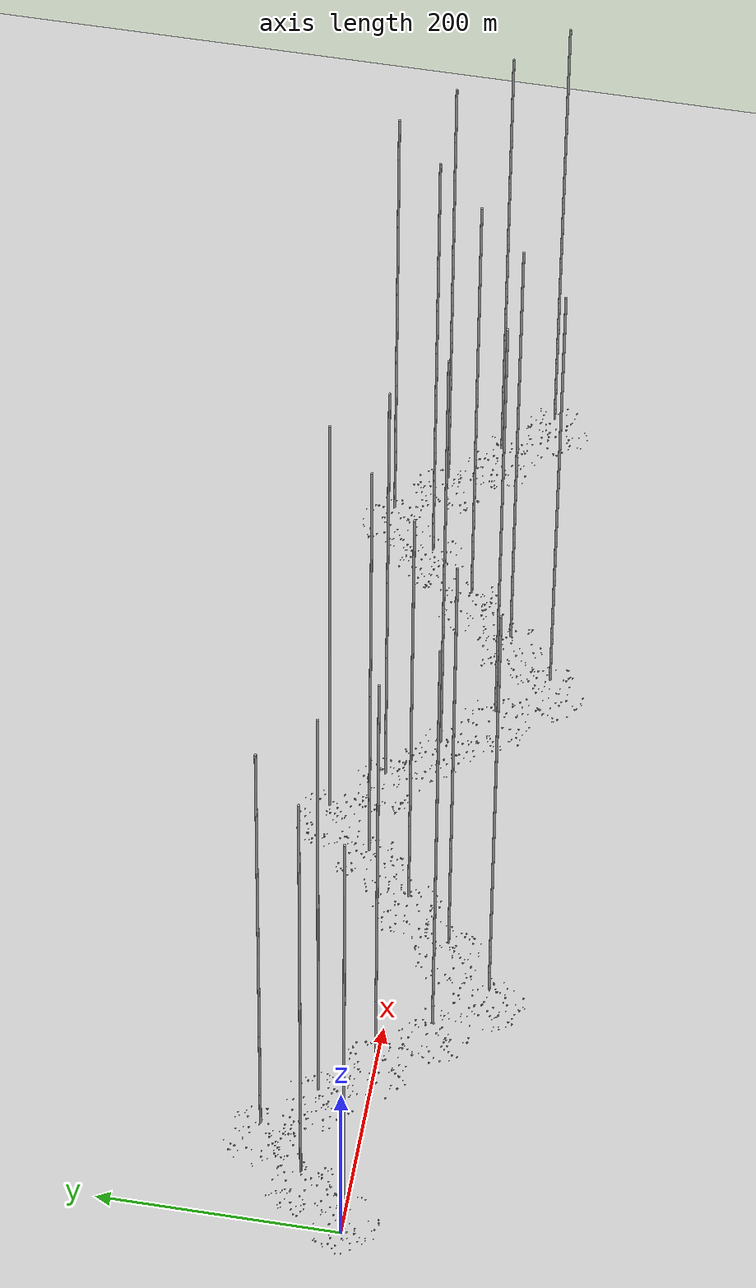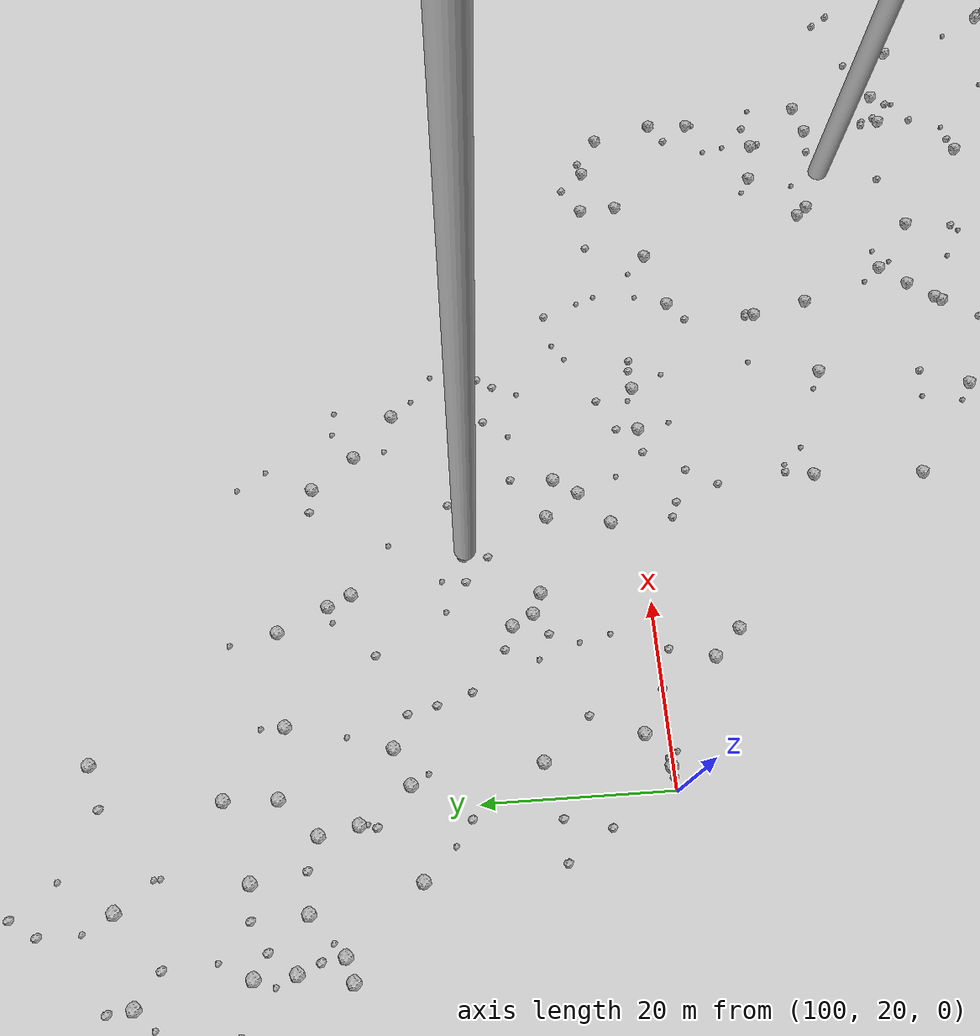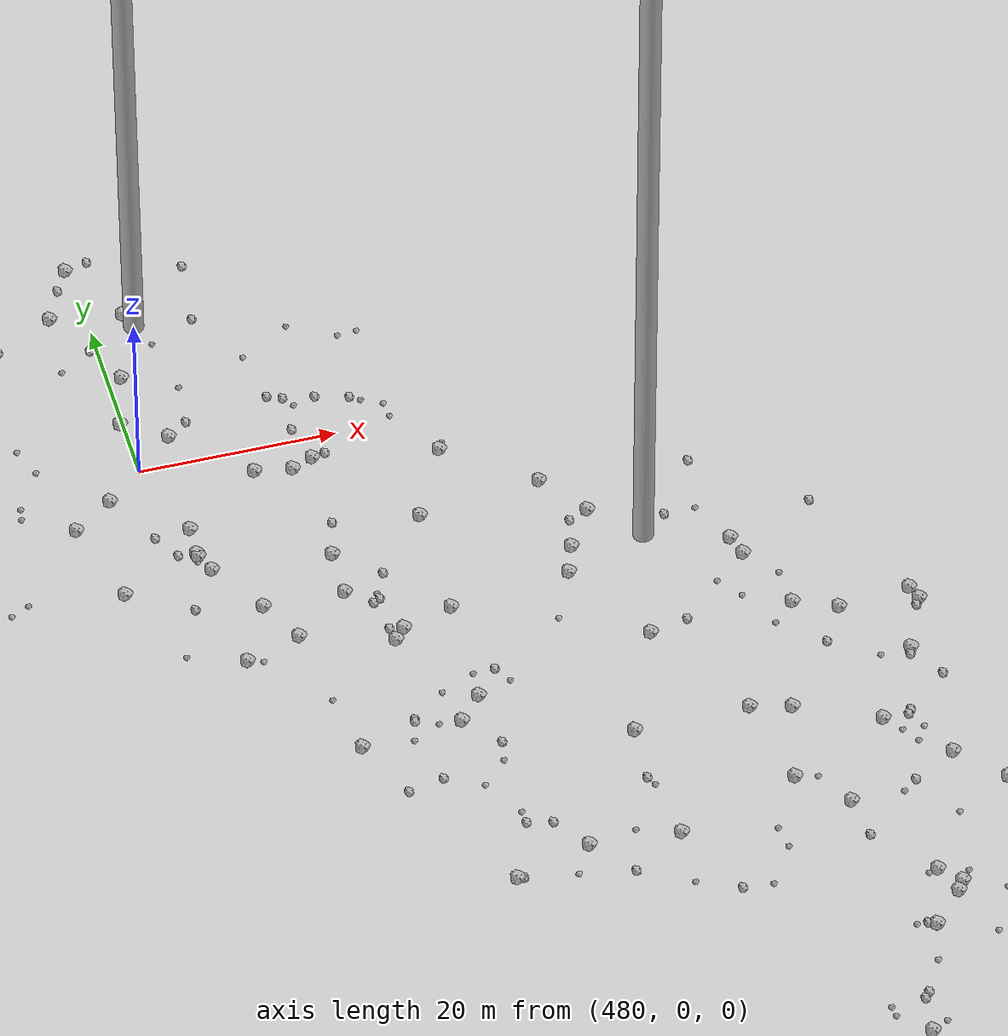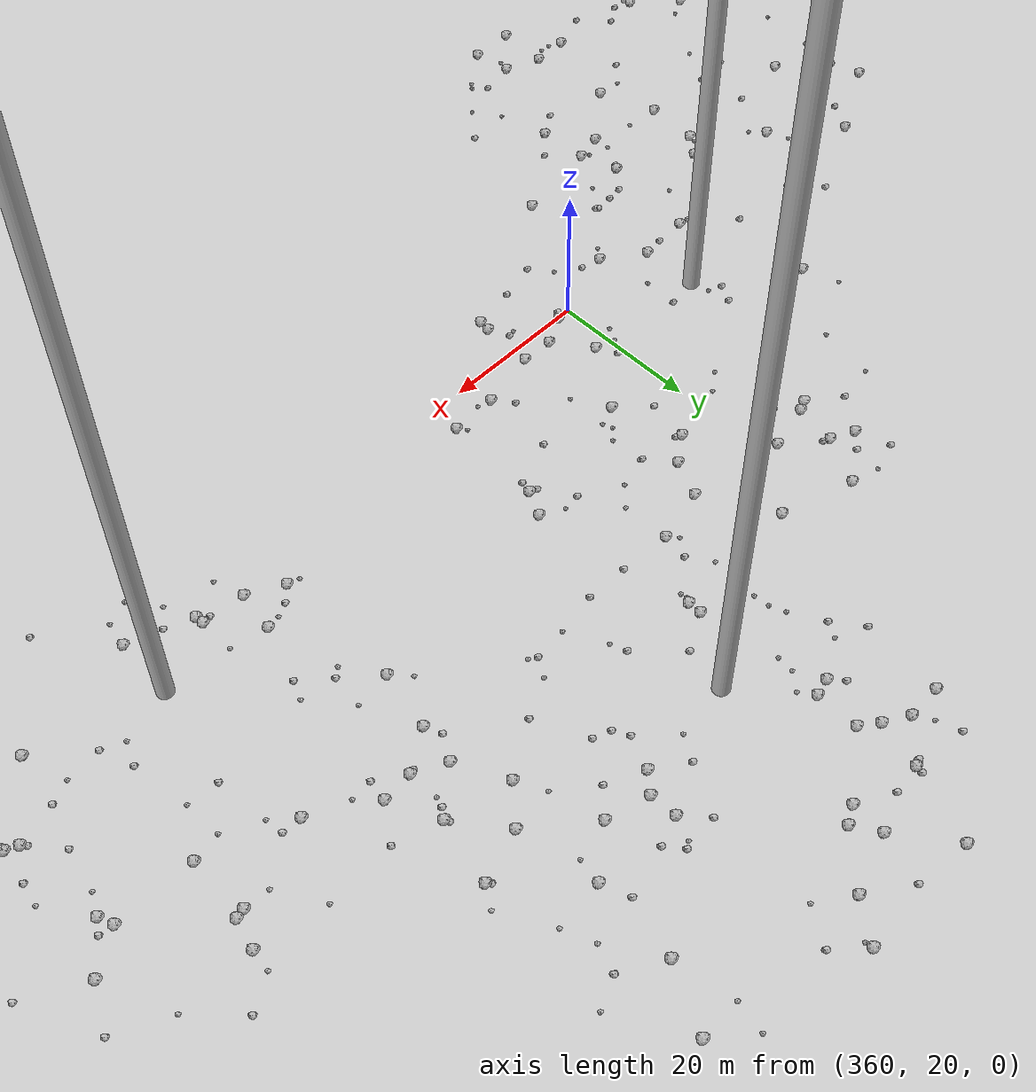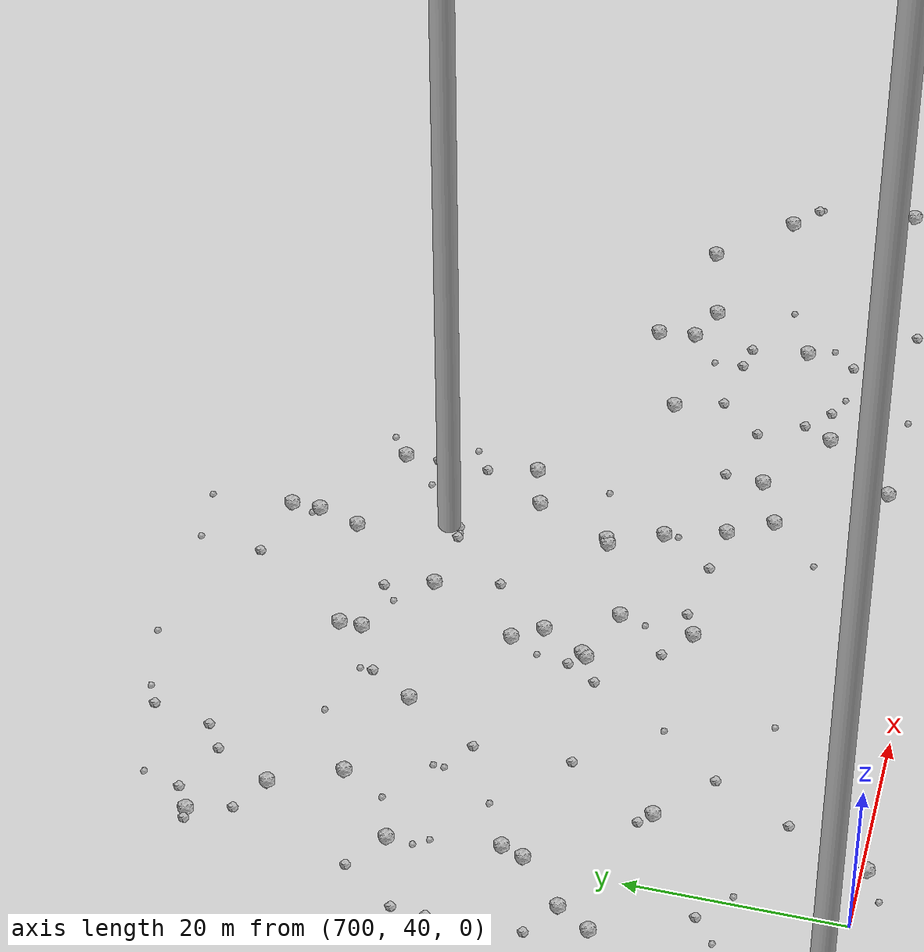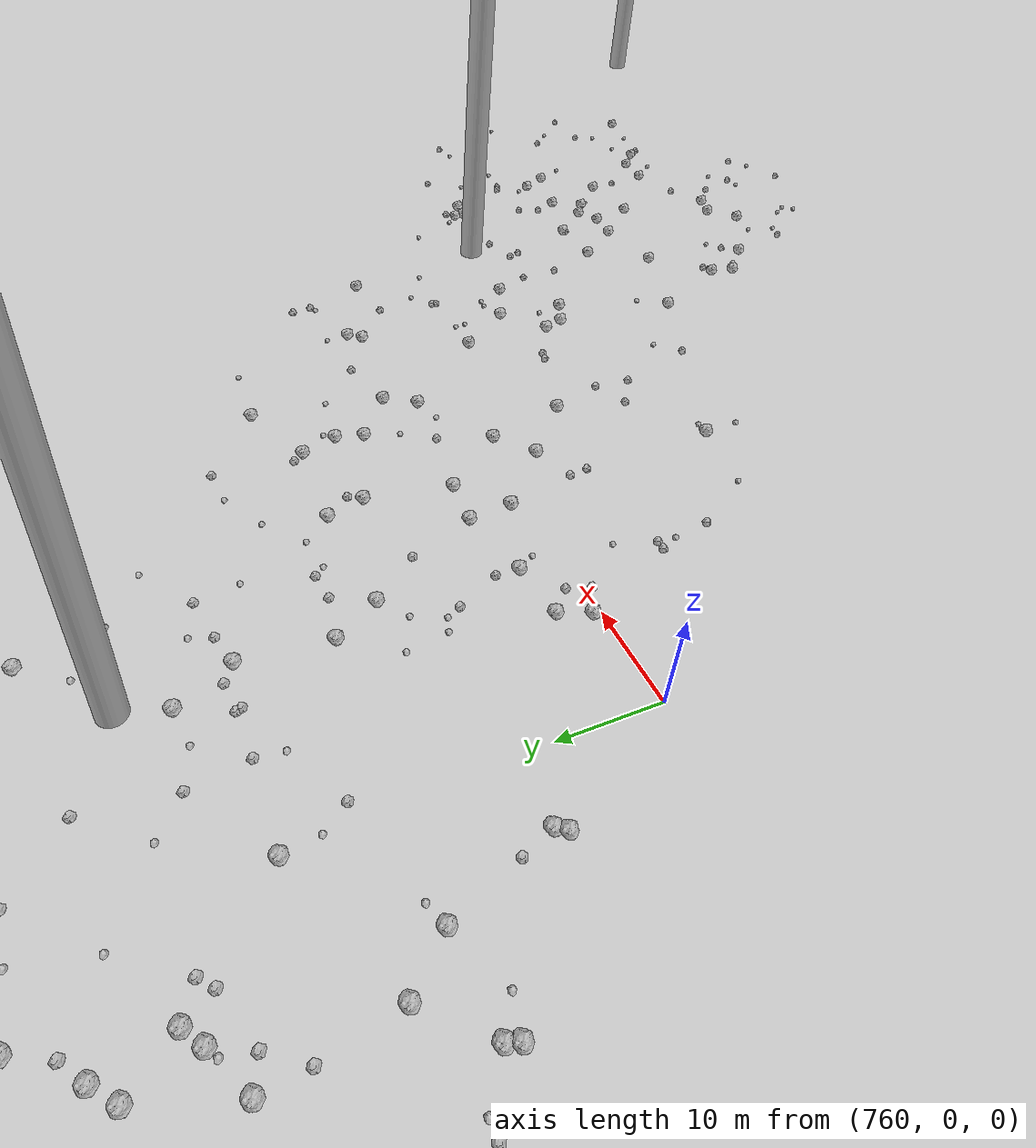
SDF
<sdf version="1.6">
 <world name="default">
  <include><uri>model://custom_ground</uri></include>
  <include><uri>model://sun</uri></include>
  <spherical_coordinates>
   <surface_model>EARTH_WGS84</surface_model>
   <latitude_deg>38.161479</latitude_deg>
   <longitude_deg>-122.454630</longitude_deg>
   <elevation>488.0</elevation>
   <heading_deg>90</heading_deg>
  </spherical_coordinates>
  <model name="rock1_0_0">
   <include><uri>model://rock1</uri><pose>1.1730208413784347 -10.354745727355265 0.5 0 0 0</pose></include>
  </model>
  <model name="rock1_0_1">
   <include><uri>model://rock1</uri><pose>34.270584932607896 17.3468146963379 0.5 0 0 0</pose></include>
  </model>
  <model name="rock1_0_2">
   <include><uri>model://rock1</uri><pose>20.87830525166615 -0.18826111654771083 0.5 0 0 0</pose></include>
  </model>
  <model name="rock1_0_3">
   <include><uri>model://rock1</uri><pose>25.82977714893051 5.7306714882587 0.5 0 0 0</pose></include>
  </model>
  <model name="rock1_0_4">
   <include><uri>model://rock1</uri><pose>-1.1485062455434765 17.55596675857769 0.5 0 0 0</pose></include>
  </model>
  <model name="rock1_0_5">
   <include><uri>model://rock1</uri><pose>7.299424982305958 10.941195743640115 0.5 0 0 0</pose></include>
  </model>
  <model name="rock1_0_6">
   <include><uri>model://rock1</uri><pose>5.511067473386593 -1.3386667247726436 0.5 0 0 0</pose></include>
  </model>
  <model name="rock1_0_7">
   <include><uri>model://rock1</uri><pose>-4.800338817938361 -0.9646563374148833 0.5 0 0 0</pose></include>
  </model>
  <model name="rock1_0_8">
   <include><uri>model://rock1</uri><pose>1.7243222807089325 -3.9226094657035055 0.5 0 0 0</pose></include>
  </model>
  <model name="rock1_0_9">
   <include><uri>model://rock1</uri><pose>34.680886185822224 -13.67190027514009 0.5 0 0 0</pose></include>
  </model>
  <model name="rock1_0_10">
   <include><uri>model://rock1</uri><pose>17.42242431972999 -27.278784392804756 0.5 0 0 0</pose></include>
  </model>
  <model name="rock1_0_11">
   <include><uri>model://rock1</uri><pose>-5.826621163581546 7.85392033275366 0.5 0 0 0</pose></include>
  </model>
  <model name="rock1_0_12">
   <include><uri>model://rock1</uri><pose>36.39124130104978 11.222762520245254 0.5 0 0 0</pose></include>
  </model>
  <model name="rock1_0_13">
   <include><uri>model://rock1</uri><pose>7.825586587774541 -25.421972024456828 0.5 0 0 0</pose></include>
  </model>
  <model name="rock1_0_14">
   <include><uri>model://rock1</uri><pose>5.949339331311123 1.1539089222396441 0.5 0 0 0</pose></include>
  </model>
  <model name="rock1_0_15">
   <include><uri>model://rock1</uri><pose>4.431223672499311 0.4549090389089443 0.5 0 0 0</pose></include>
  </model>
  <model name="rock1_0_16">
   <include><uri>model://rock1</uri><pose>35.383288256690655 9.561968902626447 0.5 0 0 0</pose></include>
  </model>
  <model name="rock1_0_17">
   <include><uri>model://rock1</uri><pose>-12.220715956015605 2.9491262359322192 0.5 0 0 0</pose></include>
  </model>
  <model name="rock1_0_18">
   <include><uri>model://rock1</uri><pose>6.3384650209659235 -9.866147921435978 0.5 0 0 0</pose></include>
  </model>
  <model name="rock1_0_19">
   <include><uri>model://rock1</uri><pose>37.648271652145546 4.981853561375409 0.5 0 0 0</pose></include>
  </model>
  <model name="rock1_0_20">
   <include><uri>model://rock1</uri><pose>-11.007802012437653 19.005656532065416 0.5 0 0 0</pose></include>
  </model>
  <model name="rock1_0_21">
   <include><uri>model://rock1</uri><pose>14.551939133200555 -27.696418850285983 0.5 0 0 0</pose></include>
  </model>
  <model name="rock1_0_22">
   <include><uri>model://rock1</uri><pose>15.952758464865077 9.112043096362868 0.5 0 0 0</pose></include>
  </model>
  <model name="rock1_0_23">
   <include><uri>model://rock1</uri><pose>26.2197707374182 -1.311607423223176 0.5 0 0 0</pose></include>
  </model>
  <model name="rock1_0_24">
   <include><uri>model://rock1</uri><pose>14.03743075063013 0.28559652823315673 0.5 0 0 0</pose></include>
  </model>
  <model name="rock1_0_25">
   <include><uri>model://rock1</uri><pose>17.15347526345971 0.9295901771451369 0.5 0 0 0</pose></include>
  </model>
  <model name="rock1_0_26">
   <include><uri>model://rock1</uri><pose>-11.312378059702962 8.898292964293816 0.5 0 0 0</pose></include>
  </model>
  <model name="rock2_0_0">
   <include><uri>model://rock2</uri><pose>-5.317751722900205 -14.028546995436779 0.3 0 0 0</pose></include>
  </model>
  <model name="rock2_0_1">
   <include><uri>model://rock2</uri><pose>6.811108051944736 -23.604997085503655 0.3 0 0 0</pose></include>
  </model>
  <model name="rock2_0_2">
   <include><uri>model://rock2</uri><pose>-10.038061058570204 21.280087525120173 0.3 0 0 0</pose></include>
  </model>
  <model name="rock2_0_3">
   <include><uri>model://rock2</uri><pose>19.046577344032436 19.328231470909635 0.3 0 0 0</pose></include>
  </model>
  <model name="rock2_0_4">
   <include><uri>model://rock2</uri><pose>-12.193202512118555 13.893477971123922 0.3 0 0 0</pose></include>
  </model>
  <model name="rock2_0_5">
   <include><uri>model://rock2</uri><pose>-0.8862950837829011 27.64703247035967 0.3 0 0 0</pose></include>
  </model>
  <model name="rock2_0_6">
   <include><uri>model://rock2</uri><pose>1.7653986905135568 -10.911110584322717 0.3 0 0 0</pose></include>
  </model>
  <model name="rock2_0_7">
   <include><uri>model://rock2</uri><pose>17.035739397517666 18.31454553610149 0.3 0 0 0</pose></include>
  </model>
  <model name="rock2_0_8">
   <include><uri>model://rock2</uri><pose>34.63109638135072 11.803149313827738 0.3 0 0 0</pose></include>
  </model>
  <model name="rock2_0_9">
   <include><uri>model://rock2</uri><pose>-5.796391454454923 -2.239009337583859 0.3 0 0 0</pose></include>
  </model>
  <model name="rock2_0_10">
   <include><uri>model://rock2</uri><pose>39.189105294124595 -1.3732505660185303 0.3 0 0 0</pose></include>
  </model>
  <model name="rock2_0_11">
   <include><uri>model://rock2</uri><pose>14.955663652116712 19.480312146962248 0.3 0 0 0</pose></include>
  </model>
  <model name="rock2_0_12">
   <include><uri>model://rock2</uri><pose>-18.786495094872105 -2.474235368206166 0.3 0 0 0</pose></include>
  </model>
  <model name="rock2_0_13">
   <include><uri>model://rock2</uri><pose>-3.3785405658337417 -20.069483958694473 0.3 0 0 0</pose></include>
  </model>
  <model name="rock2_0_14">
   <include><uri>model://rock2</uri><pose>22.986353852086943 13.125216194875769 0.3 0 0 0</pose></include>
  </model>
  <model name="rock2_0_15">
   <include><uri>model://rock2</uri><pose>4.102013814927766 -9.941035061515748 0.3 0 0 0</pose></include>
  </model>
  <model name="rock2_0_16">
   <include><uri>model://rock2</uri><pose>17.485646800099282 15.526293159770631 0.3 0 0 0</pose></include>
  </model>
  <model name="rock2_0_17">
   <include><uri>model://rock2</uri><pose>-14.192117983213013 -9.620971780972717 0.3 0 0 0</pose></include>
  </model>
  <model name="rock2_0_18">
   <include><uri>model://rock2</uri><pose>23.094252693425915 7.926053227622731 0.3 0 0 0</pose></include>
  </model>
  <model name="rock2_0_19">
   <include><uri>model://rock2</uri><pose>24.373545892818974 25.656507455417618 0.3 0 0 0</pose></include>
  </model>
  <model name="rock2_0_20">
   <include><uri>model://rock2</uri><pose>-14.690530138739499 5.017129164130232 0.3 0 0 0</pose></include>
  </model>
  <model name="rock2_0_21">
   <include><uri>model://rock2</uri><pose>6.530839458401761 11.478333810202649 0.3 0 0 0</pose></include>
  </model>
  <model name="rock2_0_22">
   <include><uri>model://rock2</uri><pose>25.701725404995898 7.74775714177683 0.3 0 0 0</pose></include>
  </model>
  <model name="rock2_0_23">
   <include><uri>model://rock2</uri><pose>36.239036239863836 -10.470440830050368 0.3 0 0 0</pose></include>
  </model>
  <model name="rock2_0_24">
   <include><uri>model://rock2</uri><pose>-19.465989742661826 1.8530717985197178 0.3 0 0 0</pose></include>
  </model>
  <model name="rock2_0_25">
   <include><uri>model://rock2</uri><pose>-0.7693949435323582 -26.180022183311614 0.3 0 0 0</pose></include>
  </model>
  <model name="rock2_0_26">
   <include><uri>model://rock2</uri><pose>-8.075987065724197 -8.392699886481644 0.3 0 0 0</pose></include>
  </model>
  <model name="rock3_0_0">
   <include><uri>model://rock3</uri><pose>-10.640913078729909 8.658573778367483 0.2 0 0 0</pose></include>
  </model>
  <model name="rock3_0_1">
   <include><uri>model://rock3</uri><pose>-1.380441293594739 -19.80047420627591 0.2 0 0 0</pose></include>
  </model>
  <model name="rock3_0_2">
   <include><uri>model://rock3</uri><pose>-7.096697350638596 -18.136988040027262 0.2 0 0 0</pose></include>
  </model>
  <model name="rock3_0_3">
   <include><uri>model://rock3</uri><pose>23.77216217149025 -3.1583819161124147 0.2 0 0 0</pose></include>
  </model>
  <model name="rock3_0_4">
   <include><uri>model://rock3</uri><pose>12.178207172867232 -19.574037493109245 0.2 0 0 0</pose></include>
  </model>
  <model name="rock3_0_5">
   <include><uri>model://rock3</uri><pose>11.65473758816475 6.80548438018441 0.2 0 0 0</pose></include>
  </model>
  <model name="rock3_0_6">
   <include><uri>model://rock3</uri><pose>12.713563625196386 -28.260622464406516 0.2 0 0 0</pose></include>
  </model>
  <model name="rock3_0_7">
   <include><uri>model://rock3</uri><pose>14.475914998047529 -3.7067521397980947 0.2 0 0 0</pose></include>
  </model>
  <model name="rock3_0_8">
   <include><uri>model://rock3</uri><pose>38.77199134829585 4.645848899464461 0.2 0 0 0</pose></include>
  </model>
  <model name="rock3_0_9">
   <include><uri>model://rock3</uri><pose>15.563013034640171 -19.19378786175578 0.2 0 0 0</pose></include>
  </model>
  <model name="rock3_0_10">
   <include><uri>model://rock3</uri><pose>22.69872245788148 23.107924709944193 0.2 0 0 0</pose></include>
  </model>
  <model name="rock3_0_11">
   <include><uri>model://rock3</uri><pose>4.322932304029429 -7.007098101435162 0.2 0 0 0</pose></include>
  </model>
  <model name="rock3_0_12">
   <include><uri>model://rock3</uri><pose>-7.420273191091836 -4.567609741484674 0.2 0 0 0</pose></include>
  </model>
  <model name="rock3_0_13">
   <include><uri>model://rock3</uri><pose>10.456262258377784 18.858081614066002 0.2 0 0 0</pose></include>
  </model>
  <model name="rock3_0_14">
   <include><uri>model://rock3</uri><pose>-3.597674637999166 -5.4706072808024615 0.2 0 0 0</pose></include>
  </model>
  <model name="rock3_0_15">
   <include><uri>model://rock3</uri><pose>1.7934652840038083 16.21127576697549 0.2 0 0 0</pose></include>
  </model>
  <model name="rock3_0_16">
   <include><uri>model://rock3</uri><pose>-3.213500969113163 9.459820340813984 0.2 0 0 0</pose></include>
  </model>
  <model name="rock3_0_17">
   <include><uri>model://rock3</uri><pose>5.540711553872782 23.724527466802527 0.2 0 0 0</pose></include>
  </model>
  <model name="rock3_0_18">
   <include><uri>model://rock3</uri><pose>18.39854203141129 4.653076263257823 0.2 0 0 0</pose></include>
  </model>
  <model name="rock3_0_19">
   <include><uri>model://rock3</uri><pose>-16.286644787604597 10.849505028250142 0.2 0 0 0</pose></include>
  </model>
  <model name="rock3_0_20">
   <include><uri>model://rock3</uri><pose>10.383695683592517 -4.712405239641889 0.2 0 0 0</pose></include>
  </model>
  <model name="rock3_0_21">
   <include><uri>model://rock3</uri><pose>35.75493721630421 -7.090724362125201 0.2 0 0 0</pose></include>
  </model>
  <model name="rock3_0_22">
   <include><uri>model://rock3</uri><pose>-1.2403253504244418 -14.733979836313836 0.2 0 0 0</pose></include>
  </model>
  <model name="rock3_0_23">
   <include><uri>model://rock3</uri><pose>22.442752567990382 -2.4308139595985025 0.2 0 0 0</pose></include>
  </model>
  <model name="rock3_0_24">
   <include><uri>model://rock3</uri><pose>-14.830568996028443 12.615795187040419 0.2 0 0 0</pose></include>
  </model>
  <model name="rock3_0_25">
   <include><uri>model://rock3</uri><pose>-7.967576960348417 20.561067007872076 0.2 0 0 0</pose></include>
  </model>
  <model name="rock3_0_26">
   <include><uri>model://rock3</uri><pose>39.41329154942969 -2.866915817271636 0.2 0 0 0</pose></include>
  </model>
  <model name="rock1_1_0">
   <include><uri>model://rock1</uri><pose>41.45844324489296 52.49686461245381 0.5 0 0 0</pose></include>
  </model>
  <model name="rock1_1_1">
   <include><uri>model://rock1</uri><pose>51.95493413373726 25.037643550511003 0.5 0 0 0</pose></include>
  </model>
  <model name="rock1_1_2">
   <include><uri>model://rock1</uri><pose>41.74589676721297 15.960343415229563 0.5 0 0 0</pose></include>
  </model>
  <model name="rock1_1_3">
   <include><uri>model://rock1</uri><pose>40.77241752338023 63.223735645013655 0.5 0 0 0</pose></include>
  </model>
  <model name="rock1_1_4">
   <include><uri>model://rock1</uri><pose>27.334269466887655 21.12882431149867 0.5 0 0 0</pose></include>
  </model>
  <model name="rock1_1_5">
   <include><uri>model://rock1</uri><pose>49.48718954404093 41.264634039670305 0.5 0 0 0</pose></include>
  </model>
  <model name="rock1_1_6">
   <include><uri>model://rock1</uri><pose>22.077573418753175 33.895659204782326 0.5 0 0 0</pose></include>
  </model>
  <model name="rock1_1_7">
   <include><uri>model://rock1</uri><pose>35.22602647288457 35.984913454484 0.5 0 0 0</pose></include>
  </model>
  <model name="rock1_1_8">
   <include><uri>model://rock1</uri><pose>14.79044024646553 35.72586096374894 0.5 0 0 0</pose></include>
  </model>
  <model name="rock1_1_9">
   <include><uri>model://rock1</uri><pose>35.52470973942884 10.925608658600378 0.5 0 0 0</pose></include>
  </model>
  <model name="rock1_1_10">
   <include><uri>model://rock1</uri><pose>39.02161742848359 18.659855264061157 0.5 0 0 0</pose></include>
  </model>
  <model name="rock1_1_11">
   <include><uri>model://rock1</uri><pose>61.40402393099986 41.0083101640388 0.5 0 0 0</pose></include>
  </model>
  <model name="rock1_1_12">
   <include><uri>model://rock1</uri><pose>53.73415856179594 60.79596356549669 0.5 0 0 0</pose></include>
  </model>
  <model name="rock1_1_13">
   <include><uri>model://rock1</uri><pose>58.47993089808641 23.194365972976417 0.5 0 0 0</pose></include>
  </model>
  <model name="rock1_1_14">
   <include><uri>model://rock1</uri><pose>49.24825513564211 54.94422311164657 0.5 0 0 0</pose></include>
  </model>
  <model name="rock1_1_15">
   <include><uri>model://rock1</uri><pose>48.97468366845355 24.089268873344274 0.5 0 0 0</pose></include>
  </model>
  <model name="rock1_1_16">
   <include><uri>model://rock1</uri><pose>32.282745005086426 47.59343909039877 0.5 0 0 0</pose></include>
  </model>
  <model name="rock1_1_17">
   <include><uri>model://rock1</uri><pose>19.76974243224137 53.210343386772735 0.5 0 0 0</pose></include>
  </model>
  <model name="rock1_1_18">
   <include><uri>model://rock1</uri><pose>55.03898656598811 58.560800733439024 0.5 0 0 0</pose></include>
  </model>
  <model name="rock1_1_19">
   <include><uri>model://rock1</uri><pose>10.062965089340942 38.329655671123774 0.5 0 0 0</pose></include>
  </model>
  <model name="rock1_1_20">
   <include><uri>model://rock1</uri><pose>44.975917865884846 36.81943919924689 0.5 0 0 0</pose></include>
  </model>
  <model name="rock1_1_21">
   <include><uri>model://rock1</uri><pose>41.332607254972814 27.153980617580952 0.5 0 0 0</pose></include>
  </model>
  <model name="rock1_1_22">
   <include><uri>model://rock1</uri><pose>28.82149556042225 39.09748532526316 0.5 0 0 0</pose></include>
  </model>
  <model name="rock1_1_23">
   <include><uri>model://rock1</uri><pose>11.028340992076762 41.21977087759019 0.5 0 0 0</pose></include>
  </model>
  <model name="rock1_1_24">
   <include><uri>model://rock1</uri><pose>47.009721411087675 32.91910016996419 0.5 0 0 0</pose></include>
  </model>
  <model name="rock1_1_25">
   <include><uri>model://rock1</uri><pose>64.71769317974281 55.43219727759171 0.5 0 0 0</pose></include>
  </model>
  <model name="rock1_1_26">
   <include><uri>model://rock1</uri><pose>21.66495723870458 45.18908331908602 0.5 0 0 0</pose></include>
  </model>
  <model name="rock2_1_0">
   <include><uri>model://rock2</uri><pose>53.29247806736955 27.890704835913994 0.3 0 0 0</pose></include>
  </model>
  <model name="rock2_1_1">
   <include><uri>model://rock2</uri><pose>54.86514786746986 38.74084262775752 0.3 0 0 0</pose></include>
  </model>
  <model name="rock2_1_2">
   <include><uri>model://rock2</uri><pose>14.696415172700474 53.75918208478942 0.3 0 0 0</pose></include>
  </model>
  <model name="rock2_1_3">
   <include><uri>model://rock2</uri><pose>41.02291280037633 31.232033585751758 0.3 0 0 0</pose></include>
  </model>
  <model name="rock2_1_4">
   <include><uri>model://rock2</uri><pose>19.177842627197293 40.08306248142986 0.3 0 0 0</pose></include>
  </model>
  <model name="rock2_1_5">
   <include><uri>model://rock2</uri><pose>54.1019355231722 16.496604621546947 0.3 0 0 0</pose></include>
  </model>
  <model name="rock2_1_6">
   <include><uri>model://rock2</uri><pose>25.113436164442398 65.9940905742404 0.3 0 0 0</pose></include>
  </model>
  <model name="rock2_1_7">
   <include><uri>model://rock2</uri><pose>34.075564437164985 47.11759060727033 0.3 0 0 0</pose></include>
  </model>
  <model name="rock2_1_8">
   <include><uri>model://rock2</uri><pose>17.263059067007198 33.811694065382326 0.3 0 0 0</pose></include>
  </model>
  <model name="rock2_1_9">
   <include><uri>model://rock2</uri><pose>48.154956196235176 24.51206085475058 0.3 0 0 0</pose></include>
  </model>
  <model name="rock2_1_10">
   <include><uri>model://rock2</uri><pose>46.467883373474656 18.470008372283857 0.3 0 0 0</pose></include>
  </model>
  <model name="rock2_1_11">
   <include><uri>model://rock2</uri><pose>33.533330526949825 51.61042505517951 0.3 0 0 0</pose></include>
  </model>
  <model name="rock2_1_12">
   <include><uri>model://rock2</uri><pose>31.989455857500737 53.64039822703641 0.3 0 0 0</pose></include>
  </model>
  <model name="rock2_1_13">
   <include><uri>model://rock2</uri><pose>31.01248576170461 58.63177318747029 0.3 0 0 0</pose></include>
  </model>
  <model name="rock2_1_14">
   <include><uri>model://rock2</uri><pose>27.837773579155566 61.6681479531219 0.3 0 0 0</pose></include>
  </model>
  <model name="rock2_1_15">
   <include><uri>model://rock2</uri><pose>16.06543937225297 43.3535922863561 0.3 0 0 0</pose></include>
  </model>
  <model name="rock2_1_16">
   <include><uri>model://rock2</uri><pose>58.94647934337664 18.55041213680347 0.3 0 0 0</pose></include>
  </model>
  <model name="rock2_1_17">
   <include><uri>model://rock2</uri><pose>64.03707071569434 57.28194137066115 0.3 0 0 0</pose></include>
  </model>
  <model name="rock2_1_18">
   <include><uri>model://rock2</uri><pose>15.227862590161983 43.49873540297446 0.3 0 0 0</pose></include>
  </model>
  <model name="rock2_1_19">
   <include><uri>model://rock2</uri><pose>52.74826032864844 27.810566769635592 0.3 0 0 0</pose></include>
  </model>
  <model name="rock2_1_20">
   <include><uri>model://rock2</uri><pose>52.00309114353825 61.394792908135756 0.3 0 0 0</pose></include>
  </model>
  <model name="rock2_1_21">
   <include><uri>model://rock2</uri><pose>28.633429265731895 14.685569589358636 0.3 0 0 0</pose></include>
  </model>
  <model name="rock2_1_22">
   <include><uri>model://rock2</uri><pose>56.26701447436049 20.30400290665459 0.3 0 0 0</pose></include>
  </model>
  <model name="rock2_1_23">
   <include><uri>model://rock2</uri><pose>56.495903623126715 20.74690487651354 0.3 0 0 0</pose></include>
  </model>
  <model name="rock2_1_24">
   <include><uri>model://rock2</uri><pose>57.13000071652622 38.567155466326966 0.3 0 0 0</pose></include>
  </model>
  <model name="rock2_1_25">
   <include><uri>model://rock2</uri><pose>68.26574075976137 47.24268146394059 0.3 0 0 0</pose></include>
  </model>
  <model name="rock2_1_26">
   <include><uri>model://rock2</uri><pose>57.584217230800995 41.862643306034236 0.3 0 0 0</pose></include>
  </model>
  <model name="rock3_1_0">
   <include><uri>model://rock3</uri><pose>45.492638524355215 59.69718878512662 0.2 0 0 0</pose></include>
  </model>
  <model name="rock3_1_1">
   <include><uri>model://rock3</uri><pose>25.351744403201636 24.26705926788999 0.2 0 0 0</pose></include>
  </model>
  <model name="rock3_1_2">
   <include><uri>model://rock3</uri><pose>30.219228687241195 49.15387624823273 0.2 0 0 0</pose></include>
  </model>
  <model name="rock3_1_3">
   <include><uri>model://rock3</uri><pose>20.340137133250455 36.050342558260056 0.2 0 0 0</pose></include>
  </model>
  <model name="rock3_1_4">
   <include><uri>model://rock3</uri><pose>27.17366112628356 16.408861470588825 0.2 0 0 0</pose></include>
  </model>
  <model name="rock3_1_5">
   <include><uri>model://rock3</uri><pose>28.53069458171464 58.101781451438924 0.2 0 0 0</pose></include>
  </model>
  <model name="rock3_1_6">
   <include><uri>model://rock3</uri><pose>48.906298423143035 39.17502668697854 0.2 0 0 0</pose></include>
  </model>
  <model name="rock3_1_7">
   <include><uri>model://rock3</uri><pose>61.017259741565084 57.82450010878973 0.2 0 0 0</pose></include>
  </model>
  <model name="rock3_1_8">
   <include><uri>model://rock3</uri><pose>36.13081417890787 24.736936944800526 0.2 0 0 0</pose></include>
  </model>
  <model name="rock3_1_9">
   <include><uri>model://rock3</uri><pose>26.09426932836274 63.20352784807696 0.2 0 0 0</pose></include>
  </model>
  <model name="rock3_1_10">
   <include><uri>model://rock3</uri><pose>39.041655822655784 45.8748073884237 0.2 0 0 0</pose></include>
  </model>
  <model name="rock3_1_11">
   <include><uri>model://rock3</uri><pose>20.410185011058978 57.39451173034897 0.2 0 0 0</pose></include>
  </model>
  <model name="rock3_1_12">
   <include><uri>model://rock3</uri><pose>64.52791881460698 48.52913204591588 0.2 0 0 0</pose></include>
  </model>
  <model name="rock3_1_13">
   <include><uri>model://rock3</uri><pose>49.963624716493854 26.90765513615247 0.2 0 0 0</pose></include>
  </model>
  <model name="rock3_1_14">
   <include><uri>model://rock3</uri><pose>50.689500491127504 48.32076784324646 0.2 0 0 0</pose></include>
  </model>
  <model name="rock3_1_15">
   <include><uri>model://rock3</uri><pose>33.96319793721172 38.46184273056494 0.2 0 0 0</pose></include>
  </model>
  <model name="rock3_1_16">
   <include><uri>model://rock3</uri><pose>39.99044125342699 66.32189298403712 0.2 0 0 0</pose></include>
  </model>
  <model name="rock3_1_17">
   <include><uri>model://rock3</uri><pose>10.374667436505842 40.775521418927184 0.2 0 0 0</pose></include>
  </model>
  <model name="rock3_1_18">
   <include><uri>model://rock3</uri><pose>16.330645348870824 52.34199041242331 0.2 0 0 0</pose></include>
  </model>
  <model name="rock3_1_19">
   <include><uri>model://rock3</uri><pose>17.997301322668214 55.0429451689104 0.2 0 0 0</pose></include>
  </model>
  <model name="rock3_1_20">
   <include><uri>model://rock3</uri><pose>43.84445296574865 17.07163065022943 0.2 0 0 0</pose></include>
  </model>
  <model name="rock3_1_21">
   <include><uri>model://rock3</uri><pose>24.424597897299467 50.59061955312208 0.2 0 0 0</pose></include>
  </model>
  <model name="rock3_1_22">
   <include><uri>model://rock3</uri><pose>25.973256354119552 35.846433060894086 0.2 0 0 0</pose></include>
  </model>
  <model name="rock3_1_23">
   <include><uri>model://rock3</uri><pose>15.004772134576251 43.79295864414948 0.2 0 0 0</pose></include>
  </model>
  <model name="rock3_1_24">
   <include><uri>model://rock3</uri><pose>12.90941797670474 30.588012022213295 0.2 0 0 0</pose></include>
  </model>
  <model name="rock3_1_25">
   <include><uri>model://rock3</uri><pose>30.142254623857 54.81118895819409 0.2 0 0 0</pose></include>
  </model>
  <model name="rock3_1_26">
   <include><uri>model://rock3</uri><pose>46.04398805344657 59.74602181458042 0.2 0 0 0</pose></include>
  </model>
  <model name="rock1_2_0">
   <include><uri>model://rock1</uri><pose>76.86698258611861 67.04266555857711 0.5 0 0 0</pose></include>
  </model>
  <model name="rock1_2_1">
   <include><uri>model://rock1</uri><pose>68.43235349685432 102.73285611446974 0.5 0 0 0</pose></include>
  </model>
  <model name="rock1_2_2">
   <include><uri>model://rock1</uri><pose>62.94398224502458 64.56666789437512 0.5 0 0 0</pose></include>
  </model>
  <model name="rock1_2_3">
   <include><uri>model://rock1</uri><pose>80.19172500079313 63.471367411947355 0.5 0 0 0</pose></include>
  </model>
  <model name="rock1_2_4">
   <include><uri>model://rock1</uri><pose>60.72693797117845 76.19956722664492 0.5 0 0 0</pose></include>
  </model>
  <model name="rock1_2_5">
   <include><uri>model://rock1</uri><pose>86.55367979920612 90.85941856146022 0.5 0 0 0</pose></include>
  </model>
  <model name="rock1_2_6">
   <include><uri>model://rock1</uri><pose>66.8860479271904 89.36168200960121 0.5 0 0 0</pose></include>
  </model>
  <model name="rock1_2_7">
   <include><uri>model://rock1</uri><pose>85.67715542670344 58.28111979800651 0.5 0 0 0</pose></include>
  </model>
  <model name="rock1_2_8">
   <include><uri>model://rock1</uri><pose>85.51076507513653 62.43220057385574 0.5 0 0 0</pose></include>
  </model>
  <model name="rock1_2_9">
   <include><uri>model://rock1</uri><pose>62.83631308899885 103.17666108644228 0.5 0 0 0</pose></include>
  </model>
  <model name="rock1_2_10">
   <include><uri>model://rock1</uri><pose>72.14030840748973 72.17893549851439 0.5 0 0 0</pose></include>
  </model>
  <model name="rock1_2_11">
   <include><uri>model://rock1</uri><pose>94.10199138594615 62.8899983750486 0.5 0 0 0</pose></include>
  </model>
  <model name="rock1_2_12">
   <include><uri>model://rock1</uri><pose>83.70472621437011 73.55655776954045 0.5 0 0 0</pose></include>
  </model>
  <model name="rock1_2_13">
   <include><uri>model://rock1</uri><pose>84.58662270650836 52.9353200106792 0.5 0 0 0</pose></include>
  </model>
  <model name="rock1_2_14">
   <include><uri>model://rock1</uri><pose>96.61242987333813 93.42295968533202 0.5 0 0 0</pose></include>
  </model>
  <model name="rock1_2_15">
   <include><uri>model://rock1</uri><pose>74.38285584081461 69.24003873715552 0.5 0 0 0</pose></include>
  </model>
  <model name="rock1_2_16">
   <include><uri>model://rock1</uri><pose>71.12807811182287 64.75236230883914 0.5 0 0 0</pose></include>
  </model>
  <model name="rock1_2_17">
   <include><uri>model://rock1</uri><pose>67.37734063758273 99.23150642468877 0.5 0 0 0</pose></include>
  </model>
  <model name="rock1_2_18">
   <include><uri>model://rock1</uri><pose>90.91194673797263 57.14392671069272 0.5 0 0 0</pose></include>
  </model>
  <model name="rock1_2_19">
   <include><uri>model://rock1</uri><pose>80.20749562701978 72.65915707783883 0.5 0 0 0</pose></include>
  </model>
  <model name="rock1_2_20">
   <include><uri>model://rock1</uri><pose>75.66878882043432 52.70509680250523 0.5 0 0 0</pose></include>
  </model>
  <model name="rock1_2_21">
   <include><uri>model://rock1</uri><pose>106.58801501268536 79.39288282579503 0.5 0 0 0</pose></include>
  </model>
  <model name="rock1_2_22">
   <include><uri>model://rock1</uri><pose>92.30661845631946 75.96075594220747 0.5 0 0 0</pose></include>
  </model>
  <model name="rock1_2_23">
   <include><uri>model://rock1</uri><pose>65.70653000153578 66.38491554894841 0.5 0 0 0</pose></include>
  </model>
  <model name="rock1_2_24">
   <include><uri>model://rock1</uri><pose>86.86948047783957 53.663516660379294 0.5 0 0 0</pose></include>
  </model>
  <model name="rock1_2_25">
   <include><uri>model://rock1</uri><pose>102.14878868573803 65.71644240559009 0.5 0 0 0</pose></include>
  </model>
  <model name="rock1_2_26">
   <include><uri>model://rock1</uri><pose>62.83853618085121 60.09336317931971 0.5 0 0 0</pose></include>
  </model>
  <model name="rock2_2_0">
   <include><uri>model://rock2</uri><pose>72.90252824866761 66.74032031166747 0.3 0 0 0</pose></include>
  </model>
  <model name="rock2_2_1">
   <include><uri>model://rock2</uri><pose>86.82242670646046 71.20515220419836 0.3 0 0 0</pose></include>
  </model>
  <model name="rock2_2_2">
   <include><uri>model://rock2</uri><pose>87.71796910259 61.10538992446052 0.3 0 0 0</pose></include>
  </model>
  <model name="rock2_2_3">
   <include><uri>model://rock2</uri><pose>83.97833102434026 101.3203586917179 0.3 0 0 0</pose></include>
  </model>
  <model name="rock2_2_4">
   <include><uri>model://rock2</uri><pose>81.639350754551 89.3623418084457 0.3 0 0 0</pose></include>
  </model>
  <model name="rock2_2_5">
   <include><uri>model://rock2</uri><pose>76.30625531719707 65.04106103822437 0.3 0 0 0</pose></include>
  </model>
  <model name="rock2_2_6">
   <include><uri>model://rock2</uri><pose>74.87848696126827 94.10054053447146 0.3 0 0 0</pose></include>
  </model>
  <model name="rock2_2_7">
   <include><uri>model://rock2</uri><pose>106.64206457020785 92.24104722975972 0.3 0 0 0</pose></include>
  </model>
  <model name="rock2_2_8">
   <include><uri>model://rock2</uri><pose>83.36512759048705 76.14936957476812 0.3 0 0 0</pose></include>
  </model>
  <model name="rock2_2_9">
   <include><uri>model://rock2</uri><pose>86.55163426890917 95.57955780682556 0.3 0 0 0</pose></include>
  </model>
  <model name="rock2_2_10">
   <include><uri>model://rock2</uri><pose>96.94783752030125 100.70771513505399 0.3 0 0 0</pose></include>
  </model>
  <model name="rock2_2_11">
   <include><uri>model://rock2</uri><pose>72.10602206187491 63.146012244338436 0.3 0 0 0</pose></include>
  </model>
  <model name="rock2_2_12">
   <include><uri>model://rock2</uri><pose>94.87080283531787 57.310410467744724 0.3 0 0 0</pose></include>
  </model>
  <model name="rock2_2_13">
   <include><uri>model://rock2</uri><pose>90.56383434822833 83.31666162862518 0.3 0 0 0</pose></include>
  </model>
  <model name="rock2_2_14">
   <include><uri>model://rock2</uri><pose>66.12805602358748 77.01624889567861 0.3 0 0 0</pose></include>
  </model>
  <model name="rock2_2_15">
   <include><uri>model://rock2</uri><pose>73.44277135363602 98.6807256702682 0.3 0 0 0</pose></include>
  </model>
  <model name="rock2_2_16">
   <include><uri>model://rock2</uri><pose>86.51871576789469 56.0470131598608 0.3 0 0 0</pose></include>
  </model>
  <model name="rock2_2_17">
   <include><uri>model://rock2</uri><pose>99.51645374230046 102.19230803378964 0.3 0 0 0</pose></include>
  </model>
  <model name="rock2_2_18">
   <include><uri>model://rock2</uri><pose>99.82395301302977 96.61226966877743 0.3 0 0 0</pose></include>
  </model>
  <model name="rock2_2_19">
   <include><uri>model://rock2</uri><pose>69.86743101303765 63.10489839375588 0.3 0 0 0</pose></include>
  </model>
  <model name="rock2_2_20">
   <include><uri>model://rock2</uri><pose>90.63746914629914 62.813527542475555 0.3 0 0 0</pose></include>
  </model>
  <model name="rock2_2_21">
   <include><uri>model://rock2</uri><pose>66.11748548257066 84.64372271007618 0.3 0 0 0</pose></include>
  </model>
  <model name="rock2_2_22">
   <include><uri>model://rock2</uri><pose>102.1458737203487 78.20799575859176 0.3 0 0 0</pose></include>
  </model>
  <model name="rock2_2_23">
   <include><uri>model://rock2</uri><pose>94.80689065610045 103.51437391972135 0.3 0 0 0</pose></include>
  </model>
  <model name="rock2_2_24">
   <include><uri>model://rock2</uri><pose>92.30765465139305 86.1172834867904 0.3 0 0 0</pose></include>
  </model>
  <model name="rock2_2_25">
   <include><uri>model://rock2</uri><pose>57.28765590587825 74.5478685174675 0.3 0 0 0</pose></include>
  </model>
  <model name="rock2_2_26">
   <include><uri>model://rock2</uri><pose>52.96892044557612 82.24148681751647 0.3 0 0 0</pose></include>
  </model>
  <model name="rock3_2_0">
   <include><uri>model://rock3</uri><pose>87.09138134242417 65.82923270406614 0.2 0 0 0</pose></include>
  </model>
  <model name="rock3_2_1">
   <include><uri>model://rock3</uri><pose>84.59611081270245 60.340294713447136 0.2 0 0 0</pose></include>
  </model>
  <model name="rock3_2_2">
   <include><uri>model://rock3</uri><pose>68.40925275749521 66.9231080241376 0.2 0 0 0</pose></include>
  </model>
  <model name="rock3_2_3">
   <include><uri>model://rock3</uri><pose>96.8342495266494 102.67840484363175 0.2 0 0 0</pose></include>
  </model>
  <model name="rock3_2_4">
   <include><uri>model://rock3</uri><pose>62.829263170820695 95.74166104777252 0.2 0 0 0</pose></include>
  </model>
  <model name="rock3_2_5">
   <include><uri>model://rock3</uri><pose>90.5245885795666 78.97340684718475 0.2 0 0 0</pose></include>
  </model>
  <model name="rock3_2_6">
   <include><uri>model://rock3</uri><pose>59.52322253836017 70.78989664835181 0.2 0 0 0</pose></include>
  </model>
  <model name="rock3_2_7">
   <include><uri>model://rock3</uri><pose>81.66215354482394 71.53706581279212 0.2 0 0 0</pose></include>
  </model>
  <model name="rock3_2_8">
   <include><uri>model://rock3</uri><pose>76.36529978218502 94.2744190663498 0.2 0 0 0</pose></include>
  </model>
  <model name="rock3_2_9">
   <include><uri>model://rock3</uri><pose>82.08657526214141 97.66688263360874 0.2 0 0 0</pose></include>
  </model>
  <model name="rock3_2_10">
   <include><uri>model://rock3</uri><pose>102.43636613142172 95.7719087189241 0.2 0 0 0</pose></include>
  </model>
  <model name="rock3_2_11">
   <include><uri>model://rock3</uri><pose>67.79783982227875 100.32725043177675 0.2 0 0 0</pose></include>
  </model>
  <model name="rock3_2_12">
   <include><uri>model://rock3</uri><pose>68.9881980200421 69.74514062809888 0.2 0 0 0</pose></include>
  </model>
  <model name="rock3_2_13">
   <include><uri>model://rock3</uri><pose>62.91432196932274 101.7475665577248 0.2 0 0 0</pose></include>
  </model>
  <model name="rock3_2_14">
   <include><uri>model://rock3</uri><pose>79.88589099641374 55.536498978814215 0.2 0 0 0</pose></include>
  </model>
  <model name="rock3_2_15">
   <include><uri>model://rock3</uri><pose>70.00317004802346 63.08979998266018 0.2 0 0 0</pose></include>
  </model>
  <model name="rock3_2_16">
   <include><uri>model://rock3</uri><pose>88.0865766045807 54.788065815557474 0.2 0 0 0</pose></include>
  </model>
  <model name="rock3_2_17">
   <include><uri>model://rock3</uri><pose>56.34698982094618 78.0454152293724 0.2 0 0 0</pose></include>
  </model>
  <model name="rock3_2_18">
   <include><uri>model://rock3</uri><pose>59.44627165617132 73.22752918411311 0.2 0 0 0</pose></include>
  </model>
  <model name="rock3_2_19">
   <include><uri>model://rock3</uri><pose>95.08611397543382 71.66312670122261 0.2 0 0 0</pose></include>
  </model>
  <model name="rock3_2_20">
   <include><uri>model://rock3</uri><pose>83.1991498635463 107.04354412660223 0.2 0 0 0</pose></include>
  </model>
  <model name="rock3_2_21">
   <include><uri>model://rock3</uri><pose>95.0382432093621 72.31329428689449 0.2 0 0 0</pose></include>
  </model>
  <model name="rock3_2_22">
   <include><uri>model://rock3</uri><pose>71.17440671033258 108.6045977245708 0.2 0 0 0</pose></include>
  </model>
  <model name="rock3_2_23">
   <include><uri>model://rock3</uri><pose>95.46395879501219 81.72417652107558 0.2 0 0 0</pose></include>
  </model>
  <model name="rock3_2_24">
   <include><uri>model://rock3</uri><pose>50.532214305116696 81.43541533427026 0.2 0 0 0</pose></include>
  </model>
  <model name="rock3_2_25">
   <include><uri>model://rock3</uri><pose>64.87162230886193 63.39323820592273 0.2 0 0 0</pose></include>
  </model>
  <model name="rock3_2_26">
   <include><uri>model://rock3</uri><pose>56.57592757856865 98.02745372014303 0.2 0 0 0</pose></include>
  </model>
  <model name="rock1_3_0">
   <include><uri>model://rock1</uri><pose>122.90867334367728 52.40865868847742 0.5 0 0 0</pose></include>
  </model>
  <model name="rock1_3_1">
   <include><uri>model://rock1</uri><pose>103.75965487517216 33.18660566761565 0.5 0 0 0</pose></include>
  </model>
  <model name="rock1_3_2">
   <include><uri>model://rock1</uri><pose>113.507339987101 14.08752799498026 0.5 0 0 0</pose></include>
  </model>
  <model name="rock1_3_3">
   <include><uri>model://rock1</uri><pose>121.7137413375538 54.94280074178835 0.5 0 0 0</pose></include>
  </model>
  <model name="rock1_3_4">
   <include><uri>model://rock1</uri><pose>129.39500050222213 23.400856260670903 0.5 0 0 0</pose></include>
  </model>
  <model name="rock1_3_5">
   <include><uri>model://rock1</uri><pose>139.24562647018598 51.75667618075599 0.5 0 0 0</pose></include>
  </model>
  <model name="rock1_3_6">
   <include><uri>model://rock1</uri><pose>116.3928316452205 11.093579316935356 0.5 0 0 0</pose></include>
  </model>
  <model name="rock1_3_7">
   <include><uri>model://rock1</uri><pose>119.21836268902786 60.33956523455233 0.5 0 0 0</pose></include>
  </model>
  <model name="rock1_3_8">
   <include><uri>model://rock1</uri><pose>106.19643393966224 48.44192144042997 0.5 0 0 0</pose></include>
  </model>
  <model name="rock1_3_9">
   <include><uri>model://rock1</uri><pose>134.9497447145252 29.36276940193295 0.5 0 0 0</pose></include>
  </model>
  <model name="rock1_3_10">
   <include><uri>model://rock1</uri><pose>144.1896431444077 47.302078236149434 0.5 0 0 0</pose></include>
  </model>
  <model name="rock1_3_11">
   <include><uri>model://rock1</uri><pose>135.5749150645996 56.535170784872065 0.5 0 0 0</pose></include>
  </model>
  <model name="rock1_3_12">
   <include><uri>model://rock1</uri><pose>130.5297385637834 30.522051132493445 0.5 0 0 0</pose></include>
  </model>
  <model name="rock1_3_13">
   <include><uri>model://rock1</uri><pose>119.4752317693052 32.955650563236915 0.5 0 0 0</pose></include>
  </model>
  <model name="rock1_3_14">
   <include><uri>model://rock1</uri><pose>133.1750411516774 26.723968916022717 0.5 0 0 0</pose></include>
  </model>
  <model name="rock1_3_15">
   <include><uri>model://rock1</uri><pose>140.68975075635734 18.985846712982017 0.5 0 0 0</pose></include>
  </model>
  <model name="rock1_3_16">
   <include><uri>model://rock1</uri><pose>121.71807792291449 31.94010684266785 0.5 0 0 0</pose></include>
  </model>
  <model name="rock1_3_17">
   <include><uri>model://rock1</uri><pose>109.13244499170574 59.52799949611245 0.5 0 0 0</pose></include>
  </model>
  <model name="rock1_3_18">
   <include><uri>model://rock1</uri><pose>98.11463050511784 56.200043941296606 0.5 0 0 0</pose></include>
  </model>
  <model name="rock1_3_19">
   <include><uri>model://rock1</uri><pose>93.10802828453397 45.93653565652737 0.5 0 0 0</pose></include>
  </model>
  <model name="rock1_3_20">
   <include><uri>model://rock1</uri><pose>102.45841702999421 20.29181034150928 0.5 0 0 0</pose></include>
  </model>
  <model name="rock1_3_21">
   <include><uri>model://rock1</uri><pose>105.94544667841825 22.605455588631237 0.5 0 0 0</pose></include>
  </model>
  <model name="rock1_3_22">
   <include><uri>model://rock1</uri><pose>102.40028487500066 46.794636002165966 0.5 0 0 0</pose></include>
  </model>
  <model name="rock1_3_23">
   <include><uri>model://rock1</uri><pose>101.9100971345045 60.16399799778312 0.5 0 0 0</pose></include>
  </model>
  <model name="rock1_3_24">
   <include><uri>model://rock1</uri><pose>98.86432825155855 52.104428605568785 0.5 0 0 0</pose></include>
  </model>
  <model name="rock1_3_25">
   <include><uri>model://rock1</uri><pose>118.25715120243882 35.26703952281947 0.5 0 0 0</pose></include>
  </model>
  <model name="rock1_3_26">
   <include><uri>model://rock1</uri><pose>126.55987271382597 40.010588578102535 0.5 0 0 0</pose></include>
  </model>
  <model name="rock2_3_0">
   <include><uri>model://rock2</uri><pose>131.3705395521454 15.761407481267467 0.3 0 0 0</pose></include>
  </model>
  <model name="rock2_3_1">
   <include><uri>model://rock2</uri><pose>109.5881050938938 46.85133501168051 0.3 0 0 0</pose></include>
  </model>
  <model name="rock2_3_2">
   <include><uri>model://rock2</uri><pose>123.56074110460314 39.90124381782228 0.3 0 0 0</pose></include>
  </model>
  <model name="rock2_3_3">
   <include><uri>model://rock2</uri><pose>111.42689034384877 39.99252593324271 0.3 0 0 0</pose></include>
  </model>
  <model name="rock2_3_4">
   <include><uri>model://rock2</uri><pose>144.61738272462333 23.365534620124684 0.3 0 0 0</pose></include>
  </model>
  <model name="rock2_3_5">
   <include><uri>model://rock2</uri><pose>135.27736124386803 34.16816280774804 0.3 0 0 0</pose></include>
  </model>
  <model name="rock2_3_6">
   <include><uri>model://rock2</uri><pose>147.27287320604825 35.34702026931565 0.3 0 0 0</pose></include>
  </model>
  <model name="rock2_3_7">
   <include><uri>model://rock2</uri><pose>96.88361136995208 26.915567974088923 0.3 0 0 0</pose></include>
  </model>
  <model name="rock2_3_8">
   <include><uri>model://rock2</uri><pose>101.3534445754207 20.13361977518377 0.3 0 0 0</pose></include>
  </model>
  <model name="rock2_3_9">
   <include><uri>model://rock2</uri><pose>98.63903787753425 40.80566350051858 0.3 0 0 0</pose></include>
  </model>
  <model name="rock2_3_10">
   <include><uri>model://rock2</uri><pose>148.37234114218995 37.121287902433785 0.3 0 0 0</pose></include>
  </model>
  <model name="rock2_3_11">
   <include><uri>model://rock2</uri><pose>114.65168837591264 18.90076970241693 0.3 0 0 0</pose></include>
  </model>
  <model name="rock2_3_12">
   <include><uri>model://rock2</uri><pose>108.15567338086254 28.069472235551945 0.3 0 0 0</pose></include>
  </model>
  <model name="rock2_3_13">
   <include><uri>model://rock2</uri><pose>126.2542029160264 37.32263384060099 0.3 0 0 0</pose></include>
  </model>
  <model name="rock2_3_14">
   <include><uri>model://rock2</uri><pose>142.8139645759975 36.717731560388074 0.3 0 0 0</pose></include>
  </model>
  <model name="rock2_3_15">
   <include><uri>model://rock2</uri><pose>110.28622103124853 43.74162219347861 0.3 0 0 0</pose></include>
  </model>
  <model name="rock2_3_16">
   <include><uri>model://rock2</uri><pose>98.08132877448438 31.732055829662706 0.3 0 0 0</pose></include>
  </model>
  <model name="rock2_3_17">
   <include><uri>model://rock2</uri><pose>98.49385081379904 50.33302253284335 0.3 0 0 0</pose></include>
  </model>
  <model name="rock2_3_18">
   <include><uri>model://rock2</uri><pose>137.75726619515115 18.744511876375515 0.3 0 0 0</pose></include>
  </model>
  <model name="rock2_3_19">
   <include><uri>model://rock2</uri><pose>115.73687588302634 36.24841178303774 0.3 0 0 0</pose></include>
  </model>
  <model name="rock2_3_20">
   <include><uri>model://rock2</uri><pose>117.12212110550364 31.4348973666867 0.3 0 0 0</pose></include>
  </model>
  <model name="rock2_3_21">
   <include><uri>model://rock2</uri><pose>116.03208968947115 49.95193969459347 0.3 0 0 0</pose></include>
  </model>
  <model name="rock2_3_22">
   <include><uri>model://rock2</uri><pose>93.84487771061475 31.666713854930865 0.3 0 0 0</pose></include>
  </model>
  <model name="rock2_3_23">
   <include><uri>model://rock2</uri><pose>129.57716101201845 16.42808241157912 0.3 0 0 0</pose></include>
  </model>
  <model name="rock2_3_24">
   <include><uri>model://rock2</uri><pose>132.66436820650765 41.404889938259586 0.3 0 0 0</pose></include>
  </model>
  <model name="rock2_3_25">
   <include><uri>model://rock2</uri><pose>110.42059993644811 20.11318335214021 0.3 0 0 0</pose></include>
  </model>
  <model name="rock2_3_26">
   <include><uri>model://rock2</uri><pose>132.87015073060542 56.845971667762896 0.3 0 0 0</pose></include>
  </model>
  <model name="rock3_3_0">
   <include><uri>model://rock3</uri><pose>140.77287633718288 33.947731724477094 0.2 0 0 0</pose></include>
  </model>
  <model name="rock3_3_1">
   <include><uri>model://rock3</uri><pose>142.35666977905956 54.161098146839876 0.2 0 0 0</pose></include>
  </model>
  <model name="rock3_3_2">
   <include><uri>model://rock3</uri><pose>120.26816553826987 42.21254053237734 0.2 0 0 0</pose></include>
  </model>
  <model name="rock3_3_3">
   <include><uri>model://rock3</uri><pose>135.12241395590507 29.2596039896819 0.2 0 0 0</pose></include>
  </model>
  <model name="rock3_3_4">
   <include><uri>model://rock3</uri><pose>103.90697261149558 19.430572226378402 0.2 0 0 0</pose></include>
  </model>
  <model name="rock3_3_5">
   <include><uri>model://rock3</uri><pose>136.07826682916954 56.462740034536175 0.2 0 0 0</pose></include>
  </model>
  <model name="rock3_3_6">
   <include><uri>model://rock3</uri><pose>118.11669992741815 65.41731184884631 0.2 0 0 0</pose></include>
  </model>
  <model name="rock3_3_7">
   <include><uri>model://rock3</uri><pose>103.34630423141613 20.472982480871178 0.2 0 0 0</pose></include>
  </model>
  <model name="rock3_3_8">
   <include><uri>model://rock3</uri><pose>114.40561813005158 32.670033711869706 0.2 0 0 0</pose></include>
  </model>
  <model name="rock3_3_9">
   <include><uri>model://rock3</uri><pose>96.15401778340868 42.55979257052593 0.2 0 0 0</pose></include>
  </model>
  <model name="rock3_3_10">
   <include><uri>model://rock3</uri><pose>146.15118778084522 32.54117226328862 0.2 0 0 0</pose></include>
  </model>
  <model name="rock3_3_11">
   <include><uri>model://rock3</uri><pose>107.62303314531408 53.164480693846144 0.2 0 0 0</pose></include>
  </model>
  <model name="rock3_3_12">
   <include><uri>model://rock3</uri><pose>134.93057975934227 22.136874834433698 0.2 0 0 0</pose></include>
  </model>
  <model name="rock3_3_13">
   <include><uri>model://rock3</uri><pose>138.0787598567699 61.78299635382286 0.2 0 0 0</pose></include>
  </model>
  <model name="rock3_3_14">
   <include><uri>model://rock3</uri><pose>139.82029545364225 48.24343604279579 0.2 0 0 0</pose></include>
  </model>
  <model name="rock3_3_15">
   <include><uri>model://rock3</uri><pose>149.07078895797875 42.53854691183142 0.2 0 0 0</pose></include>
  </model>
  <model name="rock3_3_16">
   <include><uri>model://rock3</uri><pose>103.36543697292873 44.93988876310822 0.2 0 0 0</pose></include>
  </model>
  <model name="rock3_3_17">
   <include><uri>model://rock3</uri><pose>128.30302775512178 48.16729490383564 0.2 0 0 0</pose></include>
  </model>
  <model name="rock3_3_18">
   <include><uri>model://rock3</uri><pose>119.91538052957333 54.453175729476875 0.2 0 0 0</pose></include>
  </model>
  <model name="rock3_3_19">
   <include><uri>model://rock3</uri><pose>123.75882121384183 42.476731618083896 0.2 0 0 0</pose></include>
  </model>
  <model name="rock3_3_20">
   <include><uri>model://rock3</uri><pose>136.0516713386035 64.96602742457185 0.2 0 0 0</pose></include>
  </model>
  <model name="rock3_3_21">
   <include><uri>model://rock3</uri><pose>109.05607772484397 62.033188568414985 0.2 0 0 0</pose></include>
  </model>
  <model name="rock3_3_22">
   <include><uri>model://rock3</uri><pose>145.99116164891421 44.94284692593446 0.2 0 0 0</pose></include>
  </model>
  <model name="rock3_3_23">
   <include><uri>model://rock3</uri><pose>98.8447658984427 51.26297160600687 0.2 0 0 0</pose></include>
  </model>
  <model name="rock3_3_24">
   <include><uri>model://rock3</uri><pose>145.06944638538465 53.888173275710656 0.2 0 0 0</pose></include>
  </model>
  <model name="rock3_3_25">
   <include><uri>model://rock3</uri><pose>116.69460819106666 24.86795919793129 0.2 0 0 0</pose></include>
  </model>
  <model name="rock3_3_26">
   <include><uri>model://rock3</uri><pose>115.96553861707994 28.22807393103398 0.2 0 0 0</pose></include>
  </model>
  <model name="rock1_4_0">
   <include><uri>model://rock1</uri><pose>183.32810304664298 -18.104321433011492 0.5 0 0 0</pose></include>
  </model>
  <model name="rock1_4_1">
   <include><uri>model://rock1</uri><pose>133.10773710421537 -12.60245563409132 0.5 0 0 0</pose></include>
  </model>
  <model name="rock1_4_2">
   <include><uri>model://rock1</uri><pose>186.2464689613487 -7.301325389295236 0.5 0 0 0</pose></include>
  </model>
  <model name="rock1_4_3">
   <include><uri>model://rock1</uri><pose>171.64689725641176 22.413009952242632 0.5 0 0 0</pose></include>
  </model>
  <model name="rock1_4_4">
   <include><uri>model://rock1</uri><pose>167.00148505577474 -18.20192116742143 0.5 0 0 0</pose></include>
  </model>
  <model name="rock1_4_5">
   <include><uri>model://rock1</uri><pose>155.08395413666193 3.0549888798622717 0.5 0 0 0</pose></include>
  </model>
  <model name="rock1_4_6">
   <include><uri>model://rock1</uri><pose>164.35093658210803 15.23540274397623 0.5 0 0 0</pose></include>
  </model>
  <model name="rock1_4_7">
   <include><uri>model://rock1</uri><pose>169.21905474929548 -4.850321246496943 0.5 0 0 0</pose></include>
  </model>
  <model name="rock1_4_8">
   <include><uri>model://rock1</uri><pose>182.588270760284 19.384050497185257 0.5 0 0 0</pose></include>
  </model>
  <model name="rock1_4_9">
   <include><uri>model://rock1</uri><pose>146.80754964813917 -3.292090063591708 0.5 0 0 0</pose></include>
  </model>
  <model name="rock1_4_10">
   <include><uri>model://rock1</uri><pose>180.41627406185384 -0.7043355286861903 0.5 0 0 0</pose></include>
  </model>
  <model name="rock1_4_11">
   <include><uri>model://rock1</uri><pose>171.88849447410286 18.019917380509177 0.5 0 0 0</pose></include>
  </model>
  <model name="rock1_4_12">
   <include><uri>model://rock1</uri><pose>184.34053144238862 7.2152267753786035 0.5 0 0 0</pose></include>
  </model>
  <model name="rock1_4_13">
   <include><uri>model://rock1</uri><pose>146.00642176050798 19.023878575789723 0.5 0 0 0</pose></include>
  </model>
  <model name="rock1_4_14">
   <include><uri>model://rock1</uri><pose>184.59700736479746 12.078308972455083 0.5 0 0 0</pose></include>
  </model>
  <model name="rock1_4_15">
   <include><uri>model://rock1</uri><pose>144.09350727045214 -20.698135484319483 0.5 0 0 0</pose></include>
  </model>
  <model name="rock1_4_16">
   <include><uri>model://rock1</uri><pose>156.17243784660675 -19.369085509314875 0.5 0 0 0</pose></include>
  </model>
  <model name="rock1_4_17">
   <include><uri>model://rock1</uri><pose>177.44289908200625 21.620254565218545 0.5 0 0 0</pose></include>
  </model>
  <model name="rock1_4_18">
   <include><uri>model://rock1</uri><pose>156.51774521517984 -3.432915218404524 0.5 0 0 0</pose></include>
  </model>
  <model name="rock1_4_19">
   <include><uri>model://rock1</uri><pose>182.42266044583602 -8.135136150741005 0.5 0 0 0</pose></include>
  </model>
  <model name="rock1_4_20">
   <include><uri>model://rock1</uri><pose>175.28417053724445 0.3814168161132443 0.5 0 0 0</pose></include>
  </model>
  <model name="rock1_4_21">
   <include><uri>model://rock1</uri><pose>160.7313119396242 -13.460513612546677 0.5 0 0 0</pose></include>
  </model>
  <model name="rock1_4_22">
   <include><uri>model://rock1</uri><pose>170.36536571295912 -6.167824820451759 0.5 0 0 0</pose></include>
  </model>
  <model name="rock1_4_23">
   <include><uri>model://rock1</uri><pose>155.61729167370237 -20.11167653174723 0.5 0 0 0</pose></include>
  </model>
  <model name="rock1_4_24">
   <include><uri>model://rock1</uri><pose>133.65765308649003 -0.2149136522219024 0.5 0 0 0</pose></include>
  </model>
  <model name="rock1_4_25">
   <include><uri>model://rock1</uri><pose>157.3277387240569 13.38084580555902 0.5 0 0 0</pose></include>
  </model>
  <model name="rock1_4_26">
   <include><uri>model://rock1</uri><pose>158.27116242116472 -16.425373445181528 0.5 0 0 0</pose></include>
  </model>
  <model name="rock2_4_0">
   <include><uri>model://rock2</uri><pose>155.35001922294205 3.9928033350846377 0.3 0 0 0</pose></include>
  </model>
  <model name="rock2_4_1">
   <include><uri>model://rock2</uri><pose>174.132558881422 -16.13023922726648 0.3 0 0 0</pose></include>
  </model>
  <model name="rock2_4_2">
   <include><uri>model://rock2</uri><pose>180.66773425457114 -1.6617529767789527 0.3 0 0 0</pose></include>
  </model>
  <model name="rock2_4_3">
   <include><uri>model://rock2</uri><pose>174.9374516045398 24.452750905031074 0.3 0 0 0</pose></include>
  </model>
  <model name="rock2_4_4">
   <include><uri>model://rock2</uri><pose>184.02623053925657 -17.658734936669937 0.3 0 0 0</pose></include>
  </model>
  <model name="rock2_4_5">
   <include><uri>model://rock2</uri><pose>182.9571530582814 -15.873548408330818 0.3 0 0 0</pose></include>
  </model>
  <model name="rock2_4_6">
   <include><uri>model://rock2</uri><pose>148.38290555893968 19.123266469049177 0.3 0 0 0</pose></include>
  </model>
  <model name="rock2_4_7">
   <include><uri>model://rock2</uri><pose>179.09391950085342 -7.8932600802266535 0.3 0 0 0</pose></include>
  </model>
  <model name="rock2_4_8">
   <include><uri>model://rock2</uri><pose>134.1660585934325 2.9068815484296238 0.3 0 0 0</pose></include>
  </model>
  <model name="rock2_4_9">
   <include><uri>model://rock2</uri><pose>140.84009826670413 21.44909388405302 0.3 0 0 0</pose></include>
  </model>
  <model name="rock2_4_10">
   <include><uri>model://rock2</uri><pose>183.4366169725365 -16.02845349859192 0.3 0 0 0</pose></include>
  </model>
  <model name="rock2_4_11">
   <include><uri>model://rock2</uri><pose>182.49595950785707 19.3150578806222 0.3 0 0 0</pose></include>
  </model>
  <model name="rock2_4_12">
   <include><uri>model://rock2</uri><pose>166.0576216283341 22.35122658784377 0.3 0 0 0</pose></include>
  </model>
  <model name="rock2_4_13">
   <include><uri>model://rock2</uri><pose>146.10998808005812 -15.273588873812642 0.3 0 0 0</pose></include>
  </model>
  <model name="rock2_4_14">
   <include><uri>model://rock2</uri><pose>149.05193392368167 -26.25639621899061 0.3 0 0 0</pose></include>
  </model>
  <model name="rock2_4_15">
   <include><uri>model://rock2</uri><pose>149.702963055113 18.93457489149157 0.3 0 0 0</pose></include>
  </model>
  <model name="rock2_4_16">
   <include><uri>model://rock2</uri><pose>182.0180601181525 10.46104698147657 0.3 0 0 0</pose></include>
  </model>
  <model name="rock2_4_17">
   <include><uri>model://rock2</uri><pose>133.23664658873386 10.791487576115259 0.3 0 0 0</pose></include>
  </model>
  <model name="rock2_4_18">
   <include><uri>model://rock2</uri><pose>155.00650762971887 11.463930278922419 0.3 0 0 0</pose></include>
  </model>
  <model name="rock2_4_19">
   <include><uri>model://rock2</uri><pose>154.8958430708037 4.089806871987946 0.3 0 0 0</pose></include>
  </model>
  <model name="rock2_4_20">
   <include><uri>model://rock2</uri><pose>156.43421041354082 28.429039460350793 0.3 0 0 0</pose></include>
  </model>
  <model name="rock2_4_21">
   <include><uri>model://rock2</uri><pose>184.5327588286435 12.343055705664739 0.3 0 0 0</pose></include>
  </model>
  <model name="rock2_4_22">
   <include><uri>model://rock2</uri><pose>183.38740756186948 -0.07685520122383593 0.3 0 0 0</pose></include>
  </model>
  <model name="rock2_4_23">
   <include><uri>model://rock2</uri><pose>153.11602831475943 -24.140659303725247 0.3 0 0 0</pose></include>
  </model>
  <model name="rock2_4_24">
   <include><uri>model://rock2</uri><pose>179.04912986330578 22.015135480559223 0.3 0 0 0</pose></include>
  </model>
  <model name="rock2_4_25">
   <include><uri>model://rock2</uri><pose>166.4417468218809 -23.877877191737547 0.3 0 0 0</pose></include>
  </model>
  <model name="rock2_4_26">
   <include><uri>model://rock2</uri><pose>135.2119759331495 14.186077502435737 0.3 0 0 0</pose></include>
  </model>
  <model name="rock3_4_0">
   <include><uri>model://rock3</uri><pose>152.40947561456213 27.818986824356607 0.2 0 0 0</pose></include>
  </model>
  <model name="rock3_4_1">
   <include><uri>model://rock3</uri><pose>173.86931536847754 -5.041945569858811 0.2 0 0 0</pose></include>
  </model>
  <model name="rock3_4_2">
   <include><uri>model://rock3</uri><pose>148.6457958767106 4.709683121342607 0.2 0 0 0</pose></include>
  </model>
  <model name="rock3_4_3">
   <include><uri>model://rock3</uri><pose>163.24922921901776 -13.283148548299735 0.2 0 0 0</pose></include>
  </model>
  <model name="rock3_4_4">
   <include><uri>model://rock3</uri><pose>158.90518233229798 22.121140571236843 0.2 0 0 0</pose></include>
  </model>
  <model name="rock3_4_5">
   <include><uri>model://rock3</uri><pose>147.69086070135532 15.270249831344117 0.2 0 0 0</pose></include>
  </model>
  <model name="rock3_4_6">
   <include><uri>model://rock3</uri><pose>186.31692023469896 -1.4180672281080895 0.2 0 0 0</pose></include>
  </model>
  <model name="rock3_4_7">
   <include><uri>model://rock3</uri><pose>144.58539232389023 -2.3969107726265193 0.2 0 0 0</pose></include>
  </model>
  <model name="rock3_4_8">
   <include><uri>model://rock3</uri><pose>173.23084340898694 1.4727618934004276 0.2 0 0 0</pose></include>
  </model>
  <model name="rock3_4_9">
   <include><uri>model://rock3</uri><pose>158.52095570229653 17.093391252324984 0.2 0 0 0</pose></include>
  </model>
  <model name="rock3_4_10">
   <include><uri>model://rock3</uri><pose>161.6106951869741 -15.038439671947327 0.2 0 0 0</pose></include>
  </model>
  <model name="rock3_4_11">
   <include><uri>model://rock3</uri><pose>180.56765823166592 2.8584473920297953 0.2 0 0 0</pose></include>
  </model>
  <model name="rock3_4_12">
   <include><uri>model://rock3</uri><pose>184.38443341332516 6.284671738386855 0.2 0 0 0</pose></include>
  </model>
  <model name="rock3_4_13">
   <include><uri>model://rock3</uri><pose>142.74916622982275 -14.901302094074985 0.2 0 0 0</pose></include>
  </model>
  <model name="rock3_4_14">
   <include><uri>model://rock3</uri><pose>180.0085223469436 5.471308927459759 0.2 0 0 0</pose></include>
  </model>
  <model name="rock3_4_15">
   <include><uri>model://rock3</uri><pose>177.41423714670083 21.366667411166027 0.2 0 0 0</pose></include>
  </model>
  <model name="rock3_4_16">
   <include><uri>model://rock3</uri><pose>144.45896808753167 19.619929564160763 0.2 0 0 0</pose></include>
  </model>
  <model name="rock3_4_17">
   <include><uri>model://rock3</uri><pose>141.33201240735792 15.217655553166573 0.2 0 0 0</pose></include>
  </model>
  <model name="rock3_4_18">
   <include><uri>model://rock3</uri><pose>161.9443708617928 17.451179403479365 0.2 0 0 0</pose></include>
  </model>
  <model name="rock3_4_19">
   <include><uri>model://rock3</uri><pose>158.90353760359906 -11.451678979547722 0.2 0 0 0</pose></include>
  </model>
  <model name="rock3_4_20">
   <include><uri>model://rock3</uri><pose>158.05374635139233 24.27176644180996 0.2 0 0 0</pose></include>
  </model>
  <model name="rock3_4_21">
   <include><uri>model://rock3</uri><pose>137.10866942620035 0.513580942931469 0.2 0 0 0</pose></include>
  </model>
  <model name="rock3_4_22">
   <include><uri>model://rock3</uri><pose>150.5082768867254 26.501989813847175 0.2 0 0 0</pose></include>
  </model>
  <model name="rock3_4_23">
   <include><uri>model://rock3</uri><pose>135.08847796298787 2.7868748191341552 0.2 0 0 0</pose></include>
  </model>
  <model name="rock3_4_24">
   <include><uri>model://rock3</uri><pose>161.99319062159128 -22.508734670921005 0.2 0 0 0</pose></include>
  </model>
  <model name="rock3_4_25">
   <include><uri>model://rock3</uri><pose>141.93740359845367 -19.49642029444835 0.2 0 0 0</pose></include>
  </model>
  <model name="rock3_4_26">
   <include><uri>model://rock3</uri><pose>165.68101718127258 -24.745934290370663 0.2 0 0 0</pose></include>
  </model>
  <model name="rock1_5_0">
   <include><uri>model://rock1</uri><pose>212.5064515911979 -24.29771337686082 0.5 0 0 0</pose></include>
  </model>
  <model name="rock1_5_1">
   <include><uri>model://rock1</uri><pose>195.24568402218208 -50.04916860245237 0.5 0 0 0</pose></include>
  </model>
  <model name="rock1_5_2">
   <include><uri>model://rock1</uri><pose>208.27971595630666 -24.985203017441528 0.5 0 0 0</pose></include>
  </model>
  <model name="rock1_5_3">
   <include><uri>model://rock1</uri><pose>191.71772814835893 -53.927348964163556 0.5 0 0 0</pose></include>
  </model>
  <model name="rock1_5_4">
   <include><uri>model://rock1</uri><pose>209.37367113664428 -32.95715426084976 0.5 0 0 0</pose></include>
  </model>
  <model name="rock1_5_5">
   <include><uri>model://rock1</uri><pose>190.54640304916387 -49.144069194666315 0.5 0 0 0</pose></include>
  </model>
  <model name="rock1_5_6">
   <include><uri>model://rock1</uri><pose>182.56607607145807 -63.571537427397146 0.5 0 0 0</pose></include>
  </model>
  <model name="rock1_5_7">
   <include><uri>model://rock1</uri><pose>198.1668745057166 -69.15755239731594 0.5 0 0 0</pose></include>
  </model>
  <model name="rock1_5_8">
   <include><uri>model://rock1</uri><pose>209.15894066215552 -46.73501745036014 0.5 0 0 0</pose></include>
  </model>
  <model name="rock1_5_9">
   <include><uri>model://rock1</uri><pose>200.41592507615135 -35.387470412096555 0.5 0 0 0</pose></include>
  </model>
  <model name="rock1_5_10">
   <include><uri>model://rock1</uri><pose>202.83943083501518 -69.67512247484629 0.5 0 0 0</pose></include>
  </model>
  <model name="rock1_5_11">
   <include><uri>model://rock1</uri><pose>184.44771535693053 -40.07762743621461 0.5 0 0 0</pose></include>
  </model>
  <model name="rock1_5_12">
   <include><uri>model://rock1</uri><pose>186.74426038841412 -55.73676974592754 0.5 0 0 0</pose></include>
  </model>
  <model name="rock1_5_13">
   <include><uri>model://rock1</uri><pose>202.80537274958536 -42.76222078171347 0.5 0 0 0</pose></include>
  </model>
  <model name="rock1_5_14">
   <include><uri>model://rock1</uri><pose>212.26554884909942 -39.24896846416924 0.5 0 0 0</pose></include>
  </model>
  <model name="rock1_5_15">
   <include><uri>model://rock1</uri><pose>187.48494498714268 -18.02282120200573 0.5 0 0 0</pose></include>
  </model>
  <model name="rock1_5_16">
   <include><uri>model://rock1</uri><pose>194.8877839584107 -21.468802520944116 0.5 0 0 0</pose></include>
  </model>
  <model name="rock1_5_17">
   <include><uri>model://rock1</uri><pose>178.1815187448465 -27.10462102625616 0.5 0 0 0</pose></include>
  </model>
  <model name="rock1_5_18">
   <include><uri>model://rock1</uri><pose>225.0310753265242 -30.08103694828197 0.5 0 0 0</pose></include>
  </model>
  <model name="rock1_5_19">
   <include><uri>model://rock1</uri><pose>212.92778178971082 -37.734397922206696 0.5 0 0 0</pose></include>
  </model>
  <model name="rock1_5_20">
   <include><uri>model://rock1</uri><pose>173.20476428705672 -42.077205064476736 0.5 0 0 0</pose></include>
  </model>
  <model name="rock1_5_21">
   <include><uri>model://rock1</uri><pose>187.99060901481695 -51.83705051644877 0.5 0 0 0</pose></include>
  </model>
  <model name="rock1_5_22">
   <include><uri>model://rock1</uri><pose>199.41425546581218 -50.93956096520329 0.5 0 0 0</pose></include>
  </model>
  <model name="rock1_5_23">
   <include><uri>model://rock1</uri><pose>211.43528503987653 -32.527135921858175 0.5 0 0 0</pose></include>
  </model>
  <model name="rock1_5_24">
   <include><uri>model://rock1</uri><pose>198.4549948950274 -54.96523505278178 0.5 0 0 0</pose></include>
  </model>
  <model name="rock1_5_25">
   <include><uri>model://rock1</uri><pose>176.53661720478925 -49.87053710653572 0.5 0 0 0</pose></include>
  </model>
  <model name="rock1_5_26">
   <include><uri>model://rock1</uri><pose>183.70307686588077 -59.2683484727381 0.5 0 0 0</pose></include>
  </model>
  <model name="rock2_5_0">
   <include><uri>model://rock2</uri><pose>193.17459082080055 -15.544591453601896 0.3 0 0 0</pose></include>
  </model>
  <model name="rock2_5_1">
   <include><uri>model://rock2</uri><pose>195.281400761433 -50.2603579261509 0.3 0 0 0</pose></include>
  </model>
  <model name="rock2_5_2">
   <include><uri>model://rock2</uri><pose>221.04442616111396 -46.745032745847745 0.3 0 0 0</pose></include>
  </model>
  <model name="rock2_5_3">
   <include><uri>model://rock2</uri><pose>178.02061911449385 -35.021402644831696 0.3 0 0 0</pose></include>
  </model>
  <model name="rock2_5_4">
   <include><uri>model://rock2</uri><pose>220.6555160563036 -46.43904126705287 0.3 0 0 0</pose></include>
  </model>
  <model name="rock2_5_5">
   <include><uri>model://rock2</uri><pose>207.55393758531199 -45.37722507980976 0.3 0 0 0</pose></include>
  </model>
  <model name="rock2_5_6">
   <include><uri>model://rock2</uri><pose>228.95778369406446 -36.75360106857245 0.3 0 0 0</pose></include>
  </model>
  <model name="rock2_5_7">
   <include><uri>model://rock2</uri><pose>196.37173510158837 -54.582265999779366 0.3 0 0 0</pose></include>
  </model>
  <model name="rock2_5_8">
   <include><uri>model://rock2</uri><pose>214.32246814140194 -30.119352140026464 0.3 0 0 0</pose></include>
  </model>
  <model name="rock2_5_9">
   <include><uri>model://rock2</uri><pose>178.0178734450928 -57.50583730715865 0.3 0 0 0</pose></include>
  </model>
  <model name="rock2_5_10">
   <include><uri>model://rock2</uri><pose>197.8571394024918 -51.88053072043772 0.3 0 0 0</pose></include>
  </model>
  <model name="rock2_5_11">
   <include><uri>model://rock2</uri><pose>200.4374388600506 -12.636253705669517 0.3 0 0 0</pose></include>
  </model>
  <model name="rock2_5_12">
   <include><uri>model://rock2</uri><pose>183.3964335589156 -22.36145172124489 0.3 0 0 0</pose></include>
  </model>
  <model name="rock2_5_13">
   <include><uri>model://rock2</uri><pose>201.27758711525186 -44.712643818959904 0.3 0 0 0</pose></include>
  </model>
  <model name="rock2_5_14">
   <include><uri>model://rock2</uri><pose>212.12400353546758 -37.36418946787116 0.3 0 0 0</pose></include>
  </model>
  <model name="rock2_5_15">
   <include><uri>model://rock2</uri><pose>179.93990720319752 -26.607652782908843 0.3 0 0 0</pose></include>
  </model>
  <model name="rock2_5_16">
   <include><uri>model://rock2</uri><pose>186.2415652170384 -19.741782218372414 0.3 0 0 0</pose></include>
  </model>
  <model name="rock2_5_17">
   <include><uri>model://rock2</uri><pose>177.46793870355717 -36.365637794621996 0.3 0 0 0</pose></include>
  </model>
  <model name="rock2_5_18">
   <include><uri>model://rock2</uri><pose>180.8551324059419 -31.955116831616827 0.3 0 0 0</pose></include>
  </model>
  <model name="rock2_5_19">
   <include><uri>model://rock2</uri><pose>206.20996673254726 -28.037535286299352 0.3 0 0 0</pose></include>
  </model>
  <model name="rock2_5_20">
   <include><uri>model://rock2</uri><pose>203.25294426145024 -52.639007783144606 0.3 0 0 0</pose></include>
  </model>
  <model name="rock2_5_21">
   <include><uri>model://rock2</uri><pose>223.86048773792186 -49.0068415542012 0.3 0 0 0</pose></include>
  </model>
  <model name="rock2_5_22">
   <include><uri>model://rock2</uri><pose>178.7297684934658 -44.49970150919517 0.3 0 0 0</pose></include>
  </model>
  <model name="rock2_5_23">
   <include><uri>model://rock2</uri><pose>188.469725287135 -37.41203963258732 0.3 0 0 0</pose></include>
  </model>
  <model name="rock2_5_24">
   <include><uri>model://rock2</uri><pose>201.9926297554352 -14.79924285413523 0.3 0 0 0</pose></include>
  </model>
  <model name="rock2_5_25">
   <include><uri>model://rock2</uri><pose>225.7410291543796 -43.496848528589474 0.3 0 0 0</pose></include>
  </model>
  <model name="rock2_5_26">
   <include><uri>model://rock2</uri><pose>201.346686311802 -35.84138952849705 0.3 0 0 0</pose></include>
  </model>
  <model name="rock3_5_0">
   <include><uri>model://rock3</uri><pose>201.62037052826338 -60.14464923730616 0.2 0 0 0</pose></include>
  </model>
  <model name="rock3_5_1">
   <include><uri>model://rock3</uri><pose>218.75315778438062 -50.98110984237199 0.2 0 0 0</pose></include>
  </model>
  <model name="rock3_5_2">
   <include><uri>model://rock3</uri><pose>209.2603743312024 -52.72422345539748 0.2 0 0 0</pose></include>
  </model>
  <model name="rock3_5_3">
   <include><uri>model://rock3</uri><pose>188.81937043484717 -33.2455176955371 0.2 0 0 0</pose></include>
  </model>
  <model name="rock3_5_4">
   <include><uri>model://rock3</uri><pose>220.36449363668137 -20.84084779714381 0.2 0 0 0</pose></include>
  </model>
  <model name="rock3_5_5">
   <include><uri>model://rock3</uri><pose>180.282798273509 -53.077196866293846 0.2 0 0 0</pose></include>
  </model>
  <model name="rock3_5_6">
   <include><uri>model://rock3</uri><pose>172.74397550297834 -43.95625938075813 0.2 0 0 0</pose></include>
  </model>
  <model name="rock3_5_7">
   <include><uri>model://rock3</uri><pose>209.27125095459584 -20.081655026979064 0.2 0 0 0</pose></include>
  </model>
  <model name="rock3_5_8">
   <include><uri>model://rock3</uri><pose>223.2171173058804 -21.904517929742084 0.2 0 0 0</pose></include>
  </model>
  <model name="rock3_5_9">
   <include><uri>model://rock3</uri><pose>202.03481903915454 -36.91859979766389 0.2 0 0 0</pose></include>
  </model>
  <model name="rock3_5_10">
   <include><uri>model://rock3</uri><pose>180.74906080736017 -50.95791363260369 0.2 0 0 0</pose></include>
  </model>
  <model name="rock3_5_11">
   <include><uri>model://rock3</uri><pose>219.38656796950536 -52.2214149129286 0.2 0 0 0</pose></include>
  </model>
  <model name="rock3_5_12">
   <include><uri>model://rock3</uri><pose>217.45116665447662 -60.97474964458734 0.2 0 0 0</pose></include>
  </model>
  <model name="rock3_5_13">
   <include><uri>model://rock3</uri><pose>181.98854119044225 -26.394150935244795 0.2 0 0 0</pose></include>
  </model>
  <model name="rock3_5_14">
   <include><uri>model://rock3</uri><pose>217.03773186083347 -45.5239653056474 0.2 0 0 0</pose></include>
  </model>
  <model name="rock3_5_15">
   <include><uri>model://rock3</uri><pose>197.58430522597956 -30.34140115841837 0.2 0 0 0</pose></include>
  </model>
  <model name="rock3_5_16">
   <include><uri>model://rock3</uri><pose>220.82704690843562 -43.53468698752774 0.2 0 0 0</pose></include>
  </model>
  <model name="rock3_5_17">
   <include><uri>model://rock3</uri><pose>211.0702423621662 -37.60314602128129 0.2 0 0 0</pose></include>
  </model>
  <model name="rock3_5_18">
   <include><uri>model://rock3</uri><pose>200.55814710063422 -23.10146336714466 0.2 0 0 0</pose></include>
  </model>
  <model name="rock3_5_19">
   <include><uri>model://rock3</uri><pose>217.10810437970324 -56.30407703623939 0.2 0 0 0</pose></include>
  </model>
  <model name="rock3_5_20">
   <include><uri>model://rock3</uri><pose>198.0831255737906 -49.96028947615075 0.2 0 0 0</pose></include>
  </model>
  <model name="rock3_5_21">
   <include><uri>model://rock3</uri><pose>197.52854687365198 -65.61335570627213 0.2 0 0 0</pose></include>
  </model>
  <model name="rock3_5_22">
   <include><uri>model://rock3</uri><pose>216.35971843831803 -44.46725289472255 0.2 0 0 0</pose></include>
  </model>
  <model name="rock3_5_23">
   <include><uri>model://rock3</uri><pose>174.22637596961061 -42.42329792259718 0.2 0 0 0</pose></include>
  </model>
  <model name="rock3_5_24">
   <include><uri>model://rock3</uri><pose>186.20770347333882 -20.695176786347986 0.2 0 0 0</pose></include>
  </model>
  <model name="rock3_5_25">
   <include><uri>model://rock3</uri><pose>220.74017004785537 -26.85596309855775 0.2 0 0 0</pose></include>
  </model>
  <model name="rock3_5_26">
   <include><uri>model://rock3</uri><pose>195.5549302329369 -50.39110149930385 0.2 0 0 0</pose></include>
  </model>
  <model name="rock1_6_0">
   <include><uri>model://rock1</uri><pose>223.59056713719124 -98.96584647941029 0.5 0 0 0</pose></include>
  </model>
  <model name="rock1_6_1">
   <include><uri>model://rock1</uri><pose>254.07351630201353 -83.50391486065153 0.5 0 0 0</pose></include>
  </model>
  <model name="rock1_6_2">
   <include><uri>model://rock1</uri><pose>240.16743730575513 -95.37084975714185 0.5 0 0 0</pose></include>
  </model>
  <model name="rock1_6_3">
   <include><uri>model://rock1</uri><pose>232.12113777319453 -64.92653710922306 0.5 0 0 0</pose></include>
  </model>
  <model name="rock1_6_4">
   <include><uri>model://rock1</uri><pose>255.8035825179411 -57.50560139183574 0.5 0 0 0</pose></include>
  </model>
  <model name="rock1_6_5">
   <include><uri>model://rock1</uri><pose>228.80963159415865 -89.80353888571508 0.5 0 0 0</pose></include>
  </model>
  <model name="rock1_6_6">
   <include><uri>model://rock1</uri><pose>235.82156522928648 -84.64444658328048 0.5 0 0 0</pose></include>
  </model>
  <model name="rock1_6_7">
   <include><uri>model://rock1</uri><pose>234.76384156890705 -52.87400884922624 0.5 0 0 0</pose></include>
  </model>
  <model name="rock1_6_8">
   <include><uri>model://rock1</uri><pose>227.01071772072177 -83.3706967091654 0.5 0 0 0</pose></include>
  </model>
  <model name="rock1_6_9">
   <include><uri>model://rock1</uri><pose>243.47236483086894 -50.522034832367105 0.5 0 0 0</pose></include>
  </model>
  <model name="rock1_6_10">
   <include><uri>model://rock1</uri><pose>221.94929800559737 -102.07322514168389 0.5 0 0 0</pose></include>
  </model>
  <model name="rock1_6_11">
   <include><uri>model://rock1</uri><pose>263.01401091219077 -61.507186240260076 0.5 0 0 0</pose></include>
  </model>
  <model name="rock1_6_12">
   <include><uri>model://rock1</uri><pose>231.72859537679778 -80.13536073041695 0.5 0 0 0</pose></include>
  </model>
  <model name="rock1_6_13">
   <include><uri>model://rock1</uri><pose>242.97285414125315 -54.611177691168834 0.5 0 0 0</pose></include>
  </model>
  <model name="rock1_6_14">
   <include><uri>model://rock1</uri><pose>247.13894171388702 -92.80028757574901 0.5 0 0 0</pose></include>
  </model>
  <model name="rock1_6_15">
   <include><uri>model://rock1</uri><pose>237.01479417055202 -75.03323028367215 0.5 0 0 0</pose></include>
  </model>
  <model name="rock1_6_16">
   <include><uri>model://rock1</uri><pose>236.12821565046713 -106.15611482283693 0.5 0 0 0</pose></include>
  </model>
  <model name="rock1_6_17">
   <include><uri>model://rock1</uri><pose>226.54754545887204 -73.63392124202102 0.5 0 0 0</pose></include>
  </model>
  <model name="rock1_6_18">
   <include><uri>model://rock1</uri><pose>250.06985767201806 -54.72546135292215 0.5 0 0 0</pose></include>
  </model>
  <model name="rock1_6_19">
   <include><uri>model://rock1</uri><pose>258.6718122768916 -81.5909002627931 0.5 0 0 0</pose></include>
  </model>
  <model name="rock1_6_20">
   <include><uri>model://rock1</uri><pose>251.53797223701858 -85.25539797673885 0.5 0 0 0</pose></include>
  </model>
  <model name="rock1_6_21">
   <include><uri>model://rock1</uri><pose>239.93767223687564 -76.08664154327525 0.5 0 0 0</pose></include>
  </model>
  <model name="rock1_6_22">
   <include><uri>model://rock1</uri><pose>234.26175292380142 -69.01080225882109 0.5 0 0 0</pose></include>
  </model>
  <model name="rock1_6_23">
   <include><uri>model://rock1</uri><pose>248.82842881478652 -107.53166159353968 0.5 0 0 0</pose></include>
  </model>
  <model name="rock1_6_24">
   <include><uri>model://rock1</uri><pose>247.26705307035658 -92.69152568466163 0.5 0 0 0</pose></include>
  </model>
  <model name="rock1_6_25">
   <include><uri>model://rock1</uri><pose>251.56864068735007 -84.72788000911535 0.5 0 0 0</pose></include>
  </model>
  <model name="rock1_6_26">
   <include><uri>model://rock1</uri><pose>244.53797856358744 -65.6401699420818 0.5 0 0 0</pose></include>
  </model>
  <model name="rock2_6_0">
   <include><uri>model://rock2</uri><pose>255.12355452455282 -55.84160879041742 0.3 0 0 0</pose></include>
  </model>
  <model name="rock2_6_1">
   <include><uri>model://rock2</uri><pose>239.3482720358041 -109.78058132521132 0.3 0 0 0</pose></include>
  </model>
  <model name="rock2_6_2">
   <include><uri>model://rock2</uri><pose>261.7070618204357 -89.30062197863606 0.3 0 0 0</pose></include>
  </model>
  <model name="rock2_6_3">
   <include><uri>model://rock2</uri><pose>224.05805874516517 -85.2954064738928 0.3 0 0 0</pose></include>
  </model>
  <model name="rock2_6_4">
   <include><uri>model://rock2</uri><pose>225.04115140763642 -60.11331952139801 0.3 0 0 0</pose></include>
  </model>
  <model name="rock2_6_5">
   <include><uri>model://rock2</uri><pose>215.50810926649154 -92.68146714827034 0.3 0 0 0</pose></include>
  </model>
  <model name="rock2_6_6">
   <include><uri>model://rock2</uri><pose>256.2828507248456 -92.76536762038424 0.3 0 0 0</pose></include>
  </model>
  <model name="rock2_6_7">
   <include><uri>model://rock2</uri><pose>216.91737632144668 -87.8196372333014 0.3 0 0 0</pose></include>
  </model>
  <model name="rock2_6_8">
   <include><uri>model://rock2</uri><pose>227.27798504589197 -88.50187292449526 0.3 0 0 0</pose></include>
  </model>
  <model name="rock2_6_9">
   <include><uri>model://rock2</uri><pose>236.11673510923336 -69.36410339696087 0.3 0 0 0</pose></include>
  </model>
  <model name="rock2_6_10">
   <include><uri>model://rock2</uri><pose>227.90785539349397 -101.25639914106739 0.3 0 0 0</pose></include>
  </model>
  <model name="rock2_6_11">
   <include><uri>model://rock2</uri><pose>234.92383686342563 -51.29287957166221 0.3 0 0 0</pose></include>
  </model>
  <model name="rock2_6_12">
   <include><uri>model://rock2</uri><pose>219.00203145793066 -97.58833679657968 0.3 0 0 0</pose></include>
  </model>
  <model name="rock2_6_13">
   <include><uri>model://rock2</uri><pose>263.7930584316185 -78.48028130642962 0.3 0 0 0</pose></include>
  </model>
  <model name="rock2_6_14">
   <include><uri>model://rock2</uri><pose>250.00864525689389 -92.10150839334139 0.3 0 0 0</pose></include>
  </model>
  <model name="rock2_6_15">
   <include><uri>model://rock2</uri><pose>245.0830235139204 -77.8480477753566 0.3 0 0 0</pose></include>
  </model>
  <model name="rock2_6_16">
   <include><uri>model://rock2</uri><pose>212.86798668713658 -79.48370720871321 0.3 0 0 0</pose></include>
  </model>
  <model name="rock2_6_17">
   <include><uri>model://rock2</uri><pose>212.60494179376127 -86.9608839751799 0.3 0 0 0</pose></include>
  </model>
  <model name="rock2_6_18">
   <include><uri>model://rock2</uri><pose>251.24165477009768 -87.56591212793327 0.3 0 0 0</pose></include>
  </model>
  <model name="rock2_6_19">
   <include><uri>model://rock2</uri><pose>225.98994580416405 -86.89449538219306 0.3 0 0 0</pose></include>
  </model>
  <model name="rock2_6_20">
   <include><uri>model://rock2</uri><pose>242.0048023467279 -92.05431272728472 0.3 0 0 0</pose></include>
  </model>
  <model name="rock2_6_21">
   <include><uri>model://rock2</uri><pose>241.79817268071494 -102.18490841647197 0.3 0 0 0</pose></include>
  </model>
  <model name="rock2_6_22">
   <include><uri>model://rock2</uri><pose>214.9520742394811 -68.25475087755859 0.3 0 0 0</pose></include>
  </model>
  <model name="rock2_6_23">
   <include><uri>model://rock2</uri><pose>240.40316447631054 -108.60367965481795 0.3 0 0 0</pose></include>
  </model>
  <model name="rock2_6_24">
   <include><uri>model://rock2</uri><pose>251.14947490030383 -69.256848114579 0.3 0 0 0</pose></include>
  </model>
  <model name="rock2_6_25">
   <include><uri>model://rock2</uri><pose>227.27438481870826 -70.26193477995582 0.3 0 0 0</pose></include>
  </model>
  <model name="rock2_6_26">
   <include><uri>model://rock2</uri><pose>232.16413142362467 -102.62184329266235 0.3 0 0 0</pose></include>
  </model>
  <model name="rock3_6_0">
   <include><uri>model://rock3</uri><pose>215.122634993982 -92.20888018695996 0.2 0 0 0</pose></include>
  </model>
  <model name="rock3_6_1">
   <include><uri>model://rock3</uri><pose>262.2284977521078 -91.7524875502592 0.2 0 0 0</pose></include>
  </model>
  <model name="rock3_6_2">
   <include><uri>model://rock3</uri><pose>260.19454880115 -62.540751634174015 0.2 0 0 0</pose></include>
  </model>
  <model name="rock3_6_3">
   <include><uri>model://rock3</uri><pose>247.98767476582475 -51.13158237029651 0.2 0 0 0</pose></include>
  </model>
  <model name="rock3_6_4">
   <include><uri>model://rock3</uri><pose>260.6711676122915 -80.79381020472923 0.2 0 0 0</pose></include>
  </model>
  <model name="rock3_6_5">
   <include><uri>model://rock3</uri><pose>235.66023665016132 -75.06125419433555 0.2 0 0 0</pose></include>
  </model>
  <model name="rock3_6_6">
   <include><uri>model://rock3</uri><pose>223.86055256049062 -64.74392796095026 0.2 0 0 0</pose></include>
  </model>
  <model name="rock3_6_7">
   <include><uri>model://rock3</uri><pose>225.1412075355276 -88.13067308417561 0.2 0 0 0</pose></include>
  </model>
  <model name="rock3_6_8">
   <include><uri>model://rock3</uri><pose>254.90445092947206 -98.6049129367678 0.2 0 0 0</pose></include>
  </model>
  <model name="rock3_6_9">
   <include><uri>model://rock3</uri><pose>234.2905422203561 -95.38029632821619 0.2 0 0 0</pose></include>
  </model>
  <model name="rock3_6_10">
   <include><uri>model://rock3</uri><pose>232.42354840117025 -89.86212235033358 0.2 0 0 0</pose></include>
  </model>
  <model name="rock3_6_11">
   <include><uri>model://rock3</uri><pose>239.46434949812874 -56.32106951234909 0.2 0 0 0</pose></include>
  </model>
  <model name="rock3_6_12">
   <include><uri>model://rock3</uri><pose>237.23400301695784 -104.79607686026368 0.2 0 0 0</pose></include>
  </model>
  <model name="rock3_6_13">
   <include><uri>model://rock3</uri><pose>229.6972420367302 -54.0790818249751 0.2 0 0 0</pose></include>
  </model>
  <model name="rock3_6_14">
   <include><uri>model://rock3</uri><pose>229.38788299632878 -68.41142066010931 0.2 0 0 0</pose></include>
  </model>
  <model name="rock3_6_15">
   <include><uri>model://rock3</uri><pose>246.7265108160109 -99.8451473290113 0.2 0 0 0</pose></include>
  </model>
  <model name="rock3_6_16">
   <include><uri>model://rock3</uri><pose>249.97642946901436 -71.79816195303943 0.2 0 0 0</pose></include>
  </model>
  <model name="rock3_6_17">
   <include><uri>model://rock3</uri><pose>253.02395180663933 -90.46158729866946 0.2 0 0 0</pose></include>
  </model>
  <model name="rock3_6_18">
   <include><uri>model://rock3</uri><pose>238.56730757632607 -74.40418445705959 0.2 0 0 0</pose></include>
  </model>
  <model name="rock3_6_19">
   <include><uri>model://rock3</uri><pose>260.2531186343452 -91.59972590431383 0.2 0 0 0</pose></include>
  </model>
  <model name="rock3_6_20">
   <include><uri>model://rock3</uri><pose>255.5242197020633 -72.46254426158325 0.2 0 0 0</pose></include>
  </model>
  <model name="rock3_6_21">
   <include><uri>model://rock3</uri><pose>217.49101222137799 -91.80974070670811 0.2 0 0 0</pose></include>
  </model>
  <model name="rock3_6_22">
   <include><uri>model://rock3</uri><pose>249.9952137989 -65.63167149820006 0.2 0 0 0</pose></include>
  </model>
  <model name="rock3_6_23">
   <include><uri>model://rock3</uri><pose>251.49938152635775 -78.98361858985902 0.2 0 0 0</pose></include>
  </model>
  <model name="rock3_6_24">
   <include><uri>model://rock3</uri><pose>229.41531152882513 -88.89401719495649 0.2 0 0 0</pose></include>
  </model>
  <model name="rock3_6_25">
   <include><uri>model://rock3</uri><pose>222.48759758593945 -59.588782368523525 0.2 0 0 0</pose></include>
  </model>
  <model name="rock3_6_26">
   <include><uri>model://rock3</uri><pose>236.2987762800588 -74.38875705350968 0.2 0 0 0</pose></include>
  </model>
  <model name="rock1_7_0">
   <include><uri>model://rock1</uri><pose>269.384629233919 -16.858800014102577 0.5 0 0 0</pose></include>
  </model>
  <model name="rock1_7_1">
   <include><uri>model://rock1</uri><pose>302.2332937608226 -36.43367775501025 0.5 0 0 0</pose></include>
  </model>
  <model name="rock1_7_2">
   <include><uri>model://rock1</uri><pose>296.2381192780932 -18.67358008922144 0.5 0 0 0</pose></include>
  </model>
  <model name="rock1_7_3">
   <include><uri>model://rock1</uri><pose>309.14337597015833 -38.246418424898025 0.5 0 0 0</pose></include>
  </model>
  <model name="rock1_7_4">
   <include><uri>model://rock1</uri><pose>304.17174020074555 -51.03242706959476 0.5 0 0 0</pose></include>
  </model>
  <model name="rock1_7_5">
   <include><uri>model://rock1</uri><pose>261.26642867976426 -40.55432442607652 0.5 0 0 0</pose></include>
  </model>
  <model name="rock1_7_6">
   <include><uri>model://rock1</uri><pose>300.7184250783095 -58.45437977998412 0.5 0 0 0</pose></include>
  </model>
  <model name="rock1_7_7">
   <include><uri>model://rock1</uri><pose>299.1096018502208 -54.583344974886714 0.5 0 0 0</pose></include>
  </model>
  <model name="rock1_7_8">
   <include><uri>model://rock1</uri><pose>263.12929675819936 -29.149546806345036 0.5 0 0 0</pose></include>
  </model>
  <model name="rock1_7_9">
   <include><uri>model://rock1</uri><pose>300.8498078960463 -50.316993391925614 0.5 0 0 0</pose></include>
  </model>
  <model name="rock1_7_10">
   <include><uri>model://rock1</uri><pose>275.0502800322971 -53.088505458622606 0.5 0 0 0</pose></include>
  </model>
  <model name="rock1_7_11">
   <include><uri>model://rock1</uri><pose>268.6756507624935 -46.33680061417326 0.5 0 0 0</pose></include>
  </model>
  <model name="rock1_7_12">
   <include><uri>model://rock1</uri><pose>285.2416698467206 -43.89003478966819 0.5 0 0 0</pose></include>
  </model>
  <model name="rock1_7_13">
   <include><uri>model://rock1</uri><pose>276.1673854949834 -22.122355828150177 0.5 0 0 0</pose></include>
  </model>
  <model name="rock1_7_14">
   <include><uri>model://rock1</uri><pose>252.0322102466135 -36.79596494194653 0.5 0 0 0</pose></include>
  </model>
  <model name="rock1_7_15">
   <include><uri>model://rock1</uri><pose>272.0248554786939 -59.97084520281615 0.5 0 0 0</pose></include>
  </model>
  <model name="rock1_7_16">
   <include><uri>model://rock1</uri><pose>291.162733981359 -44.76114540025375 0.5 0 0 0</pose></include>
  </model>
  <model name="rock1_7_17">
   <include><uri>model://rock1</uri><pose>283.4679900574534 -11.459406531585607 0.5 0 0 0</pose></include>
  </model>
  <model name="rock1_7_18">
   <include><uri>model://rock1</uri><pose>279.822897835139 -50.05174260304244 0.5 0 0 0</pose></include>
  </model>
  <model name="rock1_7_19">
   <include><uri>model://rock1</uri><pose>295.50804578361215 -57.932832034988415 0.5 0 0 0</pose></include>
  </model>
  <model name="rock1_7_20">
   <include><uri>model://rock1</uri><pose>305.05565704813745 -35.94442270502455 0.5 0 0 0</pose></include>
  </model>
  <model name="rock1_7_21">
   <include><uri>model://rock1</uri><pose>258.148054303538 -44.79079916096814 0.5 0 0 0</pose></include>
  </model>
  <model name="rock1_7_22">
   <include><uri>model://rock1</uri><pose>284.80065681426566 -12.050474019619138 0.5 0 0 0</pose></include>
  </model>
  <model name="rock1_7_23">
   <include><uri>model://rock1</uri><pose>258.5244435263156 -29.54329971056832 0.5 0 0 0</pose></include>
  </model>
  <model name="rock1_7_24">
   <include><uri>model://rock1</uri><pose>288.9997273119946 -42.41660412390357 0.5 0 0 0</pose></include>
  </model>
  <model name="rock1_7_25">
   <include><uri>model://rock1</uri><pose>261.08637819980027 -30.654392470661037 0.5 0 0 0</pose></include>
  </model>
  <model name="rock1_7_26">
   <include><uri>model://rock1</uri><pose>294.477966797461 -20.835620845915663 0.5 0 0 0</pose></include>
  </model>
  <model name="rock2_7_0">
   <include><uri>model://rock2</uri><pose>283.7601738189968 -64.53899872922662 0.3 0 0 0</pose></include>
  </model>
  <model name="rock2_7_1">
   <include><uri>model://rock2</uri><pose>265.30271022979474 -20.218590981169136 0.3 0 0 0</pose></include>
  </model>
  <model name="rock2_7_2">
   <include><uri>model://rock2</uri><pose>285.54477299927555 -28.474563692702915 0.3 0 0 0</pose></include>
  </model>
  <model name="rock2_7_3">
   <include><uri>model://rock2</uri><pose>302.5093046077884 -56.38933974423547 0.3 0 0 0</pose></include>
  </model>
  <model name="rock2_7_4">
   <include><uri>model://rock2</uri><pose>278.24862085841227 -22.600537417364578 0.3 0 0 0</pose></include>
  </model>
  <model name="rock2_7_5">
   <include><uri>model://rock2</uri><pose>284.97024059873274 -57.55263208685994 0.3 0 0 0</pose></include>
  </model>
  <model name="rock2_7_6">
   <include><uri>model://rock2</uri><pose>278.78391383536774 -53.90644951528307 0.3 0 0 0</pose></include>
  </model>
  <model name="rock2_7_7">
   <include><uri>model://rock2</uri><pose>296.66873441792774 -64.56613197589623 0.3 0 0 0</pose></include>
  </model>
  <model name="rock2_7_8">
   <include><uri>model://rock2</uri><pose>292.0471923667346 -27.821009382569784 0.3 0 0 0</pose></include>
  </model>
  <model name="rock2_7_9">
   <include><uri>model://rock2</uri><pose>280.78067692328733 -43.059345409022384 0.3 0 0 0</pose></include>
  </model>
  <model name="rock2_7_10">
   <include><uri>model://rock2</uri><pose>279.09801901568756 -43.33486881808027 0.3 0 0 0</pose></include>
  </model>
  <model name="rock2_7_11">
   <include><uri>model://rock2</uri><pose>281.7797607827563 -12.137210967744267 0.3 0 0 0</pose></include>
  </model>
  <model name="rock2_7_12">
   <include><uri>model://rock2</uri><pose>269.76694850597994 -64.33440055652778 0.3 0 0 0</pose></include>
  </model>
  <model name="rock2_7_13">
   <include><uri>model://rock2</uri><pose>287.5549332395898 -33.08122691678132 0.3 0 0 0</pose></include>
  </model>
  <model name="rock2_7_14">
   <include><uri>model://rock2</uri><pose>277.8841970803971 -16.750801549426576 0.3 0 0 0</pose></include>
  </model>
  <model name="rock2_7_15">
   <include><uri>model://rock2</uri><pose>299.45265209620754 -23.05462173330927 0.3 0 0 0</pose></include>
  </model>
  <model name="rock2_7_16">
   <include><uri>model://rock2</uri><pose>284.2919179181169 -14.38392988904306 0.3 0 0 0</pose></include>
  </model>
  <model name="rock2_7_17">
   <include><uri>model://rock2</uri><pose>273.19603434099594 -60.40236408596212 0.3 0 0 0</pose></include>
  </model>
  <model name="rock2_7_18">
   <include><uri>model://rock2</uri><pose>261.29409196457254 -58.592380964396895 0.3 0 0 0</pose></include>
  </model>
  <model name="rock2_7_19">
   <include><uri>model://rock2</uri><pose>288.97918099706527 -39.75075888892181 0.3 0 0 0</pose></include>
  </model>
  <model name="rock2_7_20">
   <include><uri>model://rock2</uri><pose>304.22190888559334 -47.372374486752534 0.3 0 0 0</pose></include>
  </model>
  <model name="rock2_7_21">
   <include><uri>model://rock2</uri><pose>254.67783563739445 -47.71829535007603 0.3 0 0 0</pose></include>
  </model>
  <model name="rock2_7_22">
   <include><uri>model://rock2</uri><pose>256.4116887299415 -45.897382639613795 0.3 0 0 0</pose></include>
  </model>
  <model name="rock2_7_23">
   <include><uri>model://rock2</uri><pose>283.42356183434407 -48.48387125106389 0.3 0 0 0</pose></include>
  </model>
  <model name="rock2_7_24">
   <include><uri>model://rock2</uri><pose>279.09830604166484 -56.36440124903052 0.3 0 0 0</pose></include>
  </model>
  <model name="rock2_7_25">
   <include><uri>model://rock2</uri><pose>255.11293958406088 -25.400696402616 0.3 0 0 0</pose></include>
  </model>
  <model name="rock2_7_26">
   <include><uri>model://rock2</uri><pose>299.7901178342209 -18.6597443973629 0.3 0 0 0</pose></include>
  </model>
  <model name="rock3_7_0">
   <include><uri>model://rock3</uri><pose>300.0602604639565 -17.697755620981397 0.2 0 0 0</pose></include>
  </model>
  <model name="rock3_7_1">
   <include><uri>model://rock3</uri><pose>273.4461871121371 -62.605948323969635 0.2 0 0 0</pose></include>
  </model>
  <model name="rock3_7_2">
   <include><uri>model://rock3</uri><pose>289.97122658387576 -16.804440811589153 0.2 0 0 0</pose></include>
  </model>
  <model name="rock3_7_3">
   <include><uri>model://rock3</uri><pose>266.0852299780141 -33.474291186460654 0.2 0 0 0</pose></include>
  </model>
  <model name="rock3_7_4">
   <include><uri>model://rock3</uri><pose>290.494158229066 -64.5559412974515 0.2 0 0 0</pose></include>
  </model>
  <model name="rock3_7_5">
   <include><uri>model://rock3</uri><pose>290.69382963504506 -25.269620288254202 0.2 0 0 0</pose></include>
  </model>
  <model name="rock3_7_6">
   <include><uri>model://rock3</uri><pose>304.83010688672084 -25.145616494908168 0.2 0 0 0</pose></include>
  </model>
  <model name="rock3_7_7">
   <include><uri>model://rock3</uri><pose>286.3823098535866 -40.36710373043658 0.2 0 0 0</pose></include>
  </model>
  <model name="rock3_7_8">
   <include><uri>model://rock3</uri><pose>294.04612422359156 -49.60191232934473 0.2 0 0 0</pose></include>
  </model>
  <model name="rock3_7_9">
   <include><uri>model://rock3</uri><pose>253.61671349145968 -39.863399440082375 0.2 0 0 0</pose></include>
  </model>
  <model name="rock3_7_10">
   <include><uri>model://rock3</uri><pose>277.47818483777723 -62.82556768320494 0.2 0 0 0</pose></include>
  </model>
  <model name="rock3_7_11">
   <include><uri>model://rock3</uri><pose>268.38194461655485 -38.76308728839591 0.2 0 0 0</pose></include>
  </model>
  <model name="rock3_7_12">
   <include><uri>model://rock3</uri><pose>272.81226186867013 -60.09908458982287 0.2 0 0 0</pose></include>
  </model>
  <model name="rock3_7_13">
   <include><uri>model://rock3</uri><pose>256.2461114415916 -43.12819646218067 0.2 0 0 0</pose></include>
  </model>
  <model name="rock3_7_14">
   <include><uri>model://rock3</uri><pose>255.65703195953745 -52.110371505118074 0.2 0 0 0</pose></include>
  </model>
  <model name="rock3_7_15">
   <include><uri>model://rock3</uri><pose>300.03439519584526 -43.49669032643036 0.2 0 0 0</pose></include>
  </model>
  <model name="rock3_7_16">
   <include><uri>model://rock3</uri><pose>305.8465277928795 -39.845768627112314 0.2 0 0 0</pose></include>
  </model>
  <model name="rock3_7_17">
   <include><uri>model://rock3</uri><pose>288.51771573816256 -43.796910772587175 0.2 0 0 0</pose></include>
  </model>
  <model name="rock3_7_18">
   <include><uri>model://rock3</uri><pose>288.82982045474364 -31.786870514851053 0.2 0 0 0</pose></include>
  </model>
  <model name="rock3_7_19">
   <include><uri>model://rock3</uri><pose>309.1993010180916 -33.770827817409796 0.2 0 0 0</pose></include>
  </model>
  <model name="rock3_7_20">
   <include><uri>model://rock3</uri><pose>265.30232408822945 -15.84822450819069 0.2 0 0 0</pose></include>
  </model>
  <model name="rock3_7_21">
   <include><uri>model://rock3</uri><pose>279.36276228062377 -49.971800142469014 0.2 0 0 0</pose></include>
  </model>
  <model name="rock3_7_22">
   <include><uri>model://rock3</uri><pose>293.25491959728083 -36.23442371638875 0.2 0 0 0</pose></include>
  </model>
  <model name="rock3_7_23">
   <include><uri>model://rock3</uri><pose>289.2512002943479 -25.621578001569638 0.2 0 0 0</pose></include>
  </model>
  <model name="rock3_7_24">
   <include><uri>model://rock3</uri><pose>265.14699813081853 -56.825301325095374 0.2 0 0 0</pose></include>
  </model>
  <model name="rock3_7_25">
   <include><uri>model://rock3</uri><pose>287.2466286253776 -63.91010550791936 0.2 0 0 0</pose></include>
  </model>
  <model name="rock3_7_26">
   <include><uri>model://rock3</uri><pose>290.9520619691712 -35.48207910073706 0.2 0 0 0</pose></include>
  </model>
  <model name="rock1_8_0">
   <include><uri>model://rock1</uri><pose>326.2302410394734 11.987744233994334 0.5 0 0 0</pose></include>
  </model>
  <model name="rock1_8_1">
   <include><uri>model://rock1</uri><pose>308.2077255817972 -17.162189612128145 0.5 0 0 0</pose></include>
  </model>
  <model name="rock1_8_2">
   <include><uri>model://rock1</uri><pose>337.7290417471087 0.9332366585874894 0.5 0 0 0</pose></include>
  </model>
  <model name="rock1_8_3">
   <include><uri>model://rock1</uri><pose>302.4763927321387 -12.073885493937752 0.5 0 0 0</pose></include>
  </model>
  <model name="rock1_8_4">
   <include><uri>model://rock1</uri><pose>299.6587163275593 11.896137600228109 0.5 0 0 0</pose></include>
  </model>
  <model name="rock1_8_5">
   <include><uri>model://rock1</uri><pose>338.03799605650624 -5.968662091648621 0.5 0 0 0</pose></include>
  </model>
  <model name="rock1_8_6">
   <include><uri>model://rock1</uri><pose>308.06789002121525 -18.3411541988673 0.5 0 0 0</pose></include>
  </model>
  <model name="rock1_8_7">
   <include><uri>model://rock1</uri><pose>326.2412057764029 -6.242300990017156 0.5 0 0 0</pose></include>
  </model>
  <model name="rock1_8_8">
   <include><uri>model://rock1</uri><pose>332.8848115506942 -25.000079908221785 0.5 0 0 0</pose></include>
  </model>
  <model name="rock1_8_9">
   <include><uri>model://rock1</uri><pose>349.69263778537197 2.992007504563155 0.5 0 0 0</pose></include>
  </model>
  <model name="rock1_8_10">
   <include><uri>model://rock1</uri><pose>333.8589915863098 -0.010002028666875162 0.5 0 0 0</pose></include>
  </model>
  <model name="rock1_8_11">
   <include><uri>model://rock1</uri><pose>315.5685456425868 16.36344007969003 0.5 0 0 0</pose></include>
  </model>
  <model name="rock1_8_12">
   <include><uri>model://rock1</uri><pose>307.7043685736055 -0.8957611207747149 0.5 0 0 0</pose></include>
  </model>
  <model name="rock1_8_13">
   <include><uri>model://rock1</uri><pose>336.11554223332416 6.261255528111185 0.5 0 0 0</pose></include>
  </model>
  <model name="rock1_8_14">
   <include><uri>model://rock1</uri><pose>322.2183691112595 -18.119752132660256 0.5 0 0 0</pose></include>
  </model>
  <model name="rock1_8_15">
   <include><uri>model://rock1</uri><pose>323.912382589453 9.109258509267697 0.5 0 0 0</pose></include>
  </model>
  <model name="rock1_8_16">
   <include><uri>model://rock1</uri><pose>296.3187266573603 17.741346120035082 0.5 0 0 0</pose></include>
  </model>
  <model name="rock1_8_17">
   <include><uri>model://rock1</uri><pose>327.2086388487595 -17.890125258134905 0.5 0 0 0</pose></include>
  </model>
  <model name="rock1_8_18">
   <include><uri>model://rock1</uri><pose>294.45582839978744 -14.383110065525068 0.5 0 0 0</pose></include>
  </model>
  <model name="rock1_8_19">
   <include><uri>model://rock1</uri><pose>321.8809544603378 25.836985420568787 0.5 0 0 0</pose></include>
  </model>
  <model name="rock1_8_20">
   <include><uri>model://rock1</uri><pose>332.1026966316447 -19.718828144031583 0.5 0 0 0</pose></include>
  </model>
  <model name="rock1_8_21">
   <include><uri>model://rock1</uri><pose>323.4318961129171 1.7625810051601754 0.5 0 0 0</pose></include>
  </model>
  <model name="rock1_8_22">
   <include><uri>model://rock1</uri><pose>326.82238631873776 -25.102405862098628 0.5 0 0 0</pose></include>
  </model>
  <model name="rock1_8_23">
   <include><uri>model://rock1</uri><pose>303.2532868156393 -18.579537124645867 0.5 0 0 0</pose></include>
  </model>
  <model name="rock1_8_24">
   <include><uri>model://rock1</uri><pose>303.91812543553345 8.042459844227658 0.5 0 0 0</pose></include>
  </model>
  <model name="rock1_8_25">
   <include><uri>model://rock1</uri><pose>308.6400723491373 20.14586557998333 0.5 0 0 0</pose></include>
  </model>
  <model name="rock1_8_26">
   <include><uri>model://rock1</uri><pose>306.79328732388734 23.645766035237074 0.5 0 0 0</pose></include>
  </model>
  <model name="rock2_8_0">
   <include><uri>model://rock2</uri><pose>340.918162690507 9.5460827317996 0.3 0 0 0</pose></include>
  </model>
  <model name="rock2_8_1">
   <include><uri>model://rock2</uri><pose>292.36074524210466 -7.65072847274158 0.3 0 0 0</pose></include>
  </model>
  <model name="rock2_8_2">
   <include><uri>model://rock2</uri><pose>334.65107278095115 -8.17772706036574 0.3 0 0 0</pose></include>
  </model>
  <model name="rock2_8_3">
   <include><uri>model://rock2</uri><pose>310.5381645395134 -18.140375085425667 0.3 0 0 0</pose></include>
  </model>
  <model name="rock2_8_4">
   <include><uri>model://rock2</uri><pose>313.23628996542004 -16.340813803793292 0.3 0 0 0</pose></include>
  </model>
  <model name="rock2_8_5">
   <include><uri>model://rock2</uri><pose>296.07310899960265 7.8642752221332515 0.3 0 0 0</pose></include>
  </model>
  <model name="rock2_8_6">
   <include><uri>model://rock2</uri><pose>312.62788040594444 -28.1369469846269 0.3 0 0 0</pose></include>
  </model>
  <model name="rock2_8_7">
   <include><uri>model://rock2</uri><pose>343.70593560368224 9.539757156714373 0.3 0 0 0</pose></include>
  </model>
  <model name="rock2_8_8">
   <include><uri>model://rock2</uri><pose>312.5075663069025 9.071172935770534 0.3 0 0 0</pose></include>
  </model>
  <model name="rock2_8_9">
   <include><uri>model://rock2</uri><pose>336.79070530733117 -18.79223742935318 0.3 0 0 0</pose></include>
  </model>
  <model name="rock2_8_10">
   <include><uri>model://rock2</uri><pose>296.34639678597995 10.4105898246695 0.3 0 0 0</pose></include>
  </model>
  <model name="rock2_8_11">
   <include><uri>model://rock2</uri><pose>303.0630974706496 -17.369621378585997 0.3 0 0 0</pose></include>
  </model>
  <model name="rock2_8_12">
   <include><uri>model://rock2</uri><pose>338.73711928116904 9.260447962816528 0.3 0 0 0</pose></include>
  </model>
  <model name="rock2_8_13">
   <include><uri>model://rock2</uri><pose>297.3394397030054 13.433298897967873 0.3 0 0 0</pose></include>
  </model>
  <model name="rock2_8_14">
   <include><uri>model://rock2</uri><pose>335.5341176403523 5.5203727537549625 0.3 0 0 0</pose></include>
  </model>
  <model name="rock2_8_15">
   <include><uri>model://rock2</uri><pose>318.1225831958713 29.42526405745498 0.3 0 0 0</pose></include>
  </model>
  <model name="rock2_8_16">
   <include><uri>model://rock2</uri><pose>341.1666707304607 -2.9086925205801286 0.3 0 0 0</pose></include>
  </model>
  <model name="rock2_8_17">
   <include><uri>model://rock2</uri><pose>313.43668443403226 2.140859357169184 0.3 0 0 0</pose></include>
  </model>
  <model name="rock2_8_18">
   <include><uri>model://rock2</uri><pose>336.3542263865524 20.081764581467354 0.3 0 0 0</pose></include>
  </model>
  <model name="rock2_8_19">
   <include><uri>model://rock2</uri><pose>305.55632770617734 -3.4394015857534654 0.3 0 0 0</pose></include>
  </model>
  <model name="rock2_8_20">
   <include><uri>model://rock2</uri><pose>343.46211898765335 9.815027092705058 0.3 0 0 0</pose></include>
  </model>
  <model name="rock2_8_21">
   <include><uri>model://rock2</uri><pose>322.70901690102414 11.999467454249704 0.3 0 0 0</pose></include>
  </model>
  <model name="rock2_8_22">
   <include><uri>model://rock2</uri><pose>319.91592170917795 -8.97516510183474 0.3 0 0 0</pose></include>
  </model>
  <model name="rock2_8_23">
   <include><uri>model://rock2</uri><pose>331.2845742648703 25.04429520763074 0.3 0 0 0</pose></include>
  </model>
  <model name="rock2_8_24">
   <include><uri>model://rock2</uri><pose>316.72137319139426 -20.191192180256614 0.3 0 0 0</pose></include>
  </model>
  <model name="rock2_8_25">
   <include><uri>model://rock2</uri><pose>304.23343266381164 19.717197832581498 0.3 0 0 0</pose></include>
  </model>
  <model name="rock2_8_26">
   <include><uri>model://rock2</uri><pose>345.570295642092 -12.510248660884532 0.3 0 0 0</pose></include>
  </model>
  <model name="rock3_8_0">
   <include><uri>model://rock3</uri><pose>310.7294155624122 18.541324461264757 0.2 0 0 0</pose></include>
  </model>
  <model name="rock3_8_1">
   <include><uri>model://rock3</uri><pose>314.0706426125291 19.2128200018143 0.2 0 0 0</pose></include>
  </model>
  <model name="rock3_8_2">
   <include><uri>model://rock3</uri><pose>341.91543345810226 -16.837806910737406 0.2 0 0 0</pose></include>
  </model>
  <model name="rock3_8_3">
   <include><uri>model://rock3</uri><pose>333.5204043555766 2.1603077244691917 0.2 0 0 0</pose></include>
  </model>
  <model name="rock3_8_4">
   <include><uri>model://rock3</uri><pose>317.0303965364158 14.327409617868483 0.2 0 0 0</pose></include>
  </model>
  <model name="rock3_8_5">
   <include><uri>model://rock3</uri><pose>341.0226976086922 6.3816886873065 0.2 0 0 0</pose></include>
  </model>
  <model name="rock3_8_6">
   <include><uri>model://rock3</uri><pose>323.7740290474227 -19.166797602970263 0.2 0 0 0</pose></include>
  </model>
  <model name="rock3_8_7">
   <include><uri>model://rock3</uri><pose>333.8690075095398 14.287145650590105 0.2 0 0 0</pose></include>
  </model>
  <model name="rock3_8_8">
   <include><uri>model://rock3</uri><pose>295.7697295845579 -0.25306842609892755 0.2 0 0 0</pose></include>
  </model>
  <model name="rock3_8_9">
   <include><uri>model://rock3</uri><pose>327.91008911471147 1.2723437396605703 0.2 0 0 0</pose></include>
  </model>
  <model name="rock3_8_10">
   <include><uri>model://rock3</uri><pose>322.6112977137628 -6.190606622788813 0.2 0 0 0</pose></include>
  </model>
  <model name="rock3_8_11">
   <include><uri>model://rock3</uri><pose>297.81022593793597 -15.3636005136578 0.2 0 0 0</pose></include>
  </model>
  <model name="rock3_8_12">
   <include><uri>model://rock3</uri><pose>302.8005724946881 -4.184924106862557 0.2 0 0 0</pose></include>
  </model>
  <model name="rock3_8_13">
   <include><uri>model://rock3</uri><pose>339.5717381363942 -13.155801390857718 0.2 0 0 0</pose></include>
  </model>
  <model name="rock3_8_14">
   <include><uri>model://rock3</uri><pose>308.3853348625905 1.5868550802152797 0.2 0 0 0</pose></include>
  </model>
  <model name="rock3_8_15">
   <include><uri>model://rock3</uri><pose>296.51808022566786 7.687016138587651 0.2 0 0 0</pose></include>
  </model>
  <model name="rock3_8_16">
   <include><uri>model://rock3</uri><pose>337.7826765940886 -21.23235873869248 0.2 0 0 0</pose></include>
  </model>
  <model name="rock3_8_17">
   <include><uri>model://rock3</uri><pose>331.4755694872215 -21.537409722999627 0.2 0 0 0</pose></include>
  </model>
  <model name="rock3_8_18">
   <include><uri>model://rock3</uri><pose>336.50353806379655 1.376706604176725 0.2 0 0 0</pose></include>
  </model>
  <model name="rock3_8_19">
   <include><uri>model://rock3</uri><pose>325.2178342342753 -19.19024582060626 0.2 0 0 0</pose></include>
  </model>
  <model name="rock3_8_20">
   <include><uri>model://rock3</uri><pose>304.41102843581916 -18.299048456028626 0.2 0 0 0</pose></include>
  </model>
  <model name="rock3_8_21">
   <include><uri>model://rock3</uri><pose>334.50976421616735 20.166713378817335 0.2 0 0 0</pose></include>
  </model>
  <model name="rock3_8_22">
   <include><uri>model://rock3</uri><pose>323.905530295077 10.045014692372611 0.2 0 0 0</pose></include>
  </model>
  <model name="rock3_8_23">
   <include><uri>model://rock3</uri><pose>304.9883748322736 -10.781411416676171 0.2 0 0 0</pose></include>
  </model>
  <model name="rock3_8_24">
   <include><uri>model://rock3</uri><pose>293.67380883200667 -7.424255154683792 0.2 0 0 0</pose></include>
  </model>
  <model name="rock3_8_25">
   <include><uri>model://rock3</uri><pose>338.3866408112616 -20.47052705803464 0.2 0 0 0</pose></include>
  </model>
  <model name="rock3_8_26">
   <include><uri>model://rock3</uri><pose>310.2653065385483 -3.106701197631523 0.2 0 0 0</pose></include>
  </model>
  <model name="rock1_9_0">
   <include><uri>model://rock1</uri><pose>345.0622404731674 20.429330885935276 0.5 0 0 0</pose></include>
  </model>
  <model name="rock1_9_1">
   <include><uri>model://rock1</uri><pose>378.5836812838414 54.33050944556541 0.5 0 0 0</pose></include>
  </model>
  <model name="rock1_9_2">
   <include><uri>model://rock1</uri><pose>369.0386321779945 47.697944227060354 0.5 0 0 0</pose></include>
  </model>
  <model name="rock1_9_3">
   <include><uri>model://rock1</uri><pose>366.0364854113889 22.34678635653126 0.5 0 0 0</pose></include>
  </model>
  <model name="rock1_9_4">
   <include><uri>model://rock1</uri><pose>352.81586296675323 58.73367269558952 0.5 0 0 0</pose></include>
  </model>
  <model name="rock1_9_5">
   <include><uri>model://rock1</uri><pose>350.53735279642507 16.684426905999793 0.5 0 0 0</pose></include>
  </model>
  <model name="rock1_9_6">
   <include><uri>model://rock1</uri><pose>370.086208248329 15.07672606078301 0.5 0 0 0</pose></include>
  </model>
  <model name="rock1_9_7">
   <include><uri>model://rock1</uri><pose>369.869955715007 13.440653925630793 0.5 0 0 0</pose></include>
  </model>
  <model name="rock1_9_8">
   <include><uri>model://rock1</uri><pose>368.1855448724119 57.76658695374863 0.5 0 0 0</pose></include>
  </model>
  <model name="rock1_9_9">
   <include><uri>model://rock1</uri><pose>384.615354236186 24.202831835654393 0.5 0 0 0</pose></include>
  </model>
  <model name="rock1_9_10">
   <include><uri>model://rock1</uri><pose>370.3458583877236 22.17953032430664 0.5 0 0 0</pose></include>
  </model>
  <model name="rock1_9_11">
   <include><uri>model://rock1</uri><pose>365.423372520294 45.09202738483005 0.5 0 0 0</pose></include>
  </model>
  <model name="rock1_9_12">
   <include><uri>model://rock1</uri><pose>337.9604046424256 19.8711265861457 0.5 0 0 0</pose></include>
  </model>
  <model name="rock1_9_13">
   <include><uri>model://rock1</uri><pose>378.3021236198191 23.961153374014856 0.5 0 0 0</pose></include>
  </model>
  <model name="rock1_9_14">
   <include><uri>model://rock1</uri><pose>366.02465317407797 62.02378542837871 0.5 0 0 0</pose></include>
  </model>
  <model name="rock1_9_15">
   <include><uri>model://rock1</uri><pose>351.8086932320108 53.0697809694476 0.5 0 0 0</pose></include>
  </model>
  <model name="rock1_9_16">
   <include><uri>model://rock1</uri><pose>332.69755504209235 37.35362461813409 0.5 0 0 0</pose></include>
  </model>
  <model name="rock1_9_17">
   <include><uri>model://rock1</uri><pose>358.0858367899356 54.56750110551913 0.5 0 0 0</pose></include>
  </model>
  <model name="rock1_9_18">
   <include><uri>model://rock1</uri><pose>371.32351448285544 52.50823539172509 0.5 0 0 0</pose></include>
  </model>
  <model name="rock1_9_19">
   <include><uri>model://rock1</uri><pose>349.68432790648563 60.19577011580133 0.5 0 0 0</pose></include>
  </model>
  <model name="rock1_9_20">
   <include><uri>model://rock1</uri><pose>362.4604991079103 27.335141946713147 0.5 0 0 0</pose></include>
  </model>
  <model name="rock1_9_21">
   <include><uri>model://rock1</uri><pose>356.1515600571265 64.98705665327626 0.5 0 0 0</pose></include>
  </model>
  <model name="rock1_9_22">
   <include><uri>model://rock1</uri><pose>385.29454210768 37.76219680790601 0.5 0 0 0</pose></include>
  </model>
  <model name="rock1_9_23">
   <include><uri>model://rock1</uri><pose>386.99376346027844 41.14876946274316 0.5 0 0 0</pose></include>
  </model>
  <model name="rock1_9_24">
   <include><uri>model://rock1</uri><pose>350.38906311206597 52.438765854316586 0.5 0 0 0</pose></include>
  </model>
  <model name="rock1_9_25">
   <include><uri>model://rock1</uri><pose>362.1274029945291 20.299220649371712 0.5 0 0 0</pose></include>
  </model>
  <model name="rock1_9_26">
   <include><uri>model://rock1</uri><pose>368.3623610174018 35.71966286003083 0.5 0 0 0</pose></include>
  </model>
  <model name="rock2_9_0">
   <include><uri>model://rock2</uri><pose>351.66838953842387 62.189345529514014 0.3 0 0 0</pose></include>
  </model>
  <model name="rock2_9_1">
   <include><uri>model://rock2</uri><pose>368.69961023016697 17.76755460245807 0.3 0 0 0</pose></include>
  </model>
  <model name="rock2_9_2">
   <include><uri>model://rock2</uri><pose>385.52163466532346 53.94987800034417 0.3 0 0 0</pose></include>
  </model>
  <model name="rock2_9_3">
   <include><uri>model://rock2</uri><pose>384.79067791584856 36.13348339660486 0.3 0 0 0</pose></include>
  </model>
  <model name="rock2_9_4">
   <include><uri>model://rock2</uri><pose>336.49964839172407 38.53942032333007 0.3 0 0 0</pose></include>
  </model>
  <model name="rock2_9_5">
   <include><uri>model://rock2</uri><pose>342.52518644850323 31.63062395515748 0.3 0 0 0</pose></include>
  </model>
  <model name="rock2_9_6">
   <include><uri>model://rock2</uri><pose>353.5821612403609 58.31018466574706 0.3 0 0 0</pose></include>
  </model>
  <model name="rock2_9_7">
   <include><uri>model://rock2</uri><pose>378.6145051091759 33.74213406820704 0.3 0 0 0</pose></include>
  </model>
  <model name="rock2_9_8">
   <include><uri>model://rock2</uri><pose>371.64343252413846 44.10495674383472 0.3 0 0 0</pose></include>
  </model>
  <model name="rock2_9_9">
   <include><uri>model://rock2</uri><pose>348.0842231991613 64.72752738889747 0.3 0 0 0</pose></include>
  </model>
  <model name="rock2_9_10">
   <include><uri>model://rock2</uri><pose>358.5736094500299 10.9635419396462 0.3 0 0 0</pose></include>
  </model>
  <model name="rock2_9_11">
   <include><uri>model://rock2</uri><pose>343.8177803053152 41.081093372468416 0.3 0 0 0</pose></include>
  </model>
  <model name="rock2_9_12">
   <include><uri>model://rock2</uri><pose>361.3219936207913 19.350552622228708 0.3 0 0 0</pose></include>
  </model>
  <model name="rock2_9_13">
   <include><uri>model://rock2</uri><pose>379.07388040153387 57.88380013414753 0.3 0 0 0</pose></include>
  </model>
  <model name="rock2_9_14">
   <include><uri>model://rock2</uri><pose>343.82324867828453 34.02796043282834 0.3 0 0 0</pose></include>
  </model>
  <model name="rock2_9_15">
   <include><uri>model://rock2</uri><pose>381.52563022583536 42.393149305401586 0.3 0 0 0</pose></include>
  </model>
  <model name="rock2_9_16">
   <include><uri>model://rock2</uri><pose>349.2596017687083 29.02464583647686 0.3 0 0 0</pose></include>
  </model>
  <model name="rock2_9_17">
   <include><uri>model://rock2</uri><pose>339.7252337249416 39.8712299620193 0.3 0 0 0</pose></include>
  </model>
  <model name="rock2_9_18">
   <include><uri>model://rock2</uri><pose>353.21991750145304 15.998477344629249 0.3 0 0 0</pose></include>
  </model>
  <model name="rock2_9_19">
   <include><uri>model://rock2</uri><pose>364.28285540866966 39.35434179423416 0.3 0 0 0</pose></include>
  </model>
  <model name="rock2_9_20">
   <include><uri>model://rock2</uri><pose>345.991211593208 55.59744572099894 0.3 0 0 0</pose></include>
  </model>
  <model name="rock2_9_21">
   <include><uri>model://rock2</uri><pose>366.10913511256024 44.70816597443866 0.3 0 0 0</pose></include>
  </model>
  <model name="rock2_9_22">
   <include><uri>model://rock2</uri><pose>363.8105960552261 12.301687981110508 0.3 0 0 0</pose></include>
  </model>
  <model name="rock2_9_23">
   <include><uri>model://rock2</uri><pose>342.15924931285343 20.035916952015427 0.3 0 0 0</pose></include>
  </model>
  <model name="rock2_9_24">
   <include><uri>model://rock2</uri><pose>360.9693027361848 29.935119230387766 0.3 0 0 0</pose></include>
  </model>
  <model name="rock2_9_25">
   <include><uri>model://rock2</uri><pose>376.27165877826957 26.471162448455086 0.3 0 0 0</pose></include>
  </model>
  <model name="rock2_9_26">
   <include><uri>model://rock2</uri><pose>384.2049039059438 38.118147354210905 0.3 0 0 0</pose></include>
  </model>
  <model name="rock3_9_0">
   <include><uri>model://rock3</uri><pose>377.30336926083675 55.52162048982822 0.2 0 0 0</pose></include>
  </model>
  <model name="rock3_9_1">
   <include><uri>model://rock3</uri><pose>376.9835206327793 60.942610747524895 0.2 0 0 0</pose></include>
  </model>
  <model name="rock3_9_2">
   <include><uri>model://rock3</uri><pose>352.1555993924121 65.90877244278715 0.2 0 0 0</pose></include>
  </model>
  <model name="rock3_9_3">
   <include><uri>model://rock3</uri><pose>349.0403667854906 14.935289924386922 0.2 0 0 0</pose></include>
  </model>
  <model name="rock3_9_4">
   <include><uri>model://rock3</uri><pose>370.5247936196388 37.99333261385509 0.2 0 0 0</pose></include>
  </model>
  <model name="rock3_9_5">
   <include><uri>model://rock3</uri><pose>370.85557542487663 30.85712977454755 0.2 0 0 0</pose></include>
  </model>
  <model name="rock3_9_6">
   <include><uri>model://rock3</uri><pose>357.0883655353698 42.91380225514155 0.2 0 0 0</pose></include>
  </model>
  <model name="rock3_9_7">
   <include><uri>model://rock3</uri><pose>330.8360293679553 42.234006099246685 0.2 0 0 0</pose></include>
  </model>
  <model name="rock3_9_8">
   <include><uri>model://rock3</uri><pose>349.01604672267905 24.1733252556945 0.2 0 0 0</pose></include>
  </model>
  <model name="rock3_9_9">
   <include><uri>model://rock3</uri><pose>380.0598022031777 23.388571949292363 0.2 0 0 0</pose></include>
  </model>
  <model name="rock3_9_10">
   <include><uri>model://rock3</uri><pose>353.7172844720036 50.53304788012375 0.2 0 0 0</pose></include>
  </model>
  <model name="rock3_9_11">
   <include><uri>model://rock3</uri><pose>359.5644744676782 27.96447719288835 0.2 0 0 0</pose></include>
  </model>
  <model name="rock3_9_12">
   <include><uri>model://rock3</uri><pose>371.92818792789615 43.83643389838124 0.2 0 0 0</pose></include>
  </model>
  <model name="rock3_9_13">
   <include><uri>model://rock3</uri><pose>344.31013913338967 30.854745576998962 0.2 0 0 0</pose></include>
  </model>
  <model name="rock3_9_14">
   <include><uri>model://rock3</uri><pose>378.59105660382295 47.79493427260712 0.2 0 0 0</pose></include>
  </model>
  <model name="rock3_9_15">
   <include><uri>model://rock3</uri><pose>376.0955245990512 45.258110675487636 0.2 0 0 0</pose></include>
  </model>
  <model name="rock3_9_16">
   <include><uri>model://rock3</uri><pose>376.1111702627139 63.14391069861401 0.2 0 0 0</pose></include>
  </model>
  <model name="rock3_9_17">
   <include><uri>model://rock3</uri><pose>339.36946383718436 47.065936065879924 0.2 0 0 0</pose></include>
  </model>
  <model name="rock3_9_18">
   <include><uri>model://rock3</uri><pose>367.7859645884991 17.44514933415136 0.2 0 0 0</pose></include>
  </model>
  <model name="rock3_9_19">
   <include><uri>model://rock3</uri><pose>370.993154301706 36.67799911209599 0.2 0 0 0</pose></include>
  </model>
  <model name="rock3_9_20">
   <include><uri>model://rock3</uri><pose>358.55833385639926 26.14255829717759 0.2 0 0 0</pose></include>
  </model>
  <model name="rock3_9_21">
   <include><uri>model://rock3</uri><pose>371.9951403781328 39.420807573579005 0.2 0 0 0</pose></include>
  </model>
  <model name="rock3_9_22">
   <include><uri>model://rock3</uri><pose>383.64115878127717 25.19605124417651 0.2 0 0 0</pose></include>
  </model>
  <model name="rock3_9_23">
   <include><uri>model://rock3</uri><pose>354.47800160749654 40.962023798058965 0.2 0 0 0</pose></include>
  </model>
  <model name="rock3_9_24">
   <include><uri>model://rock3</uri><pose>356.32176153410006 13.78443886535827 0.2 0 0 0</pose></include>
  </model>
  <model name="rock3_9_25">
   <include><uri>model://rock3</uri><pose>383.8327667989819 42.62779620341472 0.2 0 0 0</pose></include>
  </model>
  <model name="rock3_9_26">
   <include><uri>model://rock3</uri><pose>340.7160445704111 54.706905638768916 0.2 0 0 0</pose></include>
  </model>
  <model name="rock1_10_0">
   <include><uri>model://rock1</uri><pose>419.03231617628927 69.18162792980738 0.5 0 0 0</pose></include>
  </model>
  <model name="rock1_10_1">
   <include><uri>model://rock1</uri><pose>383.8424892499716 64.59651412821371 0.5 0 0 0</pose></include>
  </model>
  <model name="rock1_10_2">
   <include><uri>model://rock1</uri><pose>422.4277566725877 99.32971723745752 0.5 0 0 0</pose></include>
  </model>
  <model name="rock1_10_3">
   <include><uri>model://rock1</uri><pose>425.8539936635397 71.40958142342363 0.5 0 0 0</pose></include>
  </model>
  <model name="rock1_10_4">
   <include><uri>model://rock1</uri><pose>398.91695679352944 100.59013444918905 0.5 0 0 0</pose></include>
  </model>
  <model name="rock1_10_5">
   <include><uri>model://rock1</uri><pose>377.4632152184636 90.90436828528313 0.5 0 0 0</pose></include>
  </model>
  <model name="rock1_10_6">
   <include><uri>model://rock1</uri><pose>405.59913504495375 80.45226030370392 0.5 0 0 0</pose></include>
  </model>
  <model name="rock1_10_7">
   <include><uri>model://rock1</uri><pose>417.3531357828235 79.98201705858601 0.5 0 0 0</pose></include>
  </model>
  <model name="rock1_10_8">
   <include><uri>model://rock1</uri><pose>391.28894232787894 97.87816690550687 0.5 0 0 0</pose></include>
  </model>
  <model name="rock1_10_9">
   <include><uri>model://rock1</uri><pose>415.05010253760344 64.699459315234 0.5 0 0 0</pose></include>
  </model>
  <model name="rock1_10_10">
   <include><uri>model://rock1</uri><pose>418.26665819049447 91.25929802069167 0.5 0 0 0</pose></include>
  </model>
  <model name="rock1_10_11">
   <include><uri>model://rock1</uri><pose>405.7134870065586 76.78765269359725 0.5 0 0 0</pose></include>
  </model>
  <model name="rock1_10_12">
   <include><uri>model://rock1</uri><pose>402.54254441294574 105.42238536215987 0.5 0 0 0</pose></include>
  </model>
  <model name="rock1_10_13">
   <include><uri>model://rock1</uri><pose>382.9672403774421 87.35611156648393 0.5 0 0 0</pose></include>
  </model>
  <model name="rock1_10_14">
   <include><uri>model://rock1</uri><pose>403.6154791826494 74.39509768092293 0.5 0 0 0</pose></include>
  </model>
  <model name="rock1_10_15">
   <include><uri>model://rock1</uri><pose>382.3264445161307 95.29544558045082 0.5 0 0 0</pose></include>
  </model>
  <model name="rock1_10_16">
   <include><uri>model://rock1</uri><pose>380.6717029599578 89.09479058893255 0.5 0 0 0</pose></include>
  </model>
  <model name="rock1_10_17">
   <include><uri>model://rock1</uri><pose>382.89057562816174 81.622462213169 0.5 0 0 0</pose></include>
  </model>
  <model name="rock1_10_18">
   <include><uri>model://rock1</uri><pose>390.98642057056566 93.31412800466408 0.5 0 0 0</pose></include>
  </model>
  <model name="rock1_10_19">
   <include><uri>model://rock1</uri><pose>411.48091543328286 75.33223619324467 0.5 0 0 0</pose></include>
  </model>
  <model name="rock1_10_20">
   <include><uri>model://rock1</uri><pose>381.4445853343268 67.77784995695406 0.5 0 0 0</pose></include>
  </model>
  <model name="rock1_10_21">
   <include><uri>model://rock1</uri><pose>380.5753855906026 81.01939635315806 0.5 0 0 0</pose></include>
  </model>
  <model name="rock1_10_22">
   <include><uri>model://rock1</uri><pose>372.75881835628866 90.70429860168693 0.5 0 0 0</pose></include>
  </model>
  <model name="rock1_10_23">
   <include><uri>model://rock1</uri><pose>393.3191014071427 94.55495169087624 0.5 0 0 0</pose></include>
  </model>
  <model name="rock1_10_24">
   <include><uri>model://rock1</uri><pose>423.7491714358583 62.82181773256786 0.5 0 0 0</pose></include>
  </model>
  <model name="rock1_10_25">
   <include><uri>model://rock1</uri><pose>383.81070216503144 62.73099971491186 0.5 0 0 0</pose></include>
  </model>
  <model name="rock1_10_26">
   <include><uri>model://rock1</uri><pose>386.0524680197432 105.08120658223001 0.5 0 0 0</pose></include>
  </model>
  <model name="rock2_10_0">
   <include><uri>model://rock2</uri><pose>391.2743921145274 53.84977928137502 0.3 0 0 0</pose></include>
  </model>
  <model name="rock2_10_1">
   <include><uri>model://rock2</uri><pose>423.40312739725925 63.40143565531517 0.3 0 0 0</pose></include>
  </model>
  <model name="rock2_10_2">
   <include><uri>model://rock2</uri><pose>374.97914532883993 96.26974782599231 0.3 0 0 0</pose></include>
  </model>
  <model name="rock2_10_3">
   <include><uri>model://rock2</uri><pose>401.5361653051463 55.373247230739295 0.3 0 0 0</pose></include>
  </model>
  <model name="rock2_10_4">
   <include><uri>model://rock2</uri><pose>393.67130180238325 62.12897894651747 0.3 0 0 0</pose></include>
  </model>
  <model name="rock2_10_5">
   <include><uri>model://rock2</uri><pose>402.8016734957261 83.52085826774945 0.3 0 0 0</pose></include>
  </model>
  <model name="rock2_10_6">
   <include><uri>model://rock2</uri><pose>409.3588887440475 81.81635168796646 0.3 0 0 0</pose></include>
  </model>
  <model name="rock2_10_7">
   <include><uri>model://rock2</uri><pose>408.37803217809443 72.18708475599354 0.3 0 0 0</pose></include>
  </model>
  <model name="rock2_10_8">
   <include><uri>model://rock2</uri><pose>374.16029553169585 76.05725531399565 0.3 0 0 0</pose></include>
  </model>
  <model name="rock2_10_9">
   <include><uri>model://rock2</uri><pose>381.29563906954957 94.97371530986938 0.3 0 0 0</pose></include>
  </model>
  <model name="rock2_10_10">
   <include><uri>model://rock2</uri><pose>393.3657605369458 104.35009959267992 0.3 0 0 0</pose></include>
  </model>
  <model name="rock2_10_11">
   <include><uri>model://rock2</uri><pose>401.6389425190437 70.09666903697332 0.3 0 0 0</pose></include>
  </model>
  <model name="rock2_10_12">
   <include><uri>model://rock2</uri><pose>386.2693519920372 95.82432325781797 0.3 0 0 0</pose></include>
  </model>
  <model name="rock2_10_13">
   <include><uri>model://rock2</uri><pose>371.43261248441706 79.82551173746143 0.3 0 0 0</pose></include>
  </model>
  <model name="rock2_10_14">
   <include><uri>model://rock2</uri><pose>388.597600359592 67.2799154838327 0.3 0 0 0</pose></include>
  </model>
  <model name="rock2_10_15">
   <include><uri>model://rock2</uri><pose>382.39549755950765 96.28873243112227 0.3 0 0 0</pose></include>
  </model>
  <model name="rock2_10_16">
   <include><uri>model://rock2</uri><pose>404.94083667698123 67.28021627976024 0.3 0 0 0</pose></include>
  </model>
  <model name="rock2_10_17">
   <include><uri>model://rock2</uri><pose>399.2400508021897 77.2878311274106 0.3 0 0 0</pose></include>
  </model>
  <model name="rock2_10_18">
   <include><uri>model://rock2</uri><pose>402.6937456500227 68.11567018503528 0.3 0 0 0</pose></include>
  </model>
  <model name="rock2_10_19">
   <include><uri>model://rock2</uri><pose>408.10296610847183 60.42860770012254 0.3 0 0 0</pose></include>
  </model>
  <model name="rock2_10_20">
   <include><uri>model://rock2</uri><pose>415.9485632657512 83.65301742716008 0.3 0 0 0</pose></include>
  </model>
  <model name="rock2_10_21">
   <include><uri>model://rock2</uri><pose>423.62742227644935 88.19201105370684 0.3 0 0 0</pose></include>
  </model>
  <model name="rock2_10_22">
   <include><uri>model://rock2</uri><pose>407.655499731279 83.99783669907484 0.3 0 0 0</pose></include>
  </model>
  <model name="rock2_10_23">
   <include><uri>model://rock2</uri><pose>416.32431757083395 54.86797619386535 0.3 0 0 0</pose></include>
  </model>
  <model name="rock2_10_24">
   <include><uri>model://rock2</uri><pose>425.3378155885751 71.88332268186419 0.3 0 0 0</pose></include>
  </model>
  <model name="rock2_10_25">
   <include><uri>model://rock2</uri><pose>378.9652974364629 82.76326530235582 0.3 0 0 0</pose></include>
  </model>
  <model name="rock2_10_26">
   <include><uri>model://rock2</uri><pose>406.12491616923467 102.10683830406319 0.3 0 0 0</pose></include>
  </model>
  <model name="rock3_10_0">
   <include><uri>model://rock3</uri><pose>423.9013986275346 80.5809147574557 0.2 0 0 0</pose></include>
  </model>
  <model name="rock3_10_1">
   <include><uri>model://rock3</uri><pose>416.6342783494364 76.62944439391714 0.2 0 0 0</pose></include>
  </model>
  <model name="rock3_10_2">
   <include><uri>model://rock3</uri><pose>383.16749387422084 61.94316240365158 0.2 0 0 0</pose></include>
  </model>
  <model name="rock3_10_3">
   <include><uri>model://rock3</uri><pose>422.2833493649023 60.15455617959035 0.2 0 0 0</pose></include>
  </model>
  <model name="rock3_10_4">
   <include><uri>model://rock3</uri><pose>376.4933373513611 71.64143478538027 0.2 0 0 0</pose></include>
  </model>
  <model name="rock3_10_5">
   <include><uri>model://rock3</uri><pose>382.2690189441042 77.38932908200363 0.2 0 0 0</pose></include>
  </model>
  <model name="rock3_10_6">
   <include><uri>model://rock3</uri><pose>427.5305111116322 89.95514313000984 0.2 0 0 0</pose></include>
  </model>
  <model name="rock3_10_7">
   <include><uri>model://rock3</uri><pose>375.3147909609835 78.00339865536279 0.2 0 0 0</pose></include>
  </model>
  <model name="rock3_10_8">
   <include><uri>model://rock3</uri><pose>375.9722000625995 93.15699752240378 0.2 0 0 0</pose></include>
  </model>
  <model name="rock3_10_9">
   <include><uri>model://rock3</uri><pose>377.4404407919908 67.45429691318269 0.2 0 0 0</pose></include>
  </model>
  <model name="rock3_10_10">
   <include><uri>model://rock3</uri><pose>382.0353711066757 75.13361661045636 0.2 0 0 0</pose></include>
  </model>
  <model name="rock3_10_11">
   <include><uri>model://rock3</uri><pose>417.6090686040071 103.25692832034625 0.2 0 0 0</pose></include>
  </model>
  <model name="rock3_10_12">
   <include><uri>model://rock3</uri><pose>394.3588869363087 59.95989856003074 0.2 0 0 0</pose></include>
  </model>
  <model name="rock3_10_13">
   <include><uri>model://rock3</uri><pose>384.1055917703737 79.62273453383365 0.2 0 0 0</pose></include>
  </model>
  <model name="rock3_10_14">
   <include><uri>model://rock3</uri><pose>396.9697409282809 54.8214891455763 0.2 0 0 0</pose></include>
  </model>
  <model name="rock3_10_15">
   <include><uri>model://rock3</uri><pose>402.4963500550552 54.683216861810735 0.2 0 0 0</pose></include>
  </model>
  <model name="rock3_10_16">
   <include><uri>model://rock3</uri><pose>402.54636455697363 104.43785389382265 0.2 0 0 0</pose></include>
  </model>
  <model name="rock3_10_17">
   <include><uri>model://rock3</uri><pose>413.1075660295195 68.39333730688054 0.2 0 0 0</pose></include>
  </model>
  <model name="rock3_10_18">
   <include><uri>model://rock3</uri><pose>377.2675447430019 69.5879546644609 0.2 0 0 0</pose></include>
  </model>
  <model name="rock3_10_19">
   <include><uri>model://rock3</uri><pose>383.32714908763745 61.12224462970876 0.2 0 0 0</pose></include>
  </model>
  <model name="rock3_10_20">
   <include><uri>model://rock3</uri><pose>403.184654435726 97.53399284768768 0.2 0 0 0</pose></include>
  </model>
  <model name="rock3_10_21">
   <include><uri>model://rock3</uri><pose>422.33849868581825 84.58659037124337 0.2 0 0 0</pose></include>
  </model>
  <model name="rock3_10_22">
   <include><uri>model://rock3</uri><pose>416.78935113817175 99.15299016586357 0.2 0 0 0</pose></include>
  </model>
  <model name="rock3_10_23">
   <include><uri>model://rock3</uri><pose>406.753602700357 83.4156446568978 0.2 0 0 0</pose></include>
  </model>
  <model name="rock3_10_24">
   <include><uri>model://rock3</uri><pose>402.98732262791 57.736479246585624 0.2 0 0 0</pose></include>
  </model>
  <model name="rock3_10_25">
   <include><uri>model://rock3</uri><pose>427.5227467240697 74.04973211822522 0.2 0 0 0</pose></include>
  </model>
  <model name="rock3_10_26">
   <include><uri>model://rock3</uri><pose>397.3021863006178 74.10047992456992 0.2 0 0 0</pose></include>
  </model>
  <model name="rock1_11_0">
   <include><uri>model://rock1</uri><pose>459.6206723785198 31.75324038794388 0.5 0 0 0</pose></include>
  </model>
  <model name="rock1_11_1">
   <include><uri>model://rock1</uri><pose>459.844187097577 31.406391345176033 0.5 0 0 0</pose></include>
  </model>
  <model name="rock1_11_2">
   <include><uri>model://rock1</uri><pose>422.4826912716887 56.08506469481963 0.5 0 0 0</pose></include>
  </model>
  <model name="rock1_11_3">
   <include><uri>model://rock1</uri><pose>419.88941647165774 24.62485084912004 0.5 0 0 0</pose></include>
  </model>
  <model name="rock1_11_4">
   <include><uri>model://rock1</uri><pose>434.24129261148806 20.01331017989174 0.5 0 0 0</pose></include>
  </model>
  <model name="rock1_11_5">
   <include><uri>model://rock1</uri><pose>458.03082253770765 32.479199372577405 0.5 0 0 0</pose></include>
  </model>
  <model name="rock1_11_6">
   <include><uri>model://rock1</uri><pose>415.48826047886166 44.75999641630711 0.5 0 0 0</pose></include>
  </model>
  <model name="rock1_11_7">
   <include><uri>model://rock1</uri><pose>462.12549016840927 28.17184898206759 0.5 0 0 0</pose></include>
  </model>
  <model name="rock1_11_8">
   <include><uri>model://rock1</uri><pose>448.17336117175864 59.61362878800997 0.5 0 0 0</pose></include>
  </model>
  <model name="rock1_11_9">
   <include><uri>model://rock1</uri><pose>445.85436694550776 55.37334278551165 0.5 0 0 0</pose></include>
  </model>
  <model name="rock1_11_10">
   <include><uri>model://rock1</uri><pose>457.29566371288746 45.10673318397971 0.5 0 0 0</pose></include>
  </model>
  <model name="rock1_11_11">
   <include><uri>model://rock1</uri><pose>426.6363525159789 56.436206329343506 0.5 0 0 0</pose></include>
  </model>
  <model name="rock1_11_12">
   <include><uri>model://rock1</uri><pose>418.27329711608814 58.10779253537564 0.5 0 0 0</pose></include>
  </model>
  <model name="rock1_11_13">
   <include><uri>model://rock1</uri><pose>434.48015966063736 51.58355873032043 0.5 0 0 0</pose></include>
  </model>
  <model name="rock1_11_14">
   <include><uri>model://rock1</uri><pose>415.23758889867264 27.049052610666426 0.5 0 0 0</pose></include>
  </model>
  <model name="rock1_11_15">
   <include><uri>model://rock1</uri><pose>467.9999172818208 32.605308205107185 0.5 0 0 0</pose></include>
  </model>
  <model name="rock1_11_16">
   <include><uri>model://rock1</uri><pose>456.56888035476624 47.061758125511965 0.5 0 0 0</pose></include>
  </model>
  <model name="rock1_11_17">
   <include><uri>model://rock1</uri><pose>425.72935600826435 24.21488922583734 0.5 0 0 0</pose></include>
  </model>
  <model name="rock1_11_18">
   <include><uri>model://rock1</uri><pose>446.03692581117616 47.34893955030139 0.5 0 0 0</pose></include>
  </model>
  <model name="rock1_11_19">
   <include><uri>model://rock1</uri><pose>420.81214757395117 30.116832464408755 0.5 0 0 0</pose></include>
  </model>
  <model name="rock1_11_20">
   <include><uri>model://rock1</uri><pose>466.0015526058391 27.69595670306284 0.5 0 0 0</pose></include>
  </model>
  <model name="rock1_11_21">
   <include><uri>model://rock1</uri><pose>417.2813467311984 52.686830393866636 0.5 0 0 0</pose></include>
  </model>
  <model name="rock1_11_22">
   <include><uri>model://rock1</uri><pose>425.8384556582891 23.006759115960286 0.5 0 0 0</pose></include>
  </model>
  <model name="rock1_11_23">
   <include><uri>model://rock1</uri><pose>451.26561384555623 23.634093768996394 0.5 0 0 0</pose></include>
  </model>
  <model name="rock1_11_24">
   <include><uri>model://rock1</uri><pose>467.796503429254 40.15772313231335 0.5 0 0 0</pose></include>
  </model>
  <model name="rock1_11_25">
   <include><uri>model://rock1</uri><pose>461.7468274866647 50.52790255662572 0.5 0 0 0</pose></include>
  </model>
  <model name="rock1_11_26">
   <include><uri>model://rock1</uri><pose>447.09566429759917 55.65843625953638 0.5 0 0 0</pose></include>
  </model>
  <model name="rock2_11_0">
   <include><uri>model://rock2</uri><pose>452.6271719867553 19.49689343026232 0.3 0 0 0</pose></include>
  </model>
  <model name="rock2_11_1">
   <include><uri>model://rock2</uri><pose>444.7474797343485 29.157792198216928 0.3 0 0 0</pose></include>
  </model>
  <model name="rock2_11_2">
   <include><uri>model://rock2</uri><pose>467.12151471310096 29.426345839996387 0.3 0 0 0</pose></include>
  </model>
  <model name="rock2_11_3">
   <include><uri>model://rock2</uri><pose>454.5493104105613 36.551638398429475 0.3 0 0 0</pose></include>
  </model>
  <model name="rock2_11_4">
   <include><uri>model://rock2</uri><pose>421.76924153119535 55.87751350448884 0.3 0 0 0</pose></include>
  </model>
  <model name="rock2_11_5">
   <include><uri>model://rock2</uri><pose>457.4758600873621 33.01608046344873 0.3 0 0 0</pose></include>
  </model>
  <model name="rock2_11_6">
   <include><uri>model://rock2</uri><pose>443.2635395156186 33.4864410202094 0.3 0 0 0</pose></include>
  </model>
  <model name="rock2_11_7">
   <include><uri>model://rock2</uri><pose>452.96206282236955 15.831568873364292 0.3 0 0 0</pose></include>
  </model>
  <model name="rock2_11_8">
   <include><uri>model://rock2</uri><pose>424.5364095959407 24.01388242944078 0.3 0 0 0</pose></include>
  </model>
  <model name="rock2_11_9">
   <include><uri>model://rock2</uri><pose>437.98593835053555 41.76356698447184 0.3 0 0 0</pose></include>
  </model>
  <model name="rock2_11_10">
   <include><uri>model://rock2</uri><pose>437.0663310322144 51.45089969694327 0.3 0 0 0</pose></include>
  </model>
  <model name="rock2_11_11">
   <include><uri>model://rock2</uri><pose>422.7592657860909 61.518522552361915 0.3 0 0 0</pose></include>
  </model>
  <model name="rock2_11_12">
   <include><uri>model://rock2</uri><pose>460.4485572182756 36.35408940484223 0.3 0 0 0</pose></include>
  </model>
  <model name="rock2_11_13">
   <include><uri>model://rock2</uri><pose>452.79704117655956 65.00324778339947 0.3 0 0 0</pose></include>
  </model>
  <model name="rock2_11_14">
   <include><uri>model://rock2</uri><pose>441.18036665606445 11.398069321564234 0.3 0 0 0</pose></include>
  </model>
  <model name="rock2_11_15">
   <include><uri>model://rock2</uri><pose>423.51184417485666 37.69426478763589 0.3 0 0 0</pose></include>
  </model>
  <model name="rock2_11_16">
   <include><uri>model://rock2</uri><pose>458.48379860502735 46.80610480490946 0.3 0 0 0</pose></include>
  </model>
  <model name="rock2_11_17">
   <include><uri>model://rock2</uri><pose>452.5298019957933 30.906179039847917 0.3 0 0 0</pose></include>
  </model>
  <model name="rock2_11_18">
   <include><uri>model://rock2</uri><pose>429.86248242936466 60.9852703484328 0.3 0 0 0</pose></include>
  </model>
  <model name="rock2_11_19">
   <include><uri>model://rock2</uri><pose>429.54385948014226 21.52816935417053 0.3 0 0 0</pose></include>
  </model>
  <model name="rock2_11_20">
   <include><uri>model://rock2</uri><pose>464.84256029062556 56.11018741249915 0.3 0 0 0</pose></include>
  </model>
  <model name="rock2_11_21">
   <include><uri>model://rock2</uri><pose>467.6620430616726 29.466435542603143 0.3 0 0 0</pose></include>
  </model>
  <model name="rock2_11_22">
   <include><uri>model://rock2</uri><pose>469.239365670856 46.41590310699545 0.3 0 0 0</pose></include>
  </model>
  <model name="rock2_11_23">
   <include><uri>model://rock2</uri><pose>458.2019028536215 16.37925068635905 0.3 0 0 0</pose></include>
  </model>
  <model name="rock2_11_24">
   <include><uri>model://rock2</uri><pose>417.1107855958504 28.87489556364329 0.3 0 0 0</pose></include>
  </model>
  <model name="rock2_11_25">
   <include><uri>model://rock2</uri><pose>426.1199010779788 53.59823353045597 0.3 0 0 0</pose></include>
  </model>
  <model name="rock2_11_26">
   <include><uri>model://rock2</uri><pose>419.8787069512937 40.85825144206076 0.3 0 0 0</pose></include>
  </model>
  <model name="rock3_11_0">
   <include><uri>model://rock3</uri><pose>430.2664049471064 15.218843950912266 0.2 0 0 0</pose></include>
  </model>
  <model name="rock3_11_1">
   <include><uri>model://rock3</uri><pose>413.5625658317694 27.360379496191413 0.2 0 0 0</pose></include>
  </model>
  <model name="rock3_11_2">
   <include><uri>model://rock3</uri><pose>418.6254693166979 39.81480300094225 0.2 0 0 0</pose></include>
  </model>
  <model name="rock3_11_3">
   <include><uri>model://rock3</uri><pose>442.166012927099 41.35611464848621 0.2 0 0 0</pose></include>
  </model>
  <model name="rock3_11_4">
   <include><uri>model://rock3</uri><pose>420.42008088099396 45.344319240597116 0.2 0 0 0</pose></include>
  </model>
  <model name="rock3_11_5">
   <include><uri>model://rock3</uri><pose>441.82845849826253 30.30345736046065 0.2 0 0 0</pose></include>
  </model>
  <model name="rock3_11_6">
   <include><uri>model://rock3</uri><pose>424.558323952426 40.08995695507694 0.2 0 0 0</pose></include>
  </model>
  <model name="rock3_11_7">
   <include><uri>model://rock3</uri><pose>448.5225492945193 62.38458432702092 0.2 0 0 0</pose></include>
  </model>
  <model name="rock3_11_8">
   <include><uri>model://rock3</uri><pose>461.05906426853886 39.31062398277807 0.2 0 0 0</pose></include>
  </model>
  <model name="rock3_11_9">
   <include><uri>model://rock3</uri><pose>453.85227741009106 14.402668592816912 0.2 0 0 0</pose></include>
  </model>
  <model name="rock3_11_10">
   <include><uri>model://rock3</uri><pose>427.53035777426777 18.97727620406794 0.2 0 0 0</pose></include>
  </model>
  <model name="rock3_11_11">
   <include><uri>model://rock3</uri><pose>421.0433276176502 20.41915583679785 0.2 0 0 0</pose></include>
  </model>
  <model name="rock3_11_12">
   <include><uri>model://rock3</uri><pose>413.31839000996695 46.9934141725161 0.2 0 0 0</pose></include>
  </model>
  <model name="rock3_11_13">
   <include><uri>model://rock3</uri><pose>458.0577923338236 59.41221020020373 0.2 0 0 0</pose></include>
  </model>
  <model name="rock3_11_14">
   <include><uri>model://rock3</uri><pose>459.67420164797795 27.16100178266131 0.2 0 0 0</pose></include>
  </model>
  <model name="rock3_11_15">
   <include><uri>model://rock3</uri><pose>433.4535575504745 16.46681332713668 0.2 0 0 0</pose></include>
  </model>
  <model name="rock3_11_16">
   <include><uri>model://rock3</uri><pose>428.98440471185586 53.76146727358269 0.2 0 0 0</pose></include>
  </model>
  <model name="rock3_11_17">
   <include><uri>model://rock3</uri><pose>439.0149909152803 61.30277587185838 0.2 0 0 0</pose></include>
  </model>
  <model name="rock3_11_18">
   <include><uri>model://rock3</uri><pose>466.81652656442634 39.543355423007384 0.2 0 0 0</pose></include>
  </model>
  <model name="rock3_11_19">
   <include><uri>model://rock3</uri><pose>455.82749803011586 42.25109665410804 0.2 0 0 0</pose></include>
  </model>
  <model name="rock3_11_20">
   <include><uri>model://rock3</uri><pose>442.39963128032156 55.50932539570824 0.2 0 0 0</pose></include>
  </model>
  <model name="rock3_11_21">
   <include><uri>model://rock3</uri><pose>437.2796331493685 48.916266923469486 0.2 0 0 0</pose></include>
  </model>
  <model name="rock3_11_22">
   <include><uri>model://rock3</uri><pose>457.2061476055341 20.727630456844654 0.2 0 0 0</pose></include>
  </model>
  <model name="rock3_11_23">
   <include><uri>model://rock3</uri><pose>449.5160629454052 29.537943371977235 0.2 0 0 0</pose></include>
  </model>
  <model name="rock3_11_24">
   <include><uri>model://rock3</uri><pose>418.9071792768008 29.697565363811364 0.2 0 0 0</pose></include>
  </model>
  <model name="rock3_11_25">
   <include><uri>model://rock3</uri><pose>442.06041589300247 46.49813628768662 0.2 0 0 0</pose></include>
  </model>
  <model name="rock3_11_26">
   <include><uri>model://rock3</uri><pose>425.7318243993945 29.068513142357382 0.2 0 0 0</pose></include>
  </model>
  <model name="rock1_12_0">
   <include><uri>model://rock1</uri><pose>472.08565257386056 -6.696077146041063 0.5 0 0 0</pose></include>
  </model>
  <model name="rock1_12_1">
   <include><uri>model://rock1</uri><pose>476.37083252366557 22.57422199086831 0.5 0 0 0</pose></include>
  </model>
  <model name="rock1_12_2">
   <include><uri>model://rock1</uri><pose>505.0416167345985 -13.486670000739949 0.5 0 0 0</pose></include>
  </model>
  <model name="rock1_12_3">
   <include><uri>model://rock1</uri><pose>482.86960078029915 -9.412114099268496 0.5 0 0 0</pose></include>
  </model>
  <model name="rock1_12_4">
   <include><uri>model://rock1</uri><pose>483.5782796406033 21.366067528152783 0.5 0 0 0</pose></include>
  </model>
  <model name="rock1_12_5">
   <include><uri>model://rock1</uri><pose>479.69982612626194 6.435489945739214 0.5 0 0 0</pose></include>
  </model>
  <model name="rock1_12_6">
   <include><uri>model://rock1</uri><pose>483.9185802113394 3.4927398683688295 0.5 0 0 0</pose></include>
  </model>
  <model name="rock1_12_7">
   <include><uri>model://rock1</uri><pose>452.5855299212303 3.159435430323498 0.5 0 0 0</pose></include>
  </model>
  <model name="rock1_12_8">
   <include><uri>model://rock1</uri><pose>483.9401700009514 -28.0813151743721 0.5 0 0 0</pose></include>
  </model>
  <model name="rock1_12_9">
   <include><uri>model://rock1</uri><pose>495.3108312832591 -21.607697987136646 0.5 0 0 0</pose></include>
  </model>
  <model name="rock1_12_10">
   <include><uri>model://rock1</uri><pose>483.59612140396854 -15.293827737450217 0.5 0 0 0</pose></include>
  </model>
  <model name="rock1_12_11">
   <include><uri>model://rock1</uri><pose>487.215991025601 -21.405620721014415 0.5 0 0 0</pose></include>
  </model>
  <model name="rock1_12_12">
   <include><uri>model://rock1</uri><pose>496.85446443038217 -3.0376278234823815 0.5 0 0 0</pose></include>
  </model>
  <model name="rock1_12_13">
   <include><uri>model://rock1</uri><pose>479.4735375755316 28.895677688172505 0.5 0 0 0</pose></include>
  </model>
  <model name="rock1_12_14">
   <include><uri>model://rock1</uri><pose>509.2187875896622 -5.208309437922416 0.5 0 0 0</pose></include>
  </model>
  <model name="rock1_12_15">
   <include><uri>model://rock1</uri><pose>481.3335341576312 12.689656752981762 0.5 0 0 0</pose></include>
  </model>
  <model name="rock1_12_16">
   <include><uri>model://rock1</uri><pose>474.6447566660453 -16.344350473787365 0.5 0 0 0</pose></include>
  </model>
  <model name="rock1_12_17">
   <include><uri>model://rock1</uri><pose>467.74785947338705 27.117558797139857 0.5 0 0 0</pose></include>
  </model>
  <model name="rock1_12_18">
   <include><uri>model://rock1</uri><pose>489.56515062739976 -26.18229414721529 0.5 0 0 0</pose></include>
  </model>
  <model name="rock1_12_19">
   <include><uri>model://rock1</uri><pose>468.2430165868843 27.164277172789212 0.5 0 0 0</pose></include>
  </model>
  <model name="rock1_12_20">
   <include><uri>model://rock1</uri><pose>482.74256113502213 -13.17479232104921 0.5 0 0 0</pose></include>
  </model>
  <model name="rock1_12_21">
   <include><uri>model://rock1</uri><pose>495.4385307298618 -16.350702620273196 0.5 0 0 0</pose></include>
  </model>
  <model name="rock1_12_22">
   <include><uri>model://rock1</uri><pose>454.10522491771445 11.096737669807673 0.5 0 0 0</pose></include>
  </model>
  <model name="rock1_12_23">
   <include><uri>model://rock1</uri><pose>482.6965796595375 -12.80610279367783 0.5 0 0 0</pose></include>
  </model>
  <model name="rock1_12_24">
   <include><uri>model://rock1</uri><pose>494.6303376670713 -4.0107123452938644 0.5 0 0 0</pose></include>
  </model>
  <model name="rock1_12_25">
   <include><uri>model://rock1</uri><pose>490.9049657282663 -3.3490939406710254 0.5 0 0 0</pose></include>
  </model>
  <model name="rock1_12_26">
   <include><uri>model://rock1</uri><pose>476.2013406216515 -3.6735311657306617 0.5 0 0 0</pose></include>
  </model>
  <model name="rock2_12_0">
   <include><uri>model://rock2</uri><pose>459.1661385440694 -8.552711648716013 0.3 0 0 0</pose></include>
  </model>
  <model name="rock2_12_1">
   <include><uri>model://rock2</uri><pose>462.87315826919456 1.2688007591159085 0.3 0 0 0</pose></include>
  </model>
  <model name="rock2_12_2">
   <include><uri>model://rock2</uri><pose>495.86283102478313 1.4440700906443418 0.3 0 0 0</pose></include>
  </model>
  <model name="rock2_12_3">
   <include><uri>model://rock2</uri><pose>479.20553520806715 17.35372190911056 0.3 0 0 0</pose></include>
  </model>
  <model name="rock2_12_4">
   <include><uri>model://rock2</uri><pose>470.2090839285354 27.26117863110135 0.3 0 0 0</pose></include>
  </model>
  <model name="rock2_12_5">
   <include><uri>model://rock2</uri><pose>490.07344202191405 19.062507470439947 0.3 0 0 0</pose></include>
  </model>
  <model name="rock2_12_6">
   <include><uri>model://rock2</uri><pose>460.75489260927355 9.27436744281119 0.3 0 0 0</pose></include>
  </model>
  <model name="rock2_12_7">
   <include><uri>model://rock2</uri><pose>458.7988774676396 -4.931937529458082 0.3 0 0 0</pose></include>
  </model>
  <model name="rock2_12_8">
   <include><uri>model://rock2</uri><pose>490.9417865949006 26.6811483097909 0.3 0 0 0</pose></include>
  </model>
  <model name="rock2_12_9">
   <include><uri>model://rock2</uri><pose>498.2012755165196 -2.533656387633979 0.3 0 0 0</pose></include>
  </model>
  <model name="rock2_12_10">
   <include><uri>model://rock2</uri><pose>498.36774865688574 -23.174626137531817 0.3 0 0 0</pose></include>
  </model>
  <model name="rock2_12_11">
   <include><uri>model://rock2</uri><pose>452.57759452639345 1.8745154207722763 0.3 0 0 0</pose></include>
  </model>
  <model name="rock2_12_12">
   <include><uri>model://rock2</uri><pose>496.4855132096304 -12.025271947204278 0.3 0 0 0</pose></include>
  </model>
  <model name="rock2_12_13">
   <include><uri>model://rock2</uri><pose>494.5893888125059 6.504206750293285 0.3 0 0 0</pose></include>
  </model>
  <model name="rock2_12_14">
   <include><uri>model://rock2</uri><pose>470.34235561508126 19.438631830602084 0.3 0 0 0</pose></include>
  </model>
  <model name="rock2_12_15">
   <include><uri>model://rock2</uri><pose>458.827622260674 17.52513076876643 0.3 0 0 0</pose></include>
  </model>
  <model name="rock2_12_16">
   <include><uri>model://rock2</uri><pose>479.2746140210543 -9.562371511420412 0.3 0 0 0</pose></include>
  </model>
  <model name="rock2_12_17">
   <include><uri>model://rock2</uri><pose>480.7244613156488 -19.983912594043986 0.3 0 0 0</pose></include>
  </model>
  <model name="rock2_12_18">
   <include><uri>model://rock2</uri><pose>480.8676577719435 -12.426586042889113 0.3 0 0 0</pose></include>
  </model>
  <model name="rock2_12_19">
   <include><uri>model://rock2</uri><pose>481.84726176300825 29.739518912631056 0.3 0 0 0</pose></include>
  </model>
  <model name="rock2_12_20">
   <include><uri>model://rock2</uri><pose>502.5076705354677 4.336511902292713 0.3 0 0 0</pose></include>
  </model>
  <model name="rock2_12_21">
   <include><uri>model://rock2</uri><pose>486.00766002775214 5.227094526707532 0.3 0 0 0</pose></include>
  </model>
  <model name="rock2_12_22">
   <include><uri>model://rock2</uri><pose>499.5509871989804 -19.93021661417115 0.3 0 0 0</pose></include>
  </model>
  <model name="rock2_12_23">
   <include><uri>model://rock2</uri><pose>499.1825931088826 5.310588862626403 0.3 0 0 0</pose></include>
  </model>
  <model name="rock2_12_24">
   <include><uri>model://rock2</uri><pose>478.0662468955662 26.48825006112795 0.3 0 0 0</pose></include>
  </model>
  <model name="rock2_12_25">
   <include><uri>model://rock2</uri><pose>461.5668548434236 10.284304701223682 0.3 0 0 0</pose></include>
  </model>
  <model name="rock2_12_26">
   <include><uri>model://rock2</uri><pose>496.07396582465196 5.909628930398306 0.3 0 0 0</pose></include>
  </model>
  <model name="rock3_12_0">
   <include><uri>model://rock3</uri><pose>486.51050384646487 10.090438036935659 0.2 0 0 0</pose></include>
  </model>
  <model name="rock3_12_1">
   <include><uri>model://rock3</uri><pose>470.087350247572 2.225828050777899 0.2 0 0 0</pose></include>
  </model>
  <model name="rock3_12_2">
   <include><uri>model://rock3</uri><pose>470.3819861301402 24.44460396417051 0.2 0 0 0</pose></include>
  </model>
  <model name="rock3_12_3">
   <include><uri>model://rock3</uri><pose>465.21552464915374 6.300188240809106 0.2 0 0 0</pose></include>
  </model>
  <model name="rock3_12_4">
   <include><uri>model://rock3</uri><pose>467.48095097172865 -2.2888397186259617 0.2 0 0 0</pose></include>
  </model>
  <model name="rock3_12_5">
   <include><uri>model://rock3</uri><pose>505.54401719084876 13.231276593227946 0.2 0 0 0</pose></include>
  </model>
  <model name="rock3_12_6">
   <include><uri>model://rock3</uri><pose>463.006260536293 10.558264409001268 0.2 0 0 0</pose></include>
  </model>
  <model name="rock3_12_7">
   <include><uri>model://rock3</uri><pose>463.32054817218454 -16.189261431438744 0.2 0 0 0</pose></include>
  </model>
  <model name="rock3_12_8">
   <include><uri>model://rock3</uri><pose>505.68727448321476 0.7700591014792799 0.2 0 0 0</pose></include>
  </model>
  <model name="rock3_12_9">
   <include><uri>model://rock3</uri><pose>451.9595052940737 3.9533038560136404 0.2 0 0 0</pose></include>
  </model>
  <model name="rock3_12_10">
   <include><uri>model://rock3</uri><pose>458.52306204932063 -6.85487133449849 0.2 0 0 0</pose></include>
  </model>
  <model name="rock3_12_11">
   <include><uri>model://rock3</uri><pose>482.52128722388585 -13.753070306426292 0.2 0 0 0</pose></include>
  </model>
  <model name="rock3_12_12">
   <include><uri>model://rock3</uri><pose>505.53952847948375 2.6171157262177616 0.2 0 0 0</pose></include>
  </model>
  <model name="rock3_12_13">
   <include><uri>model://rock3</uri><pose>485.4412299830628 -28.40142219245687 0.2 0 0 0</pose></include>
  </model>
  <model name="rock3_12_14">
   <include><uri>model://rock3</uri><pose>485.4128944323296 16.6980541032841 0.2 0 0 0</pose></include>
  </model>
  <model name="rock3_12_15">
   <include><uri>model://rock3</uri><pose>465.21206951070405 -15.20917502631294 0.2 0 0 0</pose></include>
  </model>
  <model name="rock3_12_16">
   <include><uri>model://rock3</uri><pose>498.2898808628243 -22.45996547006603 0.2 0 0 0</pose></include>
  </model>
  <model name="rock3_12_17">
   <include><uri>model://rock3</uri><pose>467.24260371903324 -3.642307857005939 0.2 0 0 0</pose></include>
  </model>
  <model name="rock3_12_18">
   <include><uri>model://rock3</uri><pose>503.4915696203719 3.664081681260363 0.2 0 0 0</pose></include>
  </model>
  <model name="rock3_12_19">
   <include><uri>model://rock3</uri><pose>503.55455238622426 13.045958641479949 0.2 0 0 0</pose></include>
  </model>
  <model name="rock3_12_20">
   <include><uri>model://rock3</uri><pose>475.8100505277855 15.15000634073418 0.2 0 0 0</pose></include>
  </model>
  <model name="rock3_12_21">
   <include><uri>model://rock3</uri><pose>468.92325779781345 5.492188374528737 0.2 0 0 0</pose></include>
  </model>
  <model name="rock3_12_22">
   <include><uri>model://rock3</uri><pose>498.90626562852077 15.633574758981865 0.2 0 0 0</pose></include>
  </model>
  <model name="rock3_12_23">
   <include><uri>model://rock3</uri><pose>496.89950538054245 4.6888671889288815 0.2 0 0 0</pose></include>
  </model>
  <model name="rock3_12_24">
   <include><uri>model://rock3</uri><pose>509.7012559267373 -4.185748847003666 0.2 0 0 0</pose></include>
  </model>
  <model name="rock3_12_25">
   <include><uri>model://rock3</uri><pose>478.3712330425462 -25.915193351359108 0.2 0 0 0</pose></include>
  </model>
  <model name="rock3_12_26">
   <include><uri>model://rock3</uri><pose>493.6888296154807 12.500513564627482 0.2 0 0 0</pose></include>
  </model>
  <model name="rock1_13_0">
   <include><uri>model://rock1</uri><pose>517.5659200625983 -11.953379035558065 0.5 0 0 0</pose></include>
  </model>
  <model name="rock1_13_1">
   <include><uri>model://rock1</uri><pose>517.5278732947027 -46.70790385596958 0.5 0 0 0</pose></include>
  </model>
  <model name="rock1_13_2">
   <include><uri>model://rock1</uri><pose>529.0197621797457 -46.6154139459119 0.5 0 0 0</pose></include>
  </model>
  <model name="rock1_13_3">
   <include><uri>model://rock1</uri><pose>522.5367594222101 -34.661325306571236 0.5 0 0 0</pose></include>
  </model>
  <model name="rock1_13_4">
   <include><uri>model://rock1</uri><pose>518.2307253243717 -60.58350919479685 0.5 0 0 0</pose></include>
  </model>
  <model name="rock1_13_5">
   <include><uri>model://rock1</uri><pose>501.8620533685382 -41.11231862996669 0.5 0 0 0</pose></include>
  </model>
  <model name="rock1_13_6">
   <include><uri>model://rock1</uri><pose>521.0669373970946 -17.051485699127653 0.5 0 0 0</pose></include>
  </model>
  <model name="rock1_13_7">
   <include><uri>model://rock1</uri><pose>530.6544774843028 -56.51520111707697 0.5 0 0 0</pose></include>
  </model>
  <model name="rock1_13_8">
   <include><uri>model://rock1</uri><pose>498.5170934652143 -29.06828960687293 0.5 0 0 0</pose></include>
  </model>
  <model name="rock1_13_9">
   <include><uri>model://rock1</uri><pose>504.7764078297735 -26.26068489439084 0.5 0 0 0</pose></include>
  </model>
  <model name="rock1_13_10">
   <include><uri>model://rock1</uri><pose>509.3307403789868 -59.80379281975594 0.5 0 0 0</pose></include>
  </model>
  <model name="rock1_13_11">
   <include><uri>model://rock1</uri><pose>499.6338819854157 -27.776571324343998 0.5 0 0 0</pose></include>
  </model>
  <model name="rock1_13_12">
   <include><uri>model://rock1</uri><pose>548.4523310041682 -35.409267824968026 0.5 0 0 0</pose></include>
  </model>
  <model name="rock1_13_13">
   <include><uri>model://rock1</uri><pose>504.27853375280773 -38.33578930594683 0.5 0 0 0</pose></include>
  </model>
  <model name="rock1_13_14">
   <include><uri>model://rock1</uri><pose>532.9950150297643 -47.66707744232629 0.5 0 0 0</pose></include>
  </model>
  <model name="rock1_13_15">
   <include><uri>model://rock1</uri><pose>501.6332616605427 -62.137127836570464 0.5 0 0 0</pose></include>
  </model>
  <model name="rock1_13_16">
   <include><uri>model://rock1</uri><pose>541.1318329508874 -36.134274221791195 0.5 0 0 0</pose></include>
  </model>
  <model name="rock1_13_17">
   <include><uri>model://rock1</uri><pose>517.0668709415752 -24.734600648201948 0.5 0 0 0</pose></include>
  </model>
  <model name="rock1_13_18">
   <include><uri>model://rock1</uri><pose>518.2388150418653 -21.43407523943744 0.5 0 0 0</pose></include>
  </model>
  <model name="rock1_13_19">
   <include><uri>model://rock1</uri><pose>548.9690541059733 -37.05530774587654 0.5 0 0 0</pose></include>
  </model>
  <model name="rock1_13_20">
   <include><uri>model://rock1</uri><pose>540.9771732466452 -51.44187253922991 0.5 0 0 0</pose></include>
  </model>
  <model name="rock1_13_21">
   <include><uri>model://rock1</uri><pose>533.5192890108109 -24.414161886896004 0.5 0 0 0</pose></include>
  </model>
  <model name="rock1_13_22">
   <include><uri>model://rock1</uri><pose>534.1534039024433 -26.748165042423054 0.5 0 0 0</pose></include>
  </model>
  <model name="rock1_13_23">
   <include><uri>model://rock1</uri><pose>534.9578828719358 -60.94278034017763 0.5 0 0 0</pose></include>
  </model>
  <model name="rock1_13_24">
   <include><uri>model://rock1</uri><pose>491.7622145653223 -41.954931662848075 0.5 0 0 0</pose></include>
  </model>
  <model name="rock1_13_25">
   <include><uri>model://rock1</uri><pose>546.2944682794825 -43.15593270047182 0.5 0 0 0</pose></include>
  </model>
  <model name="rock1_13_26">
   <include><uri>model://rock1</uri><pose>536.9383348066475 -34.280390158372995 0.5 0 0 0</pose></include>
  </model>
  <model name="rock2_13_0">
   <include><uri>model://rock2</uri><pose>497.5385622717741 -39.61053634865111 0.3 0 0 0</pose></include>
  </model>
  <model name="rock2_13_1">
   <include><uri>model://rock2</uri><pose>502.24202921568855 -62.07384640416414 0.3 0 0 0</pose></include>
  </model>
  <model name="rock2_13_2">
   <include><uri>model://rock2</uri><pose>543.8675912140843 -50.852345627493506 0.3 0 0 0</pose></include>
  </model>
  <model name="rock2_13_3">
   <include><uri>model://rock2</uri><pose>548.2686446549486 -47.03847489690031 0.3 0 0 0</pose></include>
  </model>
  <model name="rock2_13_4">
   <include><uri>model://rock2</uri><pose>512.7351051615701 -64.0166615782633 0.3 0 0 0</pose></include>
  </model>
  <model name="rock2_13_5">
   <include><uri>model://rock2</uri><pose>506.69275768863844 -35.15687439587145 0.3 0 0 0</pose></include>
  </model>
  <model name="rock2_13_6">
   <include><uri>model://rock2</uri><pose>542.4168754718552 -21.340275549918566 0.3 0 0 0</pose></include>
  </model>
  <model name="rock2_13_7">
   <include><uri>model://rock2</uri><pose>498.2621819053382 -27.320156239864403 0.3 0 0 0</pose></include>
  </model>
  <model name="rock2_13_8">
   <include><uri>model://rock2</uri><pose>526.4473231400939 -33.649590391552735 0.3 0 0 0</pose></include>
  </model>
  <model name="rock2_13_9">
   <include><uri>model://rock2</uri><pose>517.0051185271514 -52.744580322445714 0.3 0 0 0</pose></include>
  </model>
  <model name="rock2_13_10">
   <include><uri>model://rock2</uri><pose>497.6448761590343 -23.586166236233083 0.3 0 0 0</pose></include>
  </model>
  <model name="rock2_13_11">
   <include><uri>model://rock2</uri><pose>494.57197353935425 -48.57673424450705 0.3 0 0 0</pose></include>
  </model>
  <model name="rock2_13_12">
   <include><uri>model://rock2</uri><pose>541.697858663044 -59.74005051763895 0.3 0 0 0</pose></include>
  </model>
  <model name="rock2_13_13">
   <include><uri>model://rock2</uri><pose>528.1833511972571 -19.431238755225287 0.3 0 0 0</pose></include>
  </model>
  <model name="rock2_13_14">
   <include><uri>model://rock2</uri><pose>535.4307687583063 -65.42873281760274 0.3 0 0 0</pose></include>
  </model>
  <model name="rock2_13_15">
   <include><uri>model://rock2</uri><pose>521.8519400630163 -68.75132800109763 0.3 0 0 0</pose></include>
  </model>
  <model name="rock2_13_16">
   <include><uri>model://rock2</uri><pose>498.2023017900566 -47.75685179703238 0.3 0 0 0</pose></include>
  </model>
  <model name="rock2_13_17">
   <include><uri>model://rock2</uri><pose>504.3296953202294 -55.351195646166104 0.3 0 0 0</pose></include>
  </model>
  <model name="rock2_13_18">
   <include><uri>model://rock2</uri><pose>543.5057030656777 -51.39409307774614 0.3 0 0 0</pose></include>
  </model>
  <model name="rock2_13_19">
   <include><uri>model://rock2</uri><pose>545.9723854551393 -43.82952170070134 0.3 0 0 0</pose></include>
  </model>
  <model name="rock2_13_20">
   <include><uri>model://rock2</uri><pose>548.4407866728553 -37.71244854969334 0.3 0 0 0</pose></include>
  </model>
  <model name="rock2_13_21">
   <include><uri>model://rock2</uri><pose>497.4614394400697 -39.85683078683344 0.3 0 0 0</pose></include>
  </model>
  <model name="rock2_13_22">
   <include><uri>model://rock2</uri><pose>504.8435715119879 -44.64249346619245 0.3 0 0 0</pose></include>
  </model>
  <model name="rock2_13_23">
   <include><uri>model://rock2</uri><pose>506.8154585988441 -55.958443361967156 0.3 0 0 0</pose></include>
  </model>
  <model name="rock2_13_24">
   <include><uri>model://rock2</uri><pose>532.4457826324075 -12.970124818163036 0.3 0 0 0</pose></include>
  </model>
  <model name="rock2_13_25">
   <include><uri>model://rock2</uri><pose>519.0058090335087 -17.818986954299007 0.3 0 0 0</pose></include>
  </model>
  <model name="rock2_13_26">
   <include><uri>model://rock2</uri><pose>538.6803093190711 -40.10593016369508 0.3 0 0 0</pose></include>
  </model>
  <model name="rock3_13_0">
   <include><uri>model://rock3</uri><pose>527.5459429110743 -64.82443363959587 0.2 0 0 0</pose></include>
  </model>
  <model name="rock3_13_1">
   <include><uri>model://rock3</uri><pose>504.5173857277125 -35.24770464350058 0.2 0 0 0</pose></include>
  </model>
  <model name="rock3_13_2">
   <include><uri>model://rock3</uri><pose>543.195634195808 -43.20642260594185 0.2 0 0 0</pose></include>
  </model>
  <model name="rock3_13_3">
   <include><uri>model://rock3</uri><pose>514.1162794394666 -58.96591043953761 0.2 0 0 0</pose></include>
  </model>
  <model name="rock3_13_4">
   <include><uri>model://rock3</uri><pose>500.9922400044145 -36.86981280636652 0.2 0 0 0</pose></include>
  </model>
  <model name="rock3_13_5">
   <include><uri>model://rock3</uri><pose>517.7607340436044 -66.86399393689068 0.2 0 0 0</pose></include>
  </model>
  <model name="rock3_13_6">
   <include><uri>model://rock3</uri><pose>524.8427478557232 -69.03138160371549 0.2 0 0 0</pose></include>
  </model>
  <model name="rock3_13_7">
   <include><uri>model://rock3</uri><pose>504.41638559820933 -46.97384365632376 0.2 0 0 0</pose></include>
  </model>
  <model name="rock3_13_8">
   <include><uri>model://rock3</uri><pose>534.5967372688691 -36.423077814962554 0.2 0 0 0</pose></include>
  </model>
  <model name="rock3_13_9">
   <include><uri>model://rock3</uri><pose>536.8035381628102 -30.01076826651945 0.2 0 0 0</pose></include>
  </model>
  <model name="rock3_13_10">
   <include><uri>model://rock3</uri><pose>543.4484641572029 -54.951798632931734 0.2 0 0 0</pose></include>
  </model>
  <model name="rock3_13_11">
   <include><uri>model://rock3</uri><pose>527.2249294475436 -62.32688717852919 0.2 0 0 0</pose></include>
  </model>
  <model name="rock3_13_12">
   <include><uri>model://rock3</uri><pose>530.6770276550398 -29.530609188071566 0.2 0 0 0</pose></include>
  </model>
  <model name="rock3_13_13">
   <include><uri>model://rock3</uri><pose>507.3904433102173 -63.006508328397054 0.2 0 0 0</pose></include>
  </model>
  <model name="rock3_13_14">
   <include><uri>model://rock3</uri><pose>532.4829354826784 -32.02060532116783 0.2 0 0 0</pose></include>
  </model>
  <model name="rock3_13_15">
   <include><uri>model://rock3</uri><pose>544.4973170915318 -53.27801234408716 0.2 0 0 0</pose></include>
  </model>
  <model name="rock3_13_16">
   <include><uri>model://rock3</uri><pose>507.750324250651 -37.00432114994454 0.2 0 0 0</pose></include>
  </model>
  <model name="rock3_13_17">
   <include><uri>model://rock3</uri><pose>542.35731269223 -53.19658306883221 0.2 0 0 0</pose></include>
  </model>
  <model name="rock3_13_18">
   <include><uri>model://rock3</uri><pose>514.4531182635488 -30.297367952339457 0.2 0 0 0</pose></include>
  </model>
  <model name="rock3_13_19">
   <include><uri>model://rock3</uri><pose>532.8178832587812 -56.90088282681542 0.2 0 0 0</pose></include>
  </model>
  <model name="rock3_13_20">
   <include><uri>model://rock3</uri><pose>499.6385639940328 -40.799761982097266 0.2 0 0 0</pose></include>
  </model>
  <model name="rock3_13_21">
   <include><uri>model://rock3</uri><pose>517.5190075227135 -53.80711096881355 0.2 0 0 0</pose></include>
  </model>
  <model name="rock3_13_22">
   <include><uri>model://rock3</uri><pose>501.83441898795905 -49.64387624620782 0.2 0 0 0</pose></include>
  </model>
  <model name="rock3_13_23">
   <include><uri>model://rock3</uri><pose>531.3426845888607 -19.410735304593715 0.2 0 0 0</pose></include>
  </model>
  <model name="rock3_13_24">
   <include><uri>model://rock3</uri><pose>490.5567726418026 -35.091850288510024 0.2 0 0 0</pose></include>
  </model>
  <model name="rock3_13_25">
   <include><uri>model://rock3</uri><pose>496.7892986272158 -42.29591403342326 0.2 0 0 0</pose></include>
  </model>
  <model name="rock3_13_26">
   <include><uri>model://rock3</uri><pose>504.26063083775443 -53.898977075979744 0.2 0 0 0</pose></include>
  </model>
  <model name="rock1_14_0">
   <include><uri>model://rock1</uri><pose>586.9818058917217 -91.14357960021688 0.5 0 0 0</pose></include>
  </model>
  <model name="rock1_14_1">
   <include><uri>model://rock1</uri><pose>558.623370287302 -68.6379850746533 0.5 0 0 0</pose></include>
  </model>
  <model name="rock1_14_2">
   <include><uri>model://rock1</uri><pose>578.2221791005018 -93.4112858597157 0.5 0 0 0</pose></include>
  </model>
  <model name="rock1_14_3">
   <include><uri>model://rock1</uri><pose>546.9886494562162 -103.5739010135996 0.5 0 0 0</pose></include>
  </model>
  <model name="rock1_14_4">
   <include><uri>model://rock1</uri><pose>566.0602772280838 -66.46376361280774 0.5 0 0 0</pose></include>
  </model>
  <model name="rock1_14_5">
   <include><uri>model://rock1</uri><pose>548.7169736821497 -90.04463929684576 0.5 0 0 0</pose></include>
  </model>
  <model name="rock1_14_6">
   <include><uri>model://rock1</uri><pose>574.2890581928754 -66.91449832210026 0.5 0 0 0</pose></include>
  </model>
  <model name="rock1_14_7">
   <include><uri>model://rock1</uri><pose>559.5159411452144 -108.66677968878143 0.5 0 0 0</pose></include>
  </model>
  <model name="rock1_14_8">
   <include><uri>model://rock1</uri><pose>550.3422224578306 -61.86289170073907 0.5 0 0 0</pose></include>
  </model>
  <model name="rock1_14_9">
   <include><uri>model://rock1</uri><pose>579.5767789026444 -94.49380366528665 0.5 0 0 0</pose></include>
  </model>
  <model name="rock1_14_10">
   <include><uri>model://rock1</uri><pose>581.725780628716 -67.1310670585482 0.5 0 0 0</pose></include>
  </model>
  <model name="rock1_14_11">
   <include><uri>model://rock1</uri><pose>541.4419660193029 -74.60164142007997 0.5 0 0 0</pose></include>
  </model>
  <model name="rock1_14_12">
   <include><uri>model://rock1</uri><pose>554.7172983382106 -95.11763406316223 0.5 0 0 0</pose></include>
  </model>
  <model name="rock1_14_13">
   <include><uri>model://rock1</uri><pose>569.9599658295033 -60.447217557992396 0.5 0 0 0</pose></include>
  </model>
  <model name="rock1_14_14">
   <include><uri>model://rock1</uri><pose>579.0763340193662 -96.80411389010798 0.5 0 0 0</pose></include>
  </model>
  <model name="rock1_14_15">
   <include><uri>model://rock1</uri><pose>551.1234232710724 -86.68266545237022 0.5 0 0 0</pose></include>
  </model>
  <model name="rock1_14_16">
   <include><uri>model://rock1</uri><pose>544.6141051122222 -83.02174075236597 0.5 0 0 0</pose></include>
  </model>
  <model name="rock1_14_17">
   <include><uri>model://rock1</uri><pose>538.250328045508 -78.12598361900726 0.5 0 0 0</pose></include>
  </model>
  <model name="rock1_14_18">
   <include><uri>model://rock1</uri><pose>563.1067708635574 -65.64027434059989 0.5 0 0 0</pose></include>
  </model>
  <model name="rock1_14_19">
   <include><uri>model://rock1</uri><pose>581.7717228278591 -61.82208088947308 0.5 0 0 0</pose></include>
  </model>
  <model name="rock1_14_20">
   <include><uri>model://rock1</uri><pose>579.067101460153 -75.14992722835461 0.5 0 0 0</pose></include>
  </model>
  <model name="rock1_14_21">
   <include><uri>model://rock1</uri><pose>579.7966667697799 -61.33998834305429 0.5 0 0 0</pose></include>
  </model>
  <model name="rock1_14_22">
   <include><uri>model://rock1</uri><pose>540.329397963544 -71.45851465971921 0.5 0 0 0</pose></include>
  </model>
  <model name="rock1_14_23">
   <include><uri>model://rock1</uri><pose>546.1812016955869 -57.34877042622373 0.5 0 0 0</pose></include>
  </model>
  <model name="rock1_14_24">
   <include><uri>model://rock1</uri><pose>542.1929969202231 -73.47729618852327 0.5 0 0 0</pose></include>
  </model>
  <model name="rock1_14_25">
   <include><uri>model://rock1</uri><pose>533.9335393035545 -90.7786060239862 0.5 0 0 0</pose></include>
  </model>
  <model name="rock1_14_26">
   <include><uri>model://rock1</uri><pose>575.5112158095586 -92.05080380724061 0.5 0 0 0</pose></include>
  </model>
  <model name="rock2_14_0">
   <include><uri>model://rock2</uri><pose>575.9525231422537 -64.31261767153403 0.3 0 0 0</pose></include>
  </model>
  <model name="rock2_14_1">
   <include><uri>model://rock2</uri><pose>581.0078289834852 -64.20503383846805 0.3 0 0 0</pose></include>
  </model>
  <model name="rock2_14_2">
   <include><uri>model://rock2</uri><pose>582.8350736675152 -71.18979219162061 0.3 0 0 0</pose></include>
  </model>
  <model name="rock2_14_3">
   <include><uri>model://rock2</uri><pose>551.2355283742472 -86.69674964556985 0.3 0 0 0</pose></include>
  </model>
  <model name="rock2_14_4">
   <include><uri>model://rock2</uri><pose>537.4639132073728 -77.59705982927626 0.3 0 0 0</pose></include>
  </model>
  <model name="rock2_14_5">
   <include><uri>model://rock2</uri><pose>586.8210311801661 -74.24486866308561 0.3 0 0 0</pose></include>
  </model>
  <model name="rock2_14_6">
   <include><uri>model://rock2</uri><pose>561.0238023698641 -87.58341338726133 0.3 0 0 0</pose></include>
  </model>
  <model name="rock2_14_7">
   <include><uri>model://rock2</uri><pose>586.9703240163052 -92.88643732578831 0.3 0 0 0</pose></include>
  </model>
  <model name="rock2_14_8">
   <include><uri>model://rock2</uri><pose>552.0424182170465 -75.56515201640906 0.3 0 0 0</pose></include>
  </model>
  <model name="rock2_14_9">
   <include><uri>model://rock2</uri><pose>547.7637032320711 -105.03758681076593 0.3 0 0 0</pose></include>
  </model>
  <model name="rock2_14_10">
   <include><uri>model://rock2</uri><pose>571.5596580284754 -74.79802263581146 0.3 0 0 0</pose></include>
  </model>
  <model name="rock2_14_11">
   <include><uri>model://rock2</uri><pose>565.0718391137117 -52.48570939186129 0.3 0 0 0</pose></include>
  </model>
  <model name="rock2_14_12">
   <include><uri>model://rock2</uri><pose>561.6899283317935 -95.33269825780827 0.3 0 0 0</pose></include>
  </model>
  <model name="rock2_14_13">
   <include><uri>model://rock2</uri><pose>586.439432054696 -92.16002272374479 0.3 0 0 0</pose></include>
  </model>
  <model name="rock2_14_14">
   <include><uri>model://rock2</uri><pose>561.5740348556017 -88.37503420357979 0.3 0 0 0</pose></include>
  </model>
  <model name="rock2_14_15">
   <include><uri>model://rock2</uri><pose>569.2943270205366 -95.79672526351379 0.3 0 0 0</pose></include>
  </model>
  <model name="rock2_14_16">
   <include><uri>model://rock2</uri><pose>552.9483755612041 -91.21416405610913 0.3 0 0 0</pose></include>
  </model>
  <model name="rock2_14_17">
   <include><uri>model://rock2</uri><pose>538.2631444653542 -98.43127540341072 0.3 0 0 0</pose></include>
  </model>
  <model name="rock2_14_18">
   <include><uri>model://rock2</uri><pose>560.9519951004879 -86.30973497658894 0.3 0 0 0</pose></include>
  </model>
  <model name="rock2_14_19">
   <include><uri>model://rock2</uri><pose>555.115892937719 -79.86385480637048 0.3 0 0 0</pose></include>
  </model>
  <model name="rock2_14_20">
   <include><uri>model://rock2</uri><pose>575.8555243904331 -89.2629127791333 0.3 0 0 0</pose></include>
  </model>
  <model name="rock2_14_21">
   <include><uri>model://rock2</uri><pose>559.8454538054318 -108.37800607231922 0.3 0 0 0</pose></include>
  </model>
  <model name="rock2_14_22">
   <include><uri>model://rock2</uri><pose>535.0064620774469 -85.91600285259788 0.3 0 0 0</pose></include>
  </model>
  <model name="rock2_14_23">
   <include><uri>model://rock2</uri><pose>585.5879914325564 -81.46777766769058 0.3 0 0 0</pose></include>
  </model>
  <model name="rock2_14_24">
   <include><uri>model://rock2</uri><pose>567.8731499363286 -56.33627040968718 0.3 0 0 0</pose></include>
  </model>
  <model name="rock2_14_25">
   <include><uri>model://rock2</uri><pose>571.9384169677273 -59.25576484600713 0.3 0 0 0</pose></include>
  </model>
  <model name="rock2_14_26">
   <include><uri>model://rock2</uri><pose>534.4458677294982 -86.59304605511485 0.3 0 0 0</pose></include>
  </model>
  <model name="rock3_14_0">
   <include><uri>model://rock3</uri><pose>552.339624866904 -108.57684197393506 0.2 0 0 0</pose></include>
  </model>
  <model name="rock3_14_1">
   <include><uri>model://rock3</uri><pose>543.128330293873 -72.24790945985939 0.2 0 0 0</pose></include>
  </model>
  <model name="rock3_14_2">
   <include><uri>model://rock3</uri><pose>571.5591660842379 -104.84691049143785 0.2 0 0 0</pose></include>
  </model>
  <model name="rock3_14_3">
   <include><uri>model://rock3</uri><pose>569.5792646336698 -54.54985433579077 0.2 0 0 0</pose></include>
  </model>
  <model name="rock3_14_4">
   <include><uri>model://rock3</uri><pose>544.5139754633419 -64.84740524964164 0.2 0 0 0</pose></include>
  </model>
  <model name="rock3_14_5">
   <include><uri>model://rock3</uri><pose>561.2795487289209 -73.17672690584527 0.2 0 0 0</pose></include>
  </model>
  <model name="rock3_14_6">
   <include><uri>model://rock3</uri><pose>537.00255195719 -82.31118688237433 0.2 0 0 0</pose></include>
  </model>
  <model name="rock3_14_7">
   <include><uri>model://rock3</uri><pose>553.7980645205917 -107.68786412073797 0.2 0 0 0</pose></include>
  </model>
  <model name="rock3_14_8">
   <include><uri>model://rock3</uri><pose>567.0067423591522 -74.76390395395772 0.2 0 0 0</pose></include>
  </model>
  <model name="rock3_14_9">
   <include><uri>model://rock3</uri><pose>562.0176078724259 -63.74801011068706 0.2 0 0 0</pose></include>
  </model>
  <model name="rock3_14_10">
   <include><uri>model://rock3</uri><pose>546.1108443509564 -75.18368313296085 0.2 0 0 0</pose></include>
  </model>
  <model name="rock3_14_11">
   <include><uri>model://rock3</uri><pose>564.5786824460167 -79.26178992898635 0.2 0 0 0</pose></include>
  </model>
  <model name="rock3_14_12">
   <include><uri>model://rock3</uri><pose>539.3958632760581 -71.56374953605878 0.2 0 0 0</pose></include>
  </model>
  <model name="rock3_14_13">
   <include><uri>model://rock3</uri><pose>566.488148168584 -88.22291824180698 0.2 0 0 0</pose></include>
  </model>
  <model name="rock3_14_14">
   <include><uri>model://rock3</uri><pose>531.1750913971823 -88.02083612357774 0.2 0 0 0</pose></include>
  </model>
  <model name="rock3_14_15">
   <include><uri>model://rock3</uri><pose>554.4792949977498 -102.63298989282164 0.2 0 0 0</pose></include>
  </model>
  <model name="rock3_14_16">
   <include><uri>model://rock3</uri><pose>557.9666501736039 -98.0623396167902 0.2 0 0 0</pose></include>
  </model>
  <model name="rock3_14_17">
   <include><uri>model://rock3</uri><pose>563.2298988056052 -70.51789436992766 0.2 0 0 0</pose></include>
  </model>
  <model name="rock3_14_18">
   <include><uri>model://rock3</uri><pose>570.3135090035166 -62.38759809128395 0.2 0 0 0</pose></include>
  </model>
  <model name="rock3_14_19">
   <include><uri>model://rock3</uri><pose>535.6111749186048 -89.80131610219487 0.2 0 0 0</pose></include>
  </model>
  <model name="rock3_14_20">
   <include><uri>model://rock3</uri><pose>536.374422335446 -77.53713143731858 0.2 0 0 0</pose></include>
  </model>
  <model name="rock3_14_21">
   <include><uri>model://rock3</uri><pose>540.213077681103 -60.894788659465796 0.2 0 0 0</pose></include>
  </model>
  <model name="rock3_14_22">
   <include><uri>model://rock3</uri><pose>543.6069878646691 -80.25536815221687 0.2 0 0 0</pose></include>
  </model>
  <model name="rock3_14_23">
   <include><uri>model://rock3</uri><pose>548.1556947978537 -81.73568950102535 0.2 0 0 0</pose></include>
  </model>
  <model name="rock3_14_24">
   <include><uri>model://rock3</uri><pose>531.0647680414078 -86.84915067241276 0.2 0 0 0</pose></include>
  </model>
  <model name="rock3_14_25">
   <include><uri>model://rock3</uri><pose>550.5641602983325 -100.99808107457577 0.2 0 0 0</pose></include>
  </model>
  <model name="rock3_14_26">
   <include><uri>model://rock3</uri><pose>561.6146903072665 -85.46354698482575 0.2 0 0 0</pose></include>
  </model>
  <model name="rock1_15_0">
   <include><uri>model://rock1</uri><pose>621.9942110208675 -26.332548011739625 0.5 0 0 0</pose></include>
  </model>
  <model name="rock1_15_1">
   <include><uri>model://rock1</uri><pose>613.4038250537806 -39.59669058433296 0.5 0 0 0</pose></include>
  </model>
  <model name="rock1_15_2">
   <include><uri>model://rock1</uri><pose>606.1361041866481 -11.816691579027626 0.5 0 0 0</pose></include>
  </model>
  <model name="rock1_15_3">
   <include><uri>model://rock1</uri><pose>600.0985043819375 -60.167302939875285 0.5 0 0 0</pose></include>
  </model>
  <model name="rock1_15_4">
   <include><uri>model://rock1</uri><pose>582.9247743012032 -26.568823131625805 0.5 0 0 0</pose></include>
  </model>
  <model name="rock1_15_5">
   <include><uri>model://rock1</uri><pose>608.2481150585486 -12.643772637409846 0.5 0 0 0</pose></include>
  </model>
  <model name="rock1_15_6">
   <include><uri>model://rock1</uri><pose>600.1895662340536 -16.5878686695155 0.5 0 0 0</pose></include>
  </model>
  <model name="rock1_15_7">
   <include><uri>model://rock1</uri><pose>585.3305143268858 -18.796494429638095 0.5 0 0 0</pose></include>
  </model>
  <model name="rock1_15_8">
   <include><uri>model://rock1</uri><pose>588.9719323808027 -25.20760823031133 0.5 0 0 0</pose></include>
  </model>
  <model name="rock1_15_9">
   <include><uri>model://rock1</uri><pose>610.4098772425066 -28.31562621177669 0.5 0 0 0</pose></include>
  </model>
  <model name="rock1_15_10">
   <include><uri>model://rock1</uri><pose>608.9805834718148 -24.73421925831873 0.5 0 0 0</pose></include>
  </model>
  <model name="rock1_15_11">
   <include><uri>model://rock1</uri><pose>624.1106610635032 -55.413628796789 0.5 0 0 0</pose></include>
  </model>
  <model name="rock1_15_12">
   <include><uri>model://rock1</uri><pose>619.4822807403577 -52.59718877529279 0.5 0 0 0</pose></include>
  </model>
  <model name="rock1_15_13">
   <include><uri>model://rock1</uri><pose>594.6524335715369 -46.0359352101256 0.5 0 0 0</pose></include>
  </model>
  <model name="rock1_15_14">
   <include><uri>model://rock1</uri><pose>572.786766555059 -49.826632075846426 0.5 0 0 0</pose></include>
  </model>
  <model name="rock1_15_15">
   <include><uri>model://rock1</uri><pose>612.263372829068 -34.868269131790086 0.5 0 0 0</pose></include>
  </model>
  <model name="rock1_15_16">
   <include><uri>model://rock1</uri><pose>595.0080575141243 -32.46208249667253 0.5 0 0 0</pose></include>
  </model>
  <model name="rock1_15_17">
   <include><uri>model://rock1</uri><pose>607.2229321239979 -39.991475753561204 0.5 0 0 0</pose></include>
  </model>
  <model name="rock1_15_18">
   <include><uri>model://rock1</uri><pose>609.6574999914237 -32.09995788723312 0.5 0 0 0</pose></include>
  </model>
  <model name="rock1_15_19">
   <include><uri>model://rock1</uri><pose>620.2663215797024 -41.69263033498844 0.5 0 0 0</pose></include>
  </model>
  <model name="rock1_15_20">
   <include><uri>model://rock1</uri><pose>607.1096645837798 -26.883558332017223 0.5 0 0 0</pose></include>
  </model>
  <model name="rock1_15_21">
   <include><uri>model://rock1</uri><pose>627.5384473045717 -37.97507417030464 0.5 0 0 0</pose></include>
  </model>
  <model name="rock1_15_22">
   <include><uri>model://rock1</uri><pose>579.4780904770953 -19.055325186856464 0.5 0 0 0</pose></include>
  </model>
  <model name="rock1_15_23">
   <include><uri>model://rock1</uri><pose>578.0628629199339 -34.19805618368724 0.5 0 0 0</pose></include>
  </model>
  <model name="rock1_15_24">
   <include><uri>model://rock1</uri><pose>579.4762002529492 -46.23027330575399 0.5 0 0 0</pose></include>
  </model>
  <model name="rock1_15_25">
   <include><uri>model://rock1</uri><pose>585.1652970228818 -41.42475870516623 0.5 0 0 0</pose></include>
  </model>
  <model name="rock1_15_26">
   <include><uri>model://rock1</uri><pose>605.7333871306348 -65.10791805126337 0.5 0 0 0</pose></include>
  </model>
  <model name="rock2_15_0">
   <include><uri>model://rock2</uri><pose>608.9759307486439 -56.98416005323364 0.3 0 0 0</pose></include>
  </model>
  <model name="rock2_15_1">
   <include><uri>model://rock2</uri><pose>588.5515261702114 -55.088952073576785 0.3 0 0 0</pose></include>
  </model>
  <model name="rock2_15_2">
   <include><uri>model://rock2</uri><pose>589.5566228805914 -51.123147671956865 0.3 0 0 0</pose></include>
  </model>
  <model name="rock2_15_3">
   <include><uri>model://rock2</uri><pose>623.808550991851 -22.01806254546937 0.3 0 0 0</pose></include>
  </model>
  <model name="rock2_15_4">
   <include><uri>model://rock2</uri><pose>584.6712598707028 -61.414838628803835 0.3 0 0 0</pose></include>
  </model>
  <model name="rock2_15_5">
   <include><uri>model://rock2</uri><pose>601.6123031904176 -66.09641782457165 0.3 0 0 0</pose></include>
  </model>
  <model name="rock2_15_6">
   <include><uri>model://rock2</uri><pose>602.9466901491407 -47.96890296769494 0.3 0 0 0</pose></include>
  </model>
  <model name="rock2_15_7">
   <include><uri>model://rock2</uri><pose>599.5341285284082 -67.55565216936736 0.3 0 0 0</pose></include>
  </model>
  <model name="rock2_15_8">
   <include><uri>model://rock2</uri><pose>599.2561351173927 -43.53532466086902 0.3 0 0 0</pose></include>
  </model>
  <model name="rock2_15_9">
   <include><uri>model://rock2</uri><pose>586.3993987187788 -55.07327784336545 0.3 0 0 0</pose></include>
  </model>
  <model name="rock2_15_10">
   <include><uri>model://rock2</uri><pose>590.5934611241403 -27.93498202912268 0.3 0 0 0</pose></include>
  </model>
  <model name="rock2_15_11">
   <include><uri>model://rock2</uri><pose>604.060186256123 -32.75263456046662 0.3 0 0 0</pose></include>
  </model>
  <model name="rock2_15_12">
   <include><uri>model://rock2</uri><pose>617.229762979346 -27.326942902520507 0.3 0 0 0</pose></include>
  </model>
  <model name="rock2_15_13">
   <include><uri>model://rock2</uri><pose>597.9647434262756 -31.139869532153185 0.3 0 0 0</pose></include>
  </model>
  <model name="rock2_15_14">
   <include><uri>model://rock2</uri><pose>613.4944288716363 -14.815776853343571 0.3 0 0 0</pose></include>
  </model>
  <model name="rock2_15_15">
   <include><uri>model://rock2</uri><pose>583.0268860963317 -62.641576261352135 0.3 0 0 0</pose></include>
  </model>
  <model name="rock2_15_16">
   <include><uri>model://rock2</uri><pose>580.8578710394088 -44.30474904451309 0.3 0 0 0</pose></include>
  </model>
  <model name="rock2_15_17">
   <include><uri>model://rock2</uri><pose>623.7694769150194 -52.468511530123706 0.3 0 0 0</pose></include>
  </model>
  <model name="rock2_15_18">
   <include><uri>model://rock2</uri><pose>575.0014330441286 -52.99921445998252 0.3 0 0 0</pose></include>
  </model>
  <model name="rock2_15_19">
   <include><uri>model://rock2</uri><pose>626.4954907233467 -35.288960072877735 0.3 0 0 0</pose></include>
  </model>
  <model name="rock2_15_20">
   <include><uri>model://rock2</uri><pose>596.7294482722842 -21.41819773222175 0.3 0 0 0</pose></include>
  </model>
  <model name="rock2_15_21">
   <include><uri>model://rock2</uri><pose>588.6283998060561 -31.310578420573272 0.3 0 0 0</pose></include>
  </model>
  <model name="rock2_15_22">
   <include><uri>model://rock2</uri><pose>598.1366907181495 -50.708607464121 0.3 0 0 0</pose></include>
  </model>
  <model name="rock2_15_23">
   <include><uri>model://rock2</uri><pose>599.7753990421287 -34.071213692108806 0.3 0 0 0</pose></include>
  </model>
  <model name="rock2_15_24">
   <include><uri>model://rock2</uri><pose>612.7212227326447 -24.39539360429969 0.3 0 0 0</pose></include>
  </model>
  <model name="rock2_15_25">
   <include><uri>model://rock2</uri><pose>589.0274192049382 -39.45215089064431 0.3 0 0 0</pose></include>
  </model>
  <model name="rock2_15_26">
   <include><uri>model://rock2</uri><pose>573.8082303688891 -44.5512188593527 0.3 0 0 0</pose></include>
  </model>
  <model name="rock3_15_0">
   <include><uri>model://rock3</uri><pose>609.0859813431763 -18.61653090598967 0.2 0 0 0</pose></include>
  </model>
  <model name="rock3_15_1">
   <include><uri>model://rock3</uri><pose>571.144065877 -46.57853753896394 0.2 0 0 0</pose></include>
  </model>
  <model name="rock3_15_2">
   <include><uri>model://rock3</uri><pose>599.8517502111706 -47.988141660664006 0.2 0 0 0</pose></include>
  </model>
  <model name="rock3_15_3">
   <include><uri>model://rock3</uri><pose>592.1445181218485 -35.52337798022896 0.2 0 0 0</pose></include>
  </model>
  <model name="rock3_15_4">
   <include><uri>model://rock3</uri><pose>593.5359729737403 -27.932562814355663 0.2 0 0 0</pose></include>
  </model>
  <model name="rock3_15_5">
   <include><uri>model://rock3</uri><pose>587.76615483034 -23.66753336005595 0.2 0 0 0</pose></include>
  </model>
  <model name="rock3_15_6">
   <include><uri>model://rock3</uri><pose>588.3349543452541 -40.79965482847203 0.2 0 0 0</pose></include>
  </model>
  <model name="rock3_15_7">
   <include><uri>model://rock3</uri><pose>601.4344238986921 -58.04811704164435 0.2 0 0 0</pose></include>
  </model>
  <model name="rock3_15_8">
   <include><uri>model://rock3</uri><pose>574.9421559595876 -52.780524023684876 0.2 0 0 0</pose></include>
  </model>
  <model name="rock3_15_9">
   <include><uri>model://rock3</uri><pose>610.0945412135238 -39.99576473277014 0.2 0 0 0</pose></include>
  </model>
  <model name="rock3_15_10">
   <include><uri>model://rock3</uri><pose>606.2852944900903 -18.421874828788646 0.2 0 0 0</pose></include>
  </model>
  <model name="rock3_15_11">
   <include><uri>model://rock3</uri><pose>622.1241274470468 -35.370517536034576 0.2 0 0 0</pose></include>
  </model>
  <model name="rock3_15_12">
   <include><uri>model://rock3</uri><pose>621.464553528631 -54.755044321396475 0.2 0 0 0</pose></include>
  </model>
  <model name="rock3_15_13">
   <include><uri>model://rock3</uri><pose>618.864819993315 -35.30989415881389 0.2 0 0 0</pose></include>
  </model>
  <model name="rock3_15_14">
   <include><uri>model://rock3</uri><pose>582.4927832412004 -29.603879558720408 0.2 0 0 0</pose></include>
  </model>
  <model name="rock3_15_15">
   <include><uri>model://rock3</uri><pose>581.9150478413097 -28.693011672140344 0.2 0 0 0</pose></include>
  </model>
  <model name="rock3_15_16">
   <include><uri>model://rock3</uri><pose>595.7493800175944 -62.49811969031741 0.2 0 0 0</pose></include>
  </model>
  <model name="rock3_15_17">
   <include><uri>model://rock3</uri><pose>582.7398752153113 -48.380633140148575 0.2 0 0 0</pose></include>
  </model>
  <model name="rock3_15_18">
   <include><uri>model://rock3</uri><pose>589.9872179730799 -19.36651953401507 0.2 0 0 0</pose></include>
  </model>
  <model name="rock3_15_19">
   <include><uri>model://rock3</uri><pose>624.2699302508282 -37.89758098772395 0.2 0 0 0</pose></include>
  </model>
  <model name="rock3_15_20">
   <include><uri>model://rock3</uri><pose>582.0999220210549 -20.64387873883306 0.2 0 0 0</pose></include>
  </model>
  <model name="rock3_15_21">
   <include><uri>model://rock3</uri><pose>624.4584136758499 -53.34147414100635 0.2 0 0 0</pose></include>
  </model>
  <model name="rock3_15_22">
   <include><uri>model://rock3</uri><pose>606.1194627559381 -31.1580055125453 0.2 0 0 0</pose></include>
  </model>
  <model name="rock3_15_23">
   <include><uri>model://rock3</uri><pose>614.2484854824303 -27.834769125082047 0.2 0 0 0</pose></include>
  </model>
  <model name="rock3_15_24">
   <include><uri>model://rock3</uri><pose>572.2126437721738 -35.22974334955894 0.2 0 0 0</pose></include>
  </model>
  <model name="rock3_15_25">
   <include><uri>model://rock3</uri><pose>601.3660510348642 -29.78244882231632 0.2 0 0 0</pose></include>
  </model>
  <model name="rock3_15_26">
   <include><uri>model://rock3</uri><pose>611.2730331486199 -19.56486789339757 0.2 0 0 0</pose></include>
  </model>
  <model name="rock1_16_0">
   <include><uri>model://rock1</uri><pose>641.7115080907479 17.676160304777746 0.5 0 0 0</pose></include>
  </model>
  <model name="rock1_16_1">
   <include><uri>model://rock1</uri><pose>635.8268956890638 -28.05338506426174 0.5 0 0 0</pose></include>
  </model>
  <model name="rock1_16_2">
   <include><uri>model://rock1</uri><pose>654.1627637652717 3.2543823614281777 0.5 0 0 0</pose></include>
  </model>
  <model name="rock1_16_3">
   <include><uri>model://rock1</uri><pose>655.0976000307943 -19.44886054993017 0.5 0 0 0</pose></include>
  </model>
  <model name="rock1_16_4">
   <include><uri>model://rock1</uri><pose>633.6144603260788 7.549737119416193 0.5 0 0 0</pose></include>
  </model>
  <model name="rock1_16_5">
   <include><uri>model://rock1</uri><pose>664.4831558073475 7.842409477923987 0.5 0 0 0</pose></include>
  </model>
  <model name="rock1_16_6">
   <include><uri>model://rock1</uri><pose>620.3777467817897 10.006666674856028 0.5 0 0 0</pose></include>
  </model>
  <model name="rock1_16_7">
   <include><uri>model://rock1</uri><pose>642.6964645648422 -3.6941103582711996 0.5 0 0 0</pose></include>
  </model>
  <model name="rock1_16_8">
   <include><uri>model://rock1</uri><pose>642.6962534701021 14.633459083011736 0.5 0 0 0</pose></include>
  </model>
  <model name="rock1_16_9">
   <include><uri>model://rock1</uri><pose>638.5587019084992 -12.427067737032573 0.5 0 0 0</pose></include>
  </model>
  <model name="rock1_16_10">
   <include><uri>model://rock1</uri><pose>636.1941834165704 -19.257787688978702 0.5 0 0 0</pose></include>
  </model>
  <model name="rock1_16_11">
   <include><uri>model://rock1</uri><pose>641.3837069186455 -8.906708417195084 0.5 0 0 0</pose></include>
  </model>
  <model name="rock1_16_12">
   <include><uri>model://rock1</uri><pose>652.7027863062294 -2.191293931941125 0.5 0 0 0</pose></include>
  </model>
  <model name="rock1_16_13">
   <include><uri>model://rock1</uri><pose>643.5890707697033 -10.920410764844789 0.5 0 0 0</pose></include>
  </model>
  <model name="rock1_16_14">
   <include><uri>model://rock1</uri><pose>623.1188545006555 16.591481288633233 0.5 0 0 0</pose></include>
  </model>
  <model name="rock1_16_15">
   <include><uri>model://rock1</uri><pose>612.8267801538619 10.53603813397062 0.5 0 0 0</pose></include>
  </model>
  <model name="rock1_16_16">
   <include><uri>model://rock1</uri><pose>618.2188583480821 20.08228391128158 0.5 0 0 0</pose></include>
  </model>
  <model name="rock1_16_17">
   <include><uri>model://rock1</uri><pose>637.1273941661648 -10.887713473110704 0.5 0 0 0</pose></include>
  </model>
  <model name="rock1_16_18">
   <include><uri>model://rock1</uri><pose>631.9157229703769 -10.363801736614949 0.5 0 0 0</pose></include>
  </model>
  <model name="rock1_16_19">
   <include><uri>model://rock1</uri><pose>663.4305693868879 -14.02897376408476 0.5 0 0 0</pose></include>
  </model>
  <model name="rock1_16_20">
   <include><uri>model://rock1</uri><pose>651.4191656885581 -15.660564822269896 0.5 0 0 0</pose></include>
  </model>
  <model name="rock1_16_21">
   <include><uri>model://rock1</uri><pose>650.9171117458061 3.6649695328531067 0.5 0 0 0</pose></include>
  </model>
  <model name="rock1_16_22">
   <include><uri>model://rock1</uri><pose>628.4958996179672 -25.29790084128324 0.5 0 0 0</pose></include>
  </model>
  <model name="rock1_16_23">
   <include><uri>model://rock1</uri><pose>646.4538635795553 -16.230936913968552 0.5 0 0 0</pose></include>
  </model>
  <model name="rock1_16_24">
   <include><uri>model://rock1</uri><pose>652.5360567877092 24.279716442869308 0.5 0 0 0</pose></include>
  </model>
  <model name="rock1_16_25">
   <include><uri>model://rock1</uri><pose>642.3188825925346 -15.514560381470364 0.5 0 0 0</pose></include>
  </model>
  <model name="rock1_16_26">
   <include><uri>model://rock1</uri><pose>652.1706416617153 11.356645159787867 0.5 0 0 0</pose></include>
  </model>
  <model name="rock2_16_0">
   <include><uri>model://rock2</uri><pose>631.6737248149778 -13.886657383505593 0.3 0 0 0</pose></include>
  </model>
  <model name="rock2_16_1">
   <include><uri>model://rock2</uri><pose>620.4280363122663 -14.174732768315204 0.3 0 0 0</pose></include>
  </model>
  <model name="rock2_16_2">
   <include><uri>model://rock2</uri><pose>653.7336920877468 22.968703871930835 0.3 0 0 0</pose></include>
  </model>
  <model name="rock2_16_3">
   <include><uri>model://rock2</uri><pose>614.8147746270735 13.663665576452622 0.3 0 0 0</pose></include>
  </model>
  <model name="rock2_16_4">
   <include><uri>model://rock2</uri><pose>619.0074881193818 -1.1836697593865324 0.3 0 0 0</pose></include>
  </model>
  <model name="rock2_16_5">
   <include><uri>model://rock2</uri><pose>643.3959002808506 -23.707501573758353 0.3 0 0 0</pose></include>
  </model>
  <model name="rock2_16_6">
   <include><uri>model://rock2</uri><pose>613.8461796993346 0.7733121115502861 0.3 0 0 0</pose></include>
  </model>
  <model name="rock2_16_7">
   <include><uri>model://rock2</uri><pose>650.4239938557703 25.119443789268928 0.3 0 0 0</pose></include>
  </model>
  <model name="rock2_16_8">
   <include><uri>model://rock2</uri><pose>653.2383917383186 -8.872499193331713 0.3 0 0 0</pose></include>
  </model>
  <model name="rock2_16_9">
   <include><uri>model://rock2</uri><pose>650.8853731110194 0.06015891637245474 0.3 0 0 0</pose></include>
  </model>
  <model name="rock2_16_10">
   <include><uri>model://rock2</uri><pose>616.0595321654143 -14.384036901906592 0.3 0 0 0</pose></include>
  </model>
  <model name="rock2_16_11">
   <include><uri>model://rock2</uri><pose>651.7830770035598 -6.646752737656641 0.3 0 0 0</pose></include>
  </model>
  <model name="rock2_16_12">
   <include><uri>model://rock2</uri><pose>648.5156720499962 22.22701461862013 0.3 0 0 0</pose></include>
  </model>
  <model name="rock2_16_13">
   <include><uri>model://rock2</uri><pose>631.7921937285591 2.3977913517873333 0.3 0 0 0</pose></include>
  </model>
  <model name="rock2_16_14">
   <include><uri>model://rock2</uri><pose>647.691148080352 -15.194564600451091 0.3 0 0 0</pose></include>
  </model>
  <model name="rock2_16_15">
   <include><uri>model://rock2</uri><pose>632.843365170839 22.011260540293783 0.3 0 0 0</pose></include>
  </model>
  <model name="rock2_16_16">
   <include><uri>model://rock2</uri><pose>652.8282366838457 12.772085323771492 0.3 0 0 0</pose></include>
  </model>
  <model name="rock2_16_17">
   <include><uri>model://rock2</uri><pose>653.3296908291275 -3.3808986139807793 0.3 0 0 0</pose></include>
  </model>
  <model name="rock2_16_18">
   <include><uri>model://rock2</uri><pose>624.7073926209318 25.541594130119947 0.3 0 0 0</pose></include>
  </model>
  <model name="rock2_16_19">
   <include><uri>model://rock2</uri><pose>630.2069235289885 -27.705127709381635 0.3 0 0 0</pose></include>
  </model>
  <model name="rock2_16_20">
   <include><uri>model://rock2</uri><pose>618.6834743320958 -15.820118276501923 0.3 0 0 0</pose></include>
  </model>
  <model name="rock2_16_21">
   <include><uri>model://rock2</uri><pose>654.7183270327383 -7.406164193904797 0.3 0 0 0</pose></include>
  </model>
  <model name="rock2_16_22">
   <include><uri>model://rock2</uri><pose>653.5991401299416 23.598353305711022 0.3 0 0 0</pose></include>
  </model>
  <model name="rock2_16_23">
   <include><uri>model://rock2</uri><pose>658.6998021243081 -15.424150765312447 0.3 0 0 0</pose></include>
  </model>
  <model name="rock2_16_24">
   <include><uri>model://rock2</uri><pose>662.5477364809575 6.743303799663025 0.3 0 0 0</pose></include>
  </model>
  <model name="rock2_16_25">
   <include><uri>model://rock2</uri><pose>628.9414490810568 27.767279632246073 0.3 0 0 0</pose></include>
  </model>
  <model name="rock2_16_26">
   <include><uri>model://rock2</uri><pose>648.0146179446275 14.958762928355654 0.3 0 0 0</pose></include>
  </model>
  <model name="rock3_16_0">
   <include><uri>model://rock3</uri><pose>636.5189487881943 15.481033415384246 0.2 0 0 0</pose></include>
  </model>
  <model name="rock3_16_1">
   <include><uri>model://rock3</uri><pose>637.7942606890989 -9.55634479573844 0.2 0 0 0</pose></include>
  </model>
  <model name="rock3_16_2">
   <include><uri>model://rock3</uri><pose>627.7030210136057 -3.5480187755583508 0.2 0 0 0</pose></include>
  </model>
  <model name="rock3_16_3">
   <include><uri>model://rock3</uri><pose>654.4978558025972 18.832491627992162 0.2 0 0 0</pose></include>
  </model>
  <model name="rock3_16_4">
   <include><uri>model://rock3</uri><pose>644.1817299296833 -9.190241653821673 0.2 0 0 0</pose></include>
  </model>
  <model name="rock3_16_5">
   <include><uri>model://rock3</uri><pose>628.6859272660321 -12.406136578707038 0.2 0 0 0</pose></include>
  </model>
  <model name="rock3_16_6">
   <include><uri>model://rock3</uri><pose>611.9391861883348 9.218471628958298 0.2 0 0 0</pose></include>
  </model>
  <model name="rock3_16_7">
   <include><uri>model://rock3</uri><pose>635.8787522578963 -24.7301646773537 0.2 0 0 0</pose></include>
  </model>
  <model name="rock3_16_8">
   <include><uri>model://rock3</uri><pose>646.806077800164 -20.03922117474302 0.2 0 0 0</pose></include>
  </model>
  <model name="rock3_16_9">
   <include><uri>model://rock3</uri><pose>665.3168377899527 8.029808039247477 0.2 0 0 0</pose></include>
  </model>
  <model name="rock3_16_10">
   <include><uri>model://rock3</uri><pose>653.1008951465521 -11.002477806783286 0.2 0 0 0</pose></include>
  </model>
  <model name="rock3_16_11">
   <include><uri>model://rock3</uri><pose>660.1054534916171 -10.533721084626933 0.2 0 0 0</pose></include>
  </model>
  <model name="rock3_16_12">
   <include><uri>model://rock3</uri><pose>612.686467199126 10.144390879021465 0.2 0 0 0</pose></include>
  </model>
  <model name="rock3_16_13">
   <include><uri>model://rock3</uri><pose>622.8261184385633 8.271927322844576 0.2 0 0 0</pose></include>
  </model>
  <model name="rock3_16_14">
   <include><uri>model://rock3</uri><pose>630.3557573235024 19.932339042666904 0.2 0 0 0</pose></include>
  </model>
  <model name="rock3_16_15">
   <include><uri>model://rock3</uri><pose>626.0081876085608 9.742384978800203 0.2 0 0 0</pose></include>
  </model>
  <model name="rock3_16_16">
   <include><uri>model://rock3</uri><pose>646.2747551653442 -12.615396734587677 0.2 0 0 0</pose></include>
  </model>
  <model name="rock3_16_17">
   <include><uri>model://rock3</uri><pose>650.3341604943749 -1.3057853040785687 0.2 0 0 0</pose></include>
  </model>
  <model name="rock3_16_18">
   <include><uri>model://rock3</uri><pose>627.0339425611583 20.373924601296423 0.2 0 0 0</pose></include>
  </model>
  <model name="rock3_16_19">
   <include><uri>model://rock3</uri><pose>627.2773082704152 0.9029002535867363 0.2 0 0 0</pose></include>
  </model>
  <model name="rock3_16_20">
   <include><uri>model://rock3</uri><pose>630.1656240256045 -0.9185364955168112 0.2 0 0 0</pose></include>
  </model>
  <model name="rock3_16_21">
   <include><uri>model://rock3</uri><pose>634.5351248029148 -20.059699292270206 0.2 0 0 0</pose></include>
  </model>
  <model name="rock3_16_22">
   <include><uri>model://rock3</uri><pose>646.2861244711554 -0.5554462719079254 0.2 0 0 0</pose></include>
  </model>
  <model name="rock3_16_23">
   <include><uri>model://rock3</uri><pose>653.23694130449 24.733393945697422 0.2 0 0 0</pose></include>
  </model>
  <model name="rock3_16_24">
   <include><uri>model://rock3</uri><pose>660.3282160864125 -18.207195961896236 0.2 0 0 0</pose></include>
  </model>
  <model name="rock3_16_25">
   <include><uri>model://rock3</uri><pose>631.1048583318717 -16.710821403102013 0.2 0 0 0</pose></include>
  </model>
  <model name="rock3_16_26">
   <include><uri>model://rock3</uri><pose>632.4559371396485 20.098548020670165 0.2 0 0 0</pose></include>
  </model>
  <model name="rock1_17_0">
   <include><uri>model://rock1</uri><pose>660.6945545326394 28.849170040854524 0.5 0 0 0</pose></include>
  </model>
  <model name="rock1_17_1">
   <include><uri>model://rock1</uri><pose>663.0836520946215 27.60778161895047 0.5 0 0 0</pose></include>
  </model>
  <model name="rock1_17_2">
   <include><uri>model://rock1</uri><pose>706.4633431568731 27.143122243549435 0.5 0 0 0</pose></include>
  </model>
  <model name="rock1_17_3">
   <include><uri>model://rock1</uri><pose>688.1807352794106 47.632166417439635 0.5 0 0 0</pose></include>
  </model>
  <model name="rock1_17_4">
   <include><uri>model://rock1</uri><pose>663.4261959049294 57.72047519994524 0.5 0 0 0</pose></include>
  </model>
  <model name="rock1_17_5">
   <include><uri>model://rock1</uri><pose>672.1571771877723 49.40241849152863 0.5 0 0 0</pose></include>
  </model>
  <model name="rock1_17_6">
   <include><uri>model://rock1</uri><pose>657.689884755017 38.043106665602565 0.5 0 0 0</pose></include>
  </model>
  <model name="rock1_17_7">
   <include><uri>model://rock1</uri><pose>672.798288397656 48.94260506396507 0.5 0 0 0</pose></include>
  </model>
  <model name="rock1_17_8">
   <include><uri>model://rock1</uri><pose>677.8363473207102 34.155704972886404 0.5 0 0 0</pose></include>
  </model>
  <model name="rock1_17_9">
   <include><uri>model://rock1</uri><pose>681.0211993321005 14.28084144313032 0.5 0 0 0</pose></include>
  </model>
  <model name="rock1_17_10">
   <include><uri>model://rock1</uri><pose>690.4109366756269 59.920073426908075 0.5 0 0 0</pose></include>
  </model>
  <model name="rock1_17_11">
   <include><uri>model://rock1</uri><pose>693.8441823907912 34.198685275947156 0.5 0 0 0</pose></include>
  </model>
  <model name="rock1_17_12">
   <include><uri>model://rock1</uri><pose>705.9747419566339 39.58217990033296 0.5 0 0 0</pose></include>
  </model>
  <model name="rock1_17_13">
   <include><uri>model://rock1</uri><pose>667.4057972904509 39.35503476236413 0.5 0 0 0</pose></include>
  </model>
  <model name="rock1_17_14">
   <include><uri>model://rock1</uri><pose>660.11582557489 39.991930858562455 0.5 0 0 0</pose></include>
  </model>
  <model name="rock1_17_15">
   <include><uri>model://rock1</uri><pose>686.9000435018829 39.76915700083183 0.5 0 0 0</pose></include>
  </model>
  <model name="rock1_17_16">
   <include><uri>model://rock1</uri><pose>696.3054639368411 64.91064313073119 0.5 0 0 0</pose></include>
  </model>
  <model name="rock1_17_17">
   <include><uri>model://rock1</uri><pose>682.8430490788702 50.20692787120174 0.5 0 0 0</pose></include>
  </model>
  <model name="rock1_17_18">
   <include><uri>model://rock1</uri><pose>694.4927940846461 61.839005353902024 0.5 0 0 0</pose></include>
  </model>
  <model name="rock1_17_19">
   <include><uri>model://rock1</uri><pose>662.4925042524115 49.99963529431262 0.5 0 0 0</pose></include>
  </model>
  <model name="rock1_17_20">
   <include><uri>model://rock1</uri><pose>655.1330198803395 41.10524102526173 0.5 0 0 0</pose></include>
  </model>
  <model name="rock1_17_21">
   <include><uri>model://rock1</uri><pose>693.7306781288153 30.43578222362155 0.5 0 0 0</pose></include>
  </model>
  <model name="rock1_17_22">
   <include><uri>model://rock1</uri><pose>671.7882732718675 68.05340315816943 0.5 0 0 0</pose></include>
  </model>
  <model name="rock1_17_23">
   <include><uri>model://rock1</uri><pose>673.3247830665288 56.58056978783172 0.5 0 0 0</pose></include>
  </model>
  <model name="rock1_17_24">
   <include><uri>model://rock1</uri><pose>683.9131821112521 59.43480972727679 0.5 0 0 0</pose></include>
  </model>
  <model name="rock1_17_25">
   <include><uri>model://rock1</uri><pose>673.6537002531711 38.02836629269996 0.5 0 0 0</pose></include>
  </model>
  <model name="rock1_17_26">
   <include><uri>model://rock1</uri><pose>656.0212180820356 41.9106863538876 0.5 0 0 0</pose></include>
  </model>
  <model name="rock2_17_0">
   <include><uri>model://rock2</uri><pose>667.4802303519895 47.55668103704825 0.3 0 0 0</pose></include>
  </model>
  <model name="rock2_17_1">
   <include><uri>model://rock2</uri><pose>682.1711924673419 27.690842986257774 0.3 0 0 0</pose></include>
  </model>
  <model name="rock2_17_2">
   <include><uri>model://rock2</uri><pose>690.2539807196868 63.93854660215534 0.3 0 0 0</pose></include>
  </model>
  <model name="rock2_17_3">
   <include><uri>model://rock2</uri><pose>692.9484608478308 21.94412078379285 0.3 0 0 0</pose></include>
  </model>
  <model name="rock2_17_4">
   <include><uri>model://rock2</uri><pose>676.8513615708944 40.64291306737005 0.3 0 0 0</pose></include>
  </model>
  <model name="rock2_17_5">
   <include><uri>model://rock2</uri><pose>668.0590547449292 41.154957187119834 0.3 0 0 0</pose></include>
  </model>
  <model name="rock2_17_6">
   <include><uri>model://rock2</uri><pose>697.859965340128 53.14844387347285 0.3 0 0 0</pose></include>
  </model>
  <model name="rock2_17_7">
   <include><uri>model://rock2</uri><pose>700.7923499655303 18.968740922661283 0.3 0 0 0</pose></include>
  </model>
  <model name="rock2_17_8">
   <include><uri>model://rock2</uri><pose>656.8581258831825 49.518233997706275 0.3 0 0 0</pose></include>
  </model>
  <model name="rock2_17_9">
   <include><uri>model://rock2</uri><pose>666.9736900998122 19.66805053814351 0.3 0 0 0</pose></include>
  </model>
  <model name="rock2_17_10">
   <include><uri>model://rock2</uri><pose>684.2940397860531 31.31085190554192 0.3 0 0 0</pose></include>
  </model>
  <model name="rock2_17_11">
   <include><uri>model://rock2</uri><pose>682.3465855408891 20.870837747785252 0.3 0 0 0</pose></include>
  </model>
  <model name="rock2_17_12">
   <include><uri>model://rock2</uri><pose>694.8912585400143 27.09231931872488 0.3 0 0 0</pose></include>
  </model>
  <model name="rock2_17_13">
   <include><uri>model://rock2</uri><pose>709.0619880763443 47.084408524101434 0.3 0 0 0</pose></include>
  </model>
  <model name="rock2_17_14">
   <include><uri>model://rock2</uri><pose>667.643461313085 34.284184137440874 0.3 0 0 0</pose></include>
  </model>
  <model name="rock2_17_15">
   <include><uri>model://rock2</uri><pose>654.4036240415638 39.17040213563911 0.3 0 0 0</pose></include>
  </model>
  <model name="rock2_17_16">
   <include><uri>model://rock2</uri><pose>653.8126794244936 43.288506156521116 0.3 0 0 0</pose></include>
  </model>
  <model name="rock2_17_17">
   <include><uri>model://rock2</uri><pose>679.3683421989223 65.16130936064117 0.3 0 0 0</pose></include>
  </model>
  <model name="rock2_17_18">
   <include><uri>model://rock2</uri><pose>683.9200172115501 63.7748615456403 0.3 0 0 0</pose></include>
  </model>
  <model name="rock2_17_19">
   <include><uri>model://rock2</uri><pose>685.9142475040431 32.71858383454119 0.3 0 0 0</pose></include>
  </model>
  <model name="rock2_17_20">
   <include><uri>model://rock2</uri><pose>690.3893887135503 65.64108645600427 0.3 0 0 0</pose></include>
  </model>
  <model name="rock2_17_21">
   <include><uri>model://rock2</uri><pose>679.1951871110089 67.98725925468997 0.3 0 0 0</pose></include>
  </model>
  <model name="rock2_17_22">
   <include><uri>model://rock2</uri><pose>681.5992464737924 38.62867510336564 0.3 0 0 0</pose></include>
  </model>
  <model name="rock2_17_23">
   <include><uri>model://rock2</uri><pose>665.0482492251833 45.02551411034507 0.3 0 0 0</pose></include>
  </model>
  <model name="rock2_17_24">
   <include><uri>model://rock2</uri><pose>691.7687179007451 54.07417031496009 0.3 0 0 0</pose></include>
  </model>
  <model name="rock2_17_25">
   <include><uri>model://rock2</uri><pose>667.3194602105492 17.838690699060557 0.3 0 0 0</pose></include>
  </model>
  <model name="rock2_17_26">
   <include><uri>model://rock2</uri><pose>652.9641621917574 28.628065486682303 0.3 0 0 0</pose></include>
  </model>
  <model name="rock3_17_0">
   <include><uri>model://rock3</uri><pose>685.9979701154905 57.932620338522035 0.2 0 0 0</pose></include>
  </model>
  <model name="rock3_17_1">
   <include><uri>model://rock3</uri><pose>661.5642739819165 55.27383613888519 0.2 0 0 0</pose></include>
  </model>
  <model name="rock3_17_2">
   <include><uri>model://rock3</uri><pose>695.5609762286583 51.18889240273781 0.2 0 0 0</pose></include>
  </model>
  <model name="rock3_17_3">
   <include><uri>model://rock3</uri><pose>677.7407537835487 34.388042064042864 0.2 0 0 0</pose></include>
  </model>
  <model name="rock3_17_4">
   <include><uri>model://rock3</uri><pose>684.556864035946 42.85851535123773 0.2 0 0 0</pose></include>
  </model>
  <model name="rock3_17_5">
   <include><uri>model://rock3</uri><pose>683.8133334961249 35.54044808095938 0.2 0 0 0</pose></include>
  </model>
  <model name="rock3_17_6">
   <include><uri>model://rock3</uri><pose>704.8538437576207 24.362909466061872 0.2 0 0 0</pose></include>
  </model>
  <model name="rock3_17_7">
   <include><uri>model://rock3</uri><pose>700.7202234137765 50.34316017162079 0.2 0 0 0</pose></include>
  </model>
  <model name="rock3_17_8">
   <include><uri>model://rock3</uri><pose>699.1856865173171 22.331454671789192 0.2 0 0 0</pose></include>
  </model>
  <model name="rock3_17_9">
   <include><uri>model://rock3</uri><pose>695.6112025381027 34.62601375111141 0.2 0 0 0</pose></include>
  </model>
  <model name="rock3_17_10">
   <include><uri>model://rock3</uri><pose>685.2086405780467 63.825859436879455 0.2 0 0 0</pose></include>
  </model>
  <model name="rock3_17_11">
   <include><uri>model://rock3</uri><pose>673.7197075614255 53.60149843710585 0.2 0 0 0</pose></include>
  </model>
  <model name="rock3_17_12">
   <include><uri>model://rock3</uri><pose>658.6332100194057 25.869883371904095 0.2 0 0 0</pose></include>
  </model>
  <model name="rock3_17_13">
   <include><uri>model://rock3</uri><pose>680.4744480641024 62.778803761814345 0.2 0 0 0</pose></include>
  </model>
  <model name="rock3_17_14">
   <include><uri>model://rock3</uri><pose>704.5495179051342 30.954763633405992 0.2 0 0 0</pose></include>
  </model>
  <model name="rock3_17_15">
   <include><uri>model://rock3</uri><pose>687.9357325107941 15.155191493294334 0.2 0 0 0</pose></include>
  </model>
  <model name="rock3_17_16">
   <include><uri>model://rock3</uri><pose>653.013024218313 41.99960400327766 0.2 0 0 0</pose></include>
  </model>
  <model name="rock3_17_17">
   <include><uri>model://rock3</uri><pose>680.9812185597226 27.57825675178076 0.2 0 0 0</pose></include>
  </model>
  <model name="rock3_17_18">
   <include><uri>model://rock3</uri><pose>692.2909421086192 13.278654854904781 0.2 0 0 0</pose></include>
  </model>
  <model name="rock3_17_19">
   <include><uri>model://rock3</uri><pose>666.4944448241928 32.64560362568737 0.2 0 0 0</pose></include>
  </model>
  <model name="rock3_17_20">
   <include><uri>model://rock3</uri><pose>691.8834284660647 41.89837311093548 0.2 0 0 0</pose></include>
  </model>
  <model name="rock3_17_21">
   <include><uri>model://rock3</uri><pose>673.6911626013055 34.02963648620566 0.2 0 0 0</pose></include>
  </model>
  <model name="rock3_17_22">
   <include><uri>model://rock3</uri><pose>656.7490873471437 21.879848781536552 0.2 0 0 0</pose></include>
  </model>
  <model name="rock3_17_23">
   <include><uri>model://rock3</uri><pose>703.0131833025996 37.9886013287053 0.2 0 0 0</pose></include>
  </model>
  <model name="rock3_17_24">
   <include><uri>model://rock3</uri><pose>681.9511625161443 66.8275172392404 0.2 0 0 0</pose></include>
  </model>
  <model name="rock3_17_25">
   <include><uri>model://rock3</uri><pose>654.7006427827372 50.91221953176799 0.2 0 0 0</pose></include>
  </model>
  <model name="rock3_17_26">
   <include><uri>model://rock3</uri><pose>679.5428668166886 60.80269955365944 0.2 0 0 0</pose></include>
  </model>
  <model name="rock1_18_0">
   <include><uri>model://rock1</uri><pose>699.0290809116162 98.95884624200943 0.5 0 0 0</pose></include>
  </model>
  <model name="rock1_18_1">
   <include><uri>model://rock1</uri><pose>728.4542857832216 66.35401552546668 0.5 0 0 0</pose></include>
  </model>
  <model name="rock1_18_2">
   <include><uri>model://rock1</uri><pose>723.8508987202855 75.39869351165481 0.5 0 0 0</pose></include>
  </model>
  <model name="rock1_18_3">
   <include><uri>model://rock1</uri><pose>703.4723775367007 92.75774592320276 0.5 0 0 0</pose></include>
  </model>
  <model name="rock1_18_4">
   <include><uri>model://rock1</uri><pose>723.4663501279823 68.75654015862806 0.5 0 0 0</pose></include>
  </model>
  <model name="rock1_18_5">
   <include><uri>model://rock1</uri><pose>743.2857071484849 77.360252550121 0.5 0 0 0</pose></include>
  </model>
  <model name="rock1_18_6">
   <include><uri>model://rock1</uri><pose>701.3641526256552 71.07187674910013 0.5 0 0 0</pose></include>
  </model>
  <model name="rock1_18_7">
   <include><uri>model://rock1</uri><pose>722.0439676152579 88.84970507831996 0.5 0 0 0</pose></include>
  </model>
  <model name="rock1_18_8">
   <include><uri>model://rock1</uri><pose>700.6186253778995 69.00213208349803 0.5 0 0 0</pose></include>
  </model>
  <model name="rock1_18_9">
   <include><uri>model://rock1</uri><pose>736.787810709435 69.40016707311594 0.5 0 0 0</pose></include>
  </model>
  <model name="rock1_18_10">
   <include><uri>model://rock1</uri><pose>742.3325692333475 89.6808147771892 0.5 0 0 0</pose></include>
  </model>
  <model name="rock1_18_11">
   <include><uri>model://rock1</uri><pose>721.9852330358269 90.9098528828306 0.5 0 0 0</pose></include>
  </model>
  <model name="rock1_18_12">
   <include><uri>model://rock1</uri><pose>723.152371110915 68.33661638010447 0.5 0 0 0</pose></include>
  </model>
  <model name="rock1_18_13">
   <include><uri>model://rock1</uri><pose>699.9904879112896 81.07398423810685 0.5 0 0 0</pose></include>
  </model>
  <model name="rock1_18_14">
   <include><uri>model://rock1</uri><pose>734.3811069925869 95.92973023104292 0.5 0 0 0</pose></include>
  </model>
  <model name="rock1_18_15">
   <include><uri>model://rock1</uri><pose>715.1388937874189 82.75098183902409 0.5 0 0 0</pose></include>
  </model>
  <model name="rock1_18_16">
   <include><uri>model://rock1</uri><pose>725.4011726719409 72.69265192378512 0.5 0 0 0</pose></include>
  </model>
  <model name="rock1_18_17">
   <include><uri>model://rock1</uri><pose>739.4880932232564 76.25766719330618 0.5 0 0 0</pose></include>
  </model>
  <model name="rock1_18_18">
   <include><uri>model://rock1</uri><pose>733.3096176754802 92.1005123554779 0.5 0 0 0</pose></include>
  </model>
  <model name="rock1_18_19">
   <include><uri>model://rock1</uri><pose>736.2467334167776 69.17753474409704 0.5 0 0 0</pose></include>
  </model>
  <model name="rock1_18_20">
   <include><uri>model://rock1</uri><pose>738.49583222559 64.35412624892703 0.5 0 0 0</pose></include>
  </model>
  <model name="rock1_18_21">
   <include><uri>model://rock1</uri><pose>727.759525628592 59.44641754235282 0.5 0 0 0</pose></include>
  </model>
  <model name="rock1_18_22">
   <include><uri>model://rock1</uri><pose>740.0291689046757 58.812241666475416 0.5 0 0 0</pose></include>
  </model>
  <model name="rock1_18_23">
   <include><uri>model://rock1</uri><pose>734.4043063038931 98.5633258080693 0.5 0 0 0</pose></include>
  </model>
  <model name="rock1_18_24">
   <include><uri>model://rock1</uri><pose>707.637585389622 58.92063665457141 0.5 0 0 0</pose></include>
  </model>
  <model name="rock1_18_25">
   <include><uri>model://rock1</uri><pose>728.3399823890409 83.59770600138893 0.5 0 0 0</pose></include>
  </model>
  <model name="rock1_18_26">
   <include><uri>model://rock1</uri><pose>706.1379928221262 86.43655757432052 0.5 0 0 0</pose></include>
  </model>
  <model name="rock2_18_0">
   <include><uri>model://rock2</uri><pose>705.9375285079958 97.89724265503982 0.3 0 0 0</pose></include>
  </model>
  <model name="rock2_18_1">
   <include><uri>model://rock2</uri><pose>733.9564243968427 82.76847610153888 0.3 0 0 0</pose></include>
  </model>
  <model name="rock2_18_2">
   <include><uri>model://rock2</uri><pose>724.921172506629 61.78834536169359 0.3 0 0 0</pose></include>
  </model>
  <model name="rock2_18_3">
   <include><uri>model://rock2</uri><pose>700.0732990897667 94.97992546526743 0.3 0 0 0</pose></include>
  </model>
  <model name="rock2_18_4">
   <include><uri>model://rock2</uri><pose>722.0644430344715 69.7706654744202 0.3 0 0 0</pose></include>
  </model>
  <model name="rock2_18_5">
   <include><uri>model://rock2</uri><pose>706.4941828527284 60.0680579156845 0.3 0 0 0</pose></include>
  </model>
  <model name="rock2_18_6">
   <include><uri>model://rock2</uri><pose>735.120424949922 82.92426097384524 0.3 0 0 0</pose></include>
  </model>
  <model name="rock2_18_7">
   <include><uri>model://rock2</uri><pose>701.1957505628552 100.18973389040224 0.3 0 0 0</pose></include>
  </model>
  <model name="rock2_18_8">
   <include><uri>model://rock2</uri><pose>709.4825044511624 104.74186496967357 0.3 0 0 0</pose></include>
  </model>
  <model name="rock2_18_9">
   <include><uri>model://rock2</uri><pose>692.8123470201485 75.87416043151683 0.3 0 0 0</pose></include>
  </model>
  <model name="rock2_18_10">
   <include><uri>model://rock2</uri><pose>729.4865059134955 77.72024575986272 0.3 0 0 0</pose></include>
  </model>
  <model name="rock2_18_11">
   <include><uri>model://rock2</uri><pose>727.0476849892977 88.02997334118702 0.3 0 0 0</pose></include>
  </model>
  <model name="rock2_18_12">
   <include><uri>model://rock2</uri><pose>720.5486819066406 67.03301320663535 0.3 0 0 0</pose></include>
  </model>
  <model name="rock2_18_13">
   <include><uri>model://rock2</uri><pose>698.0327153104166 98.89884100807947 0.3 0 0 0</pose></include>
  </model>
  <model name="rock2_18_14">
   <include><uri>model://rock2</uri><pose>717.4017359488656 86.66920520853081 0.3 0 0 0</pose></include>
  </model>
  <model name="rock2_18_15">
   <include><uri>model://rock2</uri><pose>735.5575438450054 59.55525213243953 0.3 0 0 0</pose></include>
  </model>
  <model name="rock2_18_16">
   <include><uri>model://rock2</uri><pose>711.2337146798972 75.97313244354595 0.3 0 0 0</pose></include>
  </model>
  <model name="rock2_18_17">
   <include><uri>model://rock2</uri><pose>729.929463759413 60.440959073099926 0.3 0 0 0</pose></include>
  </model>
  <model name="rock2_18_18">
   <include><uri>model://rock2</uri><pose>696.3910111014097 83.87928615975903 0.3 0 0 0</pose></include>
  </model>
  <model name="rock2_18_19">
   <include><uri>model://rock2</uri><pose>693.0389474893104 79.00502021432436 0.3 0 0 0</pose></include>
  </model>
  <model name="rock2_18_20">
   <include><uri>model://rock2</uri><pose>711.5366765377844 67.0543962360875 0.3 0 0 0</pose></include>
  </model>
  <model name="rock2_18_21">
   <include><uri>model://rock2</uri><pose>742.4031270198628 86.60859892672914 0.3 0 0 0</pose></include>
  </model>
  <model name="rock2_18_22">
   <include><uri>model://rock2</uri><pose>742.2927537272391 81.9095927325026 0.3 0 0 0</pose></include>
  </model>
  <model name="rock2_18_23">
   <include><uri>model://rock2</uri><pose>712.3657830236419 54.273852730507684 0.3 0 0 0</pose></include>
  </model>
  <model name="rock2_18_24">
   <include><uri>model://rock2</uri><pose>728.3844230241305 100.0150445679007 0.3 0 0 0</pose></include>
  </model>
  <model name="rock2_18_25">
   <include><uri>model://rock2</uri><pose>708.3366990780024 99.37616287423077 0.3 0 0 0</pose></include>
  </model>
  <model name="rock2_18_26">
   <include><uri>model://rock2</uri><pose>693.0306443086697 67.27723183838857 0.3 0 0 0</pose></include>
  </model>
  <model name="rock3_18_0">
   <include><uri>model://rock3</uri><pose>708.4703644509525 77.91550706534599 0.2 0 0 0</pose></include>
  </model>
  <model name="rock3_18_1">
   <include><uri>model://rock3</uri><pose>739.5042066503491 86.54540994407319 0.2 0 0 0</pose></include>
  </model>
  <model name="rock3_18_2">
   <include><uri>model://rock3</uri><pose>700.642138843111 77.33159216848244 0.2 0 0 0</pose></include>
  </model>
  <model name="rock3_18_3">
   <include><uri>model://rock3</uri><pose>705.5881610050201 73.14392726310241 0.2 0 0 0</pose></include>
  </model>
  <model name="rock3_18_4">
   <include><uri>model://rock3</uri><pose>733.8211453372619 96.50433545964549 0.2 0 0 0</pose></include>
  </model>
  <model name="rock3_18_5">
   <include><uri>model://rock3</uri><pose>690.2825667640066 79.65173742508676 0.2 0 0 0</pose></include>
  </model>
  <model name="rock3_18_6">
   <include><uri>model://rock3</uri><pose>728.8362670337997 105.7543108910768 0.2 0 0 0</pose></include>
  </model>
  <model name="rock3_18_7">
   <include><uri>model://rock3</uri><pose>725.531252287376 86.75611653111349 0.2 0 0 0</pose></include>
  </model>
  <model name="rock3_18_8">
   <include><uri>model://rock3</uri><pose>744.2814259094266 91.16237036604056 0.2 0 0 0</pose></include>
  </model>
  <model name="rock3_18_9">
   <include><uri>model://rock3</uri><pose>734.4582521879818 82.66170916003816 0.2 0 0 0</pose></include>
  </model>
  <model name="rock3_18_10">
   <include><uri>model://rock3</uri><pose>717.4430758335951 106.6845942502209 0.2 0 0 0</pose></include>
  </model>
  <model name="rock3_18_11">
   <include><uri>model://rock3</uri><pose>699.8388534127823 78.68376746823135 0.2 0 0 0</pose></include>
  </model>
  <model name="rock3_18_12">
   <include><uri>model://rock3</uri><pose>719.2845390238816 50.27503476376661 0.2 0 0 0</pose></include>
  </model>
  <model name="rock3_18_13">
   <include><uri>model://rock3</uri><pose>722.4971004820087 72.71421446731321 0.2 0 0 0</pose></include>
  </model>
  <model name="rock3_18_14">
   <include><uri>model://rock3</uri><pose>704.1126025631347 82.48660894655634 0.2 0 0 0</pose></include>
  </model>
  <model name="rock3_18_15">
   <include><uri>model://rock3</uri><pose>711.341468904423 105.57931539035528 0.2 0 0 0</pose></include>
  </model>
  <model name="rock3_18_16">
   <include><uri>model://rock3</uri><pose>702.1372608735679 103.62973630059167 0.2 0 0 0</pose></include>
  </model>
  <model name="rock3_18_17">
   <include><uri>model://rock3</uri><pose>716.705358540349 59.81322209194327 0.2 0 0 0</pose></include>
  </model>
  <model name="rock3_18_18">
   <include><uri>model://rock3</uri><pose>733.8541973514446 106.01074033017767 0.2 0 0 0</pose></include>
  </model>
  <model name="rock3_18_19">
   <include><uri>model://rock3</uri><pose>717.4307224844032 87.82557548509251 0.2 0 0 0</pose></include>
  </model>
  <model name="rock3_18_20">
   <include><uri>model://rock3</uri><pose>744.380176544014 83.2334153732306 0.2 0 0 0</pose></include>
  </model>
  <model name="rock3_18_21">
   <include><uri>model://rock3</uri><pose>738.5390060792271 63.02584959507199 0.2 0 0 0</pose></include>
  </model>
  <model name="rock3_18_22">
   <include><uri>model://rock3</uri><pose>745.8009040171432 85.91649501501715 0.2 0 0 0</pose></include>
  </model>
  <model name="rock3_18_23">
   <include><uri>model://rock3</uri><pose>727.844764334413 63.887032011220356 0.2 0 0 0</pose></include>
  </model>
  <model name="rock3_18_24">
   <include><uri>model://rock3</uri><pose>708.5019560629676 78.91322022259351 0.2 0 0 0</pose></include>
  </model>
  <model name="rock3_18_25">
   <include><uri>model://rock3</uri><pose>742.1836050014622 70.26521798002561 0.2 0 0 0</pose></include>
  </model>
  <model name="rock3_18_26">
   <include><uri>model://rock3</uri><pose>712.2023159422699 89.76840870662548 0.2 0 0 0</pose></include>
  </model>
  <model name="rock1_19_0">
   <include><uri>model://rock1</uri><pose>742.5145278115446 22.879922386646317 0.5 0 0 0</pose></include>
  </model>
  <model name="rock1_19_1">
   <include><uri>model://rock1</uri><pose>753.7478658539937 13.512427186219485 0.5 0 0 0</pose></include>
  </model>
  <model name="rock1_19_2">
   <include><uri>model://rock1</uri><pose>750.5692588934369 41.04587622622354 0.5 0 0 0</pose></include>
  </model>
  <model name="rock1_19_3">
   <include><uri>model://rock1</uri><pose>776.4370744749111 31.52520432516321 0.5 0 0 0</pose></include>
  </model>
  <model name="rock1_19_4">
   <include><uri>model://rock1</uri><pose>763.0277481394812 55.56792919656269 0.5 0 0 0</pose></include>
  </model>
  <model name="rock1_19_5">
   <include><uri>model://rock1</uri><pose>749.5357314847626 46.812127866077184 0.5 0 0 0</pose></include>
  </model>
  <model name="rock1_19_6">
   <include><uri>model://rock1</uri><pose>746.6978559102504 27.380478942752415 0.5 0 0 0</pose></include>
  </model>
  <model name="rock1_19_7">
   <include><uri>model://rock1</uri><pose>742.1107047674307 54.75855645598719 0.5 0 0 0</pose></include>
  </model>
  <model name="rock1_19_8">
   <include><uri>model://rock1</uri><pose>766.1091776542368 64.93577150431237 0.5 0 0 0</pose></include>
  </model>
  <model name="rock1_19_9">
   <include><uri>model://rock1</uri><pose>750.1692329221219 23.35451431681647 0.5 0 0 0</pose></include>
  </model>
  <model name="rock1_19_10">
   <include><uri>model://rock1</uri><pose>748.9491282596275 39.883243611719536 0.5 0 0 0</pose></include>
  </model>
  <model name="rock1_19_11">
   <include><uri>model://rock1</uri><pose>753.1197339863787 12.587499457943785 0.5 0 0 0</pose></include>
  </model>
  <model name="rock1_19_12">
   <include><uri>model://rock1</uri><pose>778.33034600394 18.096747670058974 0.5 0 0 0</pose></include>
  </model>
  <model name="rock1_19_13">
   <include><uri>model://rock1</uri><pose>762.8764889960614 66.45174532415157 0.5 0 0 0</pose></include>
  </model>
  <model name="rock1_19_14">
   <include><uri>model://rock1</uri><pose>778.9992741439755 60.0194038960635 0.5 0 0 0</pose></include>
  </model>
  <model name="rock1_19_15">
   <include><uri>model://rock1</uri><pose>775.653550727913 22.758977791779692 0.5 0 0 0</pose></include>
  </model>
  <model name="rock1_19_16">
   <include><uri>model://rock1</uri><pose>773.7039171184781 37.07601305665804 0.5 0 0 0</pose></include>
  </model>
  <model name="rock1_19_17">
   <include><uri>model://rock1</uri><pose>746.5558835589244 56.69751362084503 0.5 0 0 0</pose></include>
  </model>
  <model name="rock1_19_18">
   <include><uri>model://rock1</uri><pose>742.143202286924 21.78400536561081 0.5 0 0 0</pose></include>
  </model>
  <model name="rock1_19_19">
   <include><uri>model://rock1</uri><pose>758.8885368091778 32.46108486696367 0.5 0 0 0</pose></include>
  </model>
  <model name="rock1_19_20">
   <include><uri>model://rock1</uri><pose>752.9905949558002 51.54807779214656 0.5 0 0 0</pose></include>
  </model>
  <model name="rock1_19_21">
   <include><uri>model://rock1</uri><pose>762.4456567852683 69.8565236358186 0.5 0 0 0</pose></include>
  </model>
  <model name="rock1_19_22">
   <include><uri>model://rock1</uri><pose>745.2558812406762 37.8400661654364 0.5 0 0 0</pose></include>
  </model>
  <model name="rock1_19_23">
   <include><uri>model://rock1</uri><pose>782.4966122987702 48.673643578772584 0.5 0 0 0</pose></include>
  </model>
  <model name="rock1_19_24">
   <include><uri>model://rock1</uri><pose>773.4549347024954 66.5286706717481 0.5 0 0 0</pose></include>
  </model>
  <model name="rock1_19_25">
   <include><uri>model://rock1</uri><pose>747.7494271449864 45.15092176896965 0.5 0 0 0</pose></include>
  </model>
  <model name="rock1_19_26">
   <include><uri>model://rock1</uri><pose>753.9123499211673 66.60754033401716 0.5 0 0 0</pose></include>
  </model>
  <model name="rock2_19_0">
   <include><uri>model://rock2</uri><pose>783.9582141880384 33.274328015139425 0.3 0 0 0</pose></include>
  </model>
  <model name="rock2_19_1">
   <include><uri>model://rock2</uri><pose>779.5266591564633 32.384666301283815 0.3 0 0 0</pose></include>
  </model>
  <model name="rock2_19_2">
   <include><uri>model://rock2</uri><pose>751.4701123837142 48.333094230077705 0.3 0 0 0</pose></include>
  </model>
  <model name="rock2_19_3">
   <include><uri>model://rock2</uri><pose>752.2021420996952 58.34439204595632 0.3 0 0 0</pose></include>
  </model>
  <model name="rock2_19_4">
   <include><uri>model://rock2</uri><pose>777.3086680463557 42.68361763292336 0.3 0 0 0</pose></include>
  </model>
  <model name="rock2_19_5">
   <include><uri>model://rock2</uri><pose>761.0340827767529 26.612841850836602 0.3 0 0 0</pose></include>
  </model>
  <model name="rock2_19_6">
   <include><uri>model://rock2</uri><pose>781.2978550021057 57.85693280252107 0.3 0 0 0</pose></include>
  </model>
  <model name="rock2_19_7">
   <include><uri>model://rock2</uri><pose>762.1657782515031 51.02880824119113 0.3 0 0 0</pose></include>
  </model>
  <model name="rock2_19_8">
   <include><uri>model://rock2</uri><pose>767.2477650555214 45.80380779434433 0.3 0 0 0</pose></include>
  </model>
  <model name="rock2_19_9">
   <include><uri>model://rock2</uri><pose>755.198722915589 62.12228347916797 0.3 0 0 0</pose></include>
  </model>
  <model name="rock2_19_10">
   <include><uri>model://rock2</uri><pose>780.1455212604458 21.912287548272268 0.3 0 0 0</pose></include>
  </model>
  <model name="rock2_19_11">
   <include><uri>model://rock2</uri><pose>767.0475019771579 32.225417570795756 0.3 0 0 0</pose></include>
  </model>
  <model name="rock2_19_12">
   <include><uri>model://rock2</uri><pose>751.9805996697003 38.50953803503058 0.3 0 0 0</pose></include>
  </model>
  <model name="rock2_19_13">
   <include><uri>model://rock2</uri><pose>762.3070030844945 60.79243667516313 0.3 0 0 0</pose></include>
  </model>
  <model name="rock2_19_14">
   <include><uri>model://rock2</uri><pose>746.7927906858578 60.27092059339118 0.3 0 0 0</pose></include>
  </model>
  <model name="rock2_19_15">
   <include><uri>model://rock2</uri><pose>756.2170102059284 52.03580776085604 0.3 0 0 0</pose></include>
  </model>
  <model name="rock2_19_16">
   <include><uri>model://rock2</uri><pose>747.5294858396961 36.863009008674254 0.3 0 0 0</pose></include>
  </model>
  <model name="rock2_19_17">
   <include><uri>model://rock2</uri><pose>771.7953564501275 31.922614267825097 0.3 0 0 0</pose></include>
  </model>
  <model name="rock2_19_18">
   <include><uri>model://rock2</uri><pose>745.5402502545187 33.990156298618984 0.3 0 0 0</pose></include>
  </model>
  <model name="rock2_19_19">
   <include><uri>model://rock2</uri><pose>760.1509166568355 61.28577489579096 0.3 0 0 0</pose></include>
  </model>
  <model name="rock2_19_20">
   <include><uri>model://rock2</uri><pose>752.5634630038685 16.558468256711503 0.3 0 0 0</pose></include>
  </model>
  <model name="rock2_19_21">
   <include><uri>model://rock2</uri><pose>738.0660261602583 25.28405533188218 0.3 0 0 0</pose></include>
  </model>
  <model name="rock2_19_22">
   <include><uri>model://rock2</uri><pose>766.2247431554903 37.711415723092514 0.3 0 0 0</pose></include>
  </model>
  <model name="rock2_19_23">
   <include><uri>model://rock2</uri><pose>774.5880536987117 32.71453721668193 0.3 0 0 0</pose></include>
  </model>
  <model name="rock2_19_24">
   <include><uri>model://rock2</uri><pose>771.6193365065111 32.41756270141718 0.3 0 0 0</pose></include>
  </model>
  <model name="rock2_19_25">
   <include><uri>model://rock2</uri><pose>754.1737780599916 54.1799917005376 0.3 0 0 0</pose></include>
  </model>
  <model name="rock2_19_26">
   <include><uri>model://rock2</uri><pose>753.1066152755466 39.54970006889363 0.3 0 0 0</pose></include>
  </model>
  <model name="rock3_19_0">
   <include><uri>model://rock3</uri><pose>745.0185441390988 20.998367434148946 0.2 0 0 0</pose></include>
  </model>
  <model name="rock3_19_1">
   <include><uri>model://rock3</uri><pose>763.8634241190821 53.072145333434136 0.2 0 0 0</pose></include>
  </model>
  <model name="rock3_19_2">
   <include><uri>model://rock3</uri><pose>752.1053627638328 24.03679327808385 0.2 0 0 0</pose></include>
  </model>
  <model name="rock3_19_3">
   <include><uri>model://rock3</uri><pose>739.3113437913752 25.292467788288626 0.2 0 0 0</pose></include>
  </model>
  <model name="rock3_19_4">
   <include><uri>model://rock3</uri><pose>767.7359362404253 57.722454218695766 0.2 0 0 0</pose></include>
  </model>
  <model name="rock3_19_5">
   <include><uri>model://rock3</uri><pose>784.1039712054961 40.89748351743752 0.2 0 0 0</pose></include>
  </model>
  <model name="rock3_19_6">
   <include><uri>model://rock3</uri><pose>772.12924062744 17.61370871365521 0.2 0 0 0</pose></include>
  </model>
  <model name="rock3_19_7">
   <include><uri>model://rock3</uri><pose>740.9328606153017 36.90781364236888 0.2 0 0 0</pose></include>
  </model>
  <model name="rock3_19_8">
   <include><uri>model://rock3</uri><pose>789.1197807470384 37.16908363309861 0.2 0 0 0</pose></include>
  </model>
  <model name="rock3_19_9">
   <include><uri>model://rock3</uri><pose>763.0764782262906 40.39799410069135 0.2 0 0 0</pose></include>
  </model>
  <model name="rock3_19_10">
   <include><uri>model://rock3</uri><pose>758.1463420508844 51.01944066183285 0.2 0 0 0</pose></include>
  </model>
  <model name="rock3_19_11">
   <include><uri>model://rock3</uri><pose>784.2515263156998 42.72758645107467 0.2 0 0 0</pose></include>
  </model>
  <model name="rock3_19_12">
   <include><uri>model://rock3</uri><pose>739.7648116223291 38.74100848663885 0.2 0 0 0</pose></include>
  </model>
  <model name="rock3_19_13">
   <include><uri>model://rock3</uri><pose>784.7070480201412 28.811274295546095 0.2 0 0 0</pose></include>
  </model>
  <model name="rock3_19_14">
   <include><uri>model://rock3</uri><pose>772.7869618556375 13.42917917966891 0.2 0 0 0</pose></include>
  </model>
  <model name="rock3_19_15">
   <include><uri>model://rock3</uri><pose>737.9878731138643 50.29477988782803 0.2 0 0 0</pose></include>
  </model>
  <model name="rock3_19_16">
   <include><uri>model://rock3</uri><pose>775.606383604641 15.931971914755403 0.2 0 0 0</pose></include>
  </model>
  <model name="rock3_19_17">
   <include><uri>model://rock3</uri><pose>780.2855943494459 34.4865598240727 0.2 0 0 0</pose></include>
  </model>
  <model name="rock3_19_18">
   <include><uri>model://rock3</uri><pose>769.9077092732192 36.44573026993826 0.2 0 0 0</pose></include>
  </model>
  <model name="rock3_19_19">
   <include><uri>model://rock3</uri><pose>756.7058342250676 44.82576473686942 0.2 0 0 0</pose></include>
  </model>
  <model name="rock3_19_20">
   <include><uri>model://rock3</uri><pose>766.7574721982196 29.597497029791842 0.2 0 0 0</pose></include>
  </model>
  <model name="rock3_19_21">
   <include><uri>model://rock3</uri><pose>781.5078886514185 57.432238533872656 0.2 0 0 0</pose></include>
  </model>
  <model name="rock3_19_22">
   <include><uri>model://rock3</uri><pose>760.0069575544138 63.93899006483463 0.2 0 0 0</pose></include>
  </model>
  <model name="rock3_19_23">
   <include><uri>model://rock3</uri><pose>782.1246387380165 49.99254444846621 0.2 0 0 0</pose></include>
  </model>
  <model name="rock3_19_24">
   <include><uri>model://rock3</uri><pose>779.5038035946152 44.3213206934685 0.2 0 0 0</pose></include>
  </model>
  <model name="rock3_19_25">
   <include><uri>model://rock3</uri><pose>759.3224506472183 29.058417634891182 0.2 0 0 0</pose></include>
  </model>
  <model name="rock3_19_26">
   <include><uri>model://rock3</uri><pose>748.0617674219214 39.237040581416835 0.2 0 0 0</pose></include>
  </model>
  <model name="rock1_20_0">
   <include><uri>model://rock1</uri><pose>821.8380016310315 -14.761617860413018 0.5 0 0 0</pose></include>
  </model>
  <model name="rock1_20_1">
   <include><uri>model://rock1</uri><pose>770.136669544423 0.8957113558550418 0.5 0 0 0</pose></include>
  </model>
  <model name="rock1_20_2">
   <include><uri>model://rock1</uri><pose>815.6949812001927 -20.16588685761306 0.5 0 0 0</pose></include>
  </model>
  <model name="rock1_20_3">
   <include><uri>model://rock1</uri><pose>817.9631820907874 5.534450417412685 0.5 0 0 0</pose></include>
  </model>
  <model name="rock1_20_4">
   <include><uri>model://rock1</uri><pose>808.005294975532 21.88105893440632 0.5 0 0 0</pose></include>
  </model>
  <model name="rock1_20_5">
   <include><uri>model://rock1</uri><pose>795.1161935431173 -1.211626775830112 0.5 0 0 0</pose></include>
  </model>
  <model name="rock1_20_6">
   <include><uri>model://rock1</uri><pose>777.1363541725714 4.595713491415744 0.5 0 0 0</pose></include>
  </model>
  <model name="rock1_20_7">
   <include><uri>model://rock1</uri><pose>829.3146027466767 2.3546975872739893 0.5 0 0 0</pose></include>
  </model>
  <model name="rock1_20_8">
   <include><uri>model://rock1</uri><pose>784.7092967862494 6.2009895227435194 0.5 0 0 0</pose></include>
  </model>
  <model name="rock1_20_9">
   <include><uri>model://rock1</uri><pose>803.5739527494757 4.057093341304302 0.5 0 0 0</pose></include>
  </model>
  <model name="rock1_20_10">
   <include><uri>model://rock1</uri><pose>787.6287469421303 -22.864695126030263 0.5 0 0 0</pose></include>
  </model>
  <model name="rock1_20_11">
   <include><uri>model://rock1</uri><pose>790.0712022709254 18.883474183651785 0.5 0 0 0</pose></include>
  </model>
  <model name="rock1_20_12">
   <include><uri>model://rock1</uri><pose>812.1215779177766 -6.011123523359856 0.5 0 0 0</pose></include>
  </model>
  <model name="rock1_20_13">
   <include><uri>model://rock1</uri><pose>816.5313376923538 -12.299161744390705 0.5 0 0 0</pose></include>
  </model>
  <model name="rock1_20_14">
   <include><uri>model://rock1</uri><pose>799.9495576825748 18.410324494406943 0.5 0 0 0</pose></include>
  </model>
  <model name="rock1_20_15">
   <include><uri>model://rock1</uri><pose>791.2923565233662 -4.37045803544094 0.5 0 0 0</pose></include>
  </model>
  <model name="rock1_20_16">
   <include><uri>model://rock1</uri><pose>791.1790877870765 14.841674148097646 0.5 0 0 0</pose></include>
  </model>
  <model name="rock1_20_17">
   <include><uri>model://rock1</uri><pose>800.4227066664629 11.486003245103511 0.5 0 0 0</pose></include>
  </model>
  <model name="rock1_20_18">
   <include><uri>model://rock1</uri><pose>819.0993414048846 7.01554068330497 0.5 0 0 0</pose></include>
  </model>
  <model name="rock1_20_19">
   <include><uri>model://rock1</uri><pose>812.6319380371133 -18.733124779598803 0.5 0 0 0</pose></include>
  </model>
  <model name="rock1_20_20">
   <include><uri>model://rock1</uri><pose>811.8018737822158 -16.304487591812215 0.5 0 0 0</pose></include>
  </model>
  <model name="rock1_20_21">
   <include><uri>model://rock1</uri><pose>805.6434290917159 7.410183892722948 0.5 0 0 0</pose></include>
  </model>
  <model name="rock1_20_22">
   <include><uri>model://rock1</uri><pose>801.1986077073287 14.479339815743849 0.5 0 0 0</pose></include>
  </model>
  <model name="rock1_20_23">
   <include><uri>model://rock1</uri><pose>789.6602010457979 5.7776443397224355 0.5 0 0 0</pose></include>
  </model>
  <model name="rock1_20_24">
   <include><uri>model://rock1</uri><pose>785.1415866580385 1.5410929738104748 0.5 0 0 0</pose></include>
  </model>
  <model name="rock1_20_25">
   <include><uri>model://rock1</uri><pose>771.3286816281517 3.949985853152093 0.5 0 0 0</pose></include>
  </model>
  <model name="rock1_20_26">
   <include><uri>model://rock1</uri><pose>797.2485110307729 -10.004228783752534 0.5 0 0 0</pose></include>
  </model>
  <model name="rock2_20_0">
   <include><uri>model://rock2</uri><pose>797.0093255982463 4.478631640742066 0.3 0 0 0</pose></include>
  </model>
  <model name="rock2_20_1">
   <include><uri>model://rock2</uri><pose>799.0186564998713 19.585230140794053 0.3 0 0 0</pose></include>
  </model>
  <model name="rock2_20_2">
   <include><uri>model://rock2</uri><pose>798.6100396592211 -19.911984462713434 0.3 0 0 0</pose></include>
  </model>
  <model name="rock2_20_3">
   <include><uri>model://rock2</uri><pose>774.9493410605598 11.470628353879341 0.3 0 0 0</pose></include>
  </model>
  <model name="rock2_20_4">
   <include><uri>model://rock2</uri><pose>805.8846716411568 -13.080289601071502 0.3 0 0 0</pose></include>
  </model>
  <model name="rock2_20_5">
   <include><uri>model://rock2</uri><pose>782.042000874014 13.169729935680706 0.3 0 0 0</pose></include>
  </model>
  <model name="rock2_20_6">
   <include><uri>model://rock2</uri><pose>774.4548844876149 -9.092363481708329 0.3 0 0 0</pose></include>
  </model>
  <model name="rock2_20_7">
   <include><uri>model://rock2</uri><pose>821.8514961393576 -5.300244980857588 0.3 0 0 0</pose></include>
  </model>
  <model name="rock2_20_8">
   <include><uri>model://rock2</uri><pose>772.7243821511881 -0.5251403819988028 0.3 0 0 0</pose></include>
  </model>
  <model name="rock2_20_9">
   <include><uri>model://rock2</uri><pose>773.4136366775595 1.7931043231068173 0.3 0 0 0</pose></include>
  </model>
  <model name="rock2_20_10">
   <include><uri>model://rock2</uri><pose>783.0339686379896 22.275158702418643 0.3 0 0 0</pose></include>
  </model>
  <model name="rock2_20_11">
   <include><uri>model://rock2</uri><pose>806.9629711661289 -13.340798559444952 0.3 0 0 0</pose></include>
  </model>
  <model name="rock2_20_12">
   <include><uri>model://rock2</uri><pose>775.8934239655349 -14.910768823733973 0.3 0 0 0</pose></include>
  </model>
  <model name="rock2_20_13">
   <include><uri>model://rock2</uri><pose>791.936867038827 16.204510741537845 0.3 0 0 0</pose></include>
  </model>
  <model name="rock2_20_14">
   <include><uri>model://rock2</uri><pose>801.3512261679778 -29.037459527935976 0.3 0 0 0</pose></include>
  </model>
  <model name="rock2_20_15">
   <include><uri>model://rock2</uri><pose>821.7438816237864 -5.7675932100686715 0.3 0 0 0</pose></include>
  </model>
  <model name="rock2_20_16">
   <include><uri>model://rock2</uri><pose>799.9018086517898 28.068000015016658 0.3 0 0 0</pose></include>
  </model>
  <model name="rock2_20_17">
   <include><uri>model://rock2</uri><pose>786.7205098734686 -5.962671500116468 0.3 0 0 0</pose></include>
  </model>
  <model name="rock2_20_18">
   <include><uri>model://rock2</uri><pose>826.5639170504576 9.42868027260419 0.3 0 0 0</pose></include>
  </model>
  <model name="rock2_20_19">
   <include><uri>model://rock2</uri><pose>777.1425199306436 6.963221215017796 0.3 0 0 0</pose></include>
  </model>
  <model name="rock2_20_20">
   <include><uri>model://rock2</uri><pose>786.9294992248464 -7.999133958475898 0.3 0 0 0</pose></include>
  </model>
  <model name="rock2_20_21">
   <include><uri>model://rock2</uri><pose>822.9012154043238 1.3762547578193818 0.3 0 0 0</pose></include>
  </model>
  <model name="rock2_20_22">
   <include><uri>model://rock2</uri><pose>826.349563845322 11.767106395585841 0.3 0 0 0</pose></include>
  </model>
  <model name="rock2_20_23">
   <include><uri>model://rock2</uri><pose>775.4412315762461 -9.134888320908047 0.3 0 0 0</pose></include>
  </model>
  <model name="rock2_20_24">
   <include><uri>model://rock2</uri><pose>798.9312173118617 -15.906281233681923 0.3 0 0 0</pose></include>
  </model>
  <model name="rock2_20_25">
   <include><uri>model://rock2</uri><pose>795.2376993057505 -17.52119184865908 0.3 0 0 0</pose></include>
  </model>
  <model name="rock2_20_26">
   <include><uri>model://rock2</uri><pose>812.0598274185255 8.892040376500333 0.3 0 0 0</pose></include>
  </model>
  <model name="rock3_20_0">
   <include><uri>model://rock3</uri><pose>787.7761179889854 -26.898567749337825 0.2 0 0 0</pose></include>
  </model>
  <model name="rock3_20_1">
   <include><uri>model://rock3</uri><pose>779.7965250515753 -21.45141786619174 0.2 0 0 0</pose></include>
  </model>
  <model name="rock3_20_2">
   <include><uri>model://rock3</uri><pose>787.5381797567528 21.73938154850123 0.2 0 0 0</pose></include>
  </model>
  <model name="rock3_20_3">
   <include><uri>model://rock3</uri><pose>828.5572692933684 -6.331171852952984 0.2 0 0 0</pose></include>
  </model>
  <model name="rock3_20_4">
   <include><uri>model://rock3</uri><pose>815.1140998452001 -17.145646371431233 0.2 0 0 0</pose></include>
  </model>
  <model name="rock3_20_5">
   <include><uri>model://rock3</uri><pose>778.1587443179744 2.6569906826845084 0.2 0 0 0</pose></include>
  </model>
  <model name="rock3_20_6">
   <include><uri>model://rock3</uri><pose>824.3495966174738 -3.4492248875982767 0.2 0 0 0</pose></include>
  </model>
  <model name="rock3_20_7">
   <include><uri>model://rock3</uri><pose>775.3170099271327 -11.115337542755203 0.2 0 0 0</pose></include>
  </model>
  <model name="rock3_20_8">
   <include><uri>model://rock3</uri><pose>818.9102305836892 9.568373888218574 0.2 0 0 0</pose></include>
  </model>
  <model name="rock3_20_9">
   <include><uri>model://rock3</uri><pose>801.9823854617977 15.476343589574796 0.2 0 0 0</pose></include>
  </model>
  <model name="rock3_20_10">
   <include><uri>model://rock3</uri><pose>816.2204630780632 -7.395988928683128 0.2 0 0 0</pose></include>
  </model>
  <model name="rock3_20_11">
   <include><uri>model://rock3</uri><pose>795.9775587201792 27.62674781917071 0.2 0 0 0</pose></include>
  </model>
  <model name="rock3_20_12">
   <include><uri>model://rock3</uri><pose>819.1880177387961 -11.381967353700215 0.2 0 0 0</pose></include>
  </model>
  <model name="rock3_20_13">
   <include><uri>model://rock3</uri><pose>776.7366492656656 -5.0911950188521935 0.2 0 0 0</pose></include>
  </model>
  <model name="rock3_20_14">
   <include><uri>model://rock3</uri><pose>803.8150667488816 -26.693570415969923 0.2 0 0 0</pose></include>
  </model>
  <model name="rock3_20_15">
   <include><uri>model://rock3</uri><pose>788.9751143842727 -22.978381246567444 0.2 0 0 0</pose></include>
  </model>
  <model name="rock3_20_16">
   <include><uri>model://rock3</uri><pose>816.0623314940583 -6.149922314874658 0.2 0 0 0</pose></include>
  </model>
  <model name="rock3_20_17">
   <include><uri>model://rock3</uri><pose>820.269447958403 -11.486981080208135 0.2 0 0 0</pose></include>
  </model>
  <model name="rock3_20_18">
   <include><uri>model://rock3</uri><pose>783.9119832147802 21.206665998652042 0.2 0 0 0</pose></include>
  </model>
  <model name="rock3_20_19">
   <include><uri>model://rock3</uri><pose>800.4121786206593 3.0364903876501685 0.2 0 0 0</pose></include>
  </model>
  <model name="rock3_20_20">
   <include><uri>model://rock3</uri><pose>774.2838414607804 12.866307929948633 0.2 0 0 0</pose></include>
  </model>
  <model name="rock3_20_21">
   <include><uri>model://rock3</uri><pose>807.1280905087588 13.583449401531958 0.2 0 0 0</pose></include>
  </model>
  <model name="rock3_20_22">
   <include><uri>model://rock3</uri><pose>815.4604223429096 21.401428510208923 0.2 0 0 0</pose></include>
  </model>
  <model name="rock3_20_23">
   <include><uri>model://rock3</uri><pose>791.3702431393701 25.040418477178505 0.2 0 0 0</pose></include>
  </model>
  <model name="rock3_20_24">
   <include><uri>model://rock3</uri><pose>825.9570727769832 8.908830893905154 0.2 0 0 0</pose></include>
  </model>
  <model name="rock3_20_25">
   <include><uri>model://rock3</uri><pose>812.9430160063193 -6.567726690266152 0.2 0 0 0</pose></include>
  </model>
  <model name="rock3_20_26">
   <include><uri>model://rock3</uri><pose>799.2135321098343 7.732078812741641 0.2 0 0 0</pose></include>
  </model>
  <model name="rock1_21_0">
   <include><uri>model://rock1</uri><pose>833.0442570299501 -30.09413978222684 0.5 0 0 0</pose></include>
  </model>
  <model name="rock1_21_1">
   <include><uri>model://rock1</uri><pose>827.5939810951473 -55.73384054794197 0.5 0 0 0</pose></include>
  </model>
  <model name="rock1_21_2">
   <include><uri>model://rock1</uri><pose>857.920564146251 -28.447943125713195 0.5 0 0 0</pose></include>
  </model>
  <model name="rock1_21_3">
   <include><uri>model://rock1</uri><pose>821.8184458077973 -37.212606900365856 0.5 0 0 0</pose></include>
  </model>
  <model name="rock1_21_4">
   <include><uri>model://rock1</uri><pose>849.1182048177027 -50.178771984272956 0.5 0 0 0</pose></include>
  </model>
  <model name="rock1_21_5">
   <include><uri>model://rock1</uri><pose>844.613057621955 -49.75935258011991 0.5 0 0 0</pose></include>
  </model>
  <model name="rock1_21_6">
   <include><uri>model://rock1</uri><pose>843.7443425162319 -41.058948012177005 0.5 0 0 0</pose></include>
  </model>
  <model name="rock1_21_7">
   <include><uri>model://rock1</uri><pose>845.3994486749431 -19.135959354289966 0.5 0 0 0</pose></include>
  </model>
  <model name="rock1_21_8">
   <include><uri>model://rock1</uri><pose>847.6164786245381 -31.723306960553074 0.5 0 0 0</pose></include>
  </model>
  <model name="rock1_21_9">
   <include><uri>model://rock1</uri><pose>810.9764577743207 -33.28701568863239 0.5 0 0 0</pose></include>
  </model>
  <model name="rock1_21_10">
   <include><uri>model://rock1</uri><pose>842.7273419025345 -17.544092574399258 0.5 0 0 0</pose></include>
  </model>
  <model name="rock1_21_11">
   <include><uri>model://rock1</uri><pose>837.0576287101533 -34.8638329257226 0.5 0 0 0</pose></include>
  </model>
  <model name="rock1_21_12">
   <include><uri>model://rock1</uri><pose>815.2854162609032 -46.15478639575143 0.5 0 0 0</pose></include>
  </model>
  <model name="rock1_21_13">
   <include><uri>model://rock1</uri><pose>830.6925509216792 -52.82050746546605 0.5 0 0 0</pose></include>
  </model>
  <model name="rock1_21_14">
   <include><uri>model://rock1</uri><pose>815.9024648639537 -43.254215640946015 0.5 0 0 0</pose></include>
  </model>
  <model name="rock1_21_15">
   <include><uri>model://rock1</uri><pose>839.2617485502285 -36.47253682200357 0.5 0 0 0</pose></include>
  </model>
  <model name="rock1_21_16">
   <include><uri>model://rock1</uri><pose>841.319317514974 -32.760677134729015 0.5 0 0 0</pose></include>
  </model>
  <model name="rock1_21_17">
   <include><uri>model://rock1</uri><pose>835.6069889477853 -41.669886124273404 0.5 0 0 0</pose></include>
  </model>
  <model name="rock1_21_18">
   <include><uri>model://rock1</uri><pose>826.2173554608866 -30.282383794080054 0.5 0 0 0</pose></include>
  </model>
  <model name="rock1_21_19">
   <include><uri>model://rock1</uri><pose>849.3937304902603 -35.05977625978711 0.5 0 0 0</pose></include>
  </model>
  <model name="rock1_21_20">
   <include><uri>model://rock1</uri><pose>842.9294932992262 -18.840124074799434 0.5 0 0 0</pose></include>
  </model>
  <model name="rock1_21_21">
   <include><uri>model://rock1</uri><pose>863.9871602546682 -56.38272316366421 0.5 0 0 0</pose></include>
  </model>
  <model name="rock1_21_22">
   <include><uri>model://rock1</uri><pose>852.0179564253916 -52.80595569778066 0.5 0 0 0</pose></include>
  </model>
  <model name="rock1_21_23">
   <include><uri>model://rock1</uri><pose>819.225874442327 -50.017837970477885 0.5 0 0 0</pose></include>
  </model>
  <model name="rock1_21_24">
   <include><uri>model://rock1</uri><pose>833.7462602434994 -53.870056097334064 0.5 0 0 0</pose></include>
  </model>
  <model name="rock1_21_25">
   <include><uri>model://rock1</uri><pose>830.4418661287446 -35.97380739325737 0.5 0 0 0</pose></include>
  </model>
  <model name="rock1_21_26">
   <include><uri>model://rock1</uri><pose>834.325294991148 -36.35665393057786 0.5 0 0 0</pose></include>
  </model>
  <model name="rock2_21_0">
   <include><uri>model://rock2</uri><pose>832.6945048831537 -30.39894172590389 0.3 0 0 0</pose></include>
  </model>
  <model name="rock2_21_1">
   <include><uri>model://rock2</uri><pose>820.9879212798295 -57.925851617205865 0.3 0 0 0</pose></include>
  </model>
  <model name="rock2_21_2">
   <include><uri>model://rock2</uri><pose>854.078183272096 -17.913783941548807 0.3 0 0 0</pose></include>
  </model>
  <model name="rock2_21_3">
   <include><uri>model://rock2</uri><pose>817.0156985821943 -42.745499649185405 0.3 0 0 0</pose></include>
  </model>
  <model name="rock2_21_4">
   <include><uri>model://rock2</uri><pose>829.6351356311486 -21.31174719295128 0.3 0 0 0</pose></include>
  </model>
  <model name="rock2_21_5">
   <include><uri>model://rock2</uri><pose>823.4614421578057 -19.08312954466635 0.3 0 0 0</pose></include>
  </model>
  <model name="rock2_21_6">
   <include><uri>model://rock2</uri><pose>838.3202687432967 -61.859250661132364 0.3 0 0 0</pose></include>
  </model>
  <model name="rock2_21_7">
   <include><uri>model://rock2</uri><pose>861.3474342889026 -47.7457194983763 0.3 0 0 0</pose></include>
  </model>
  <model name="rock2_21_8">
   <include><uri>model://rock2</uri><pose>838.2241952877534 -51.53317373595867 0.3 0 0 0</pose></include>
  </model>
  <model name="rock2_21_9">
   <include><uri>model://rock2</uri><pose>823.6145153007166 -23.75619453960119 0.3 0 0 0</pose></include>
  </model>
  <model name="rock2_21_10">
   <include><uri>model://rock2</uri><pose>833.3074095968184 -18.73585662023573 0.3 0 0 0</pose></include>
  </model>
  <model name="rock2_21_11">
   <include><uri>model://rock2</uri><pose>865.1336411956216 -24.558215946740624 0.3 0 0 0</pose></include>
  </model>
  <model name="rock2_21_12">
   <include><uri>model://rock2</uri><pose>844.0105417693518 -66.1067387660687 0.3 0 0 0</pose></include>
  </model>
  <model name="rock2_21_13">
   <include><uri>model://rock2</uri><pose>836.8128890218443 -69.7359482851361 0.3 0 0 0</pose></include>
  </model>
  <model name="rock2_21_14">
   <include><uri>model://rock2</uri><pose>840.9749021990751 -27.114403282609842 0.3 0 0 0</pose></include>
  </model>
  <model name="rock2_21_15">
   <include><uri>model://rock2</uri><pose>843.666530385308 -16.53273948092108 0.3 0 0 0</pose></include>
  </model>
  <model name="rock2_21_16">
   <include><uri>model://rock2</uri><pose>820.6474151865131 -48.21981383286821 0.3 0 0 0</pose></include>
  </model>
  <model name="rock2_21_17">
   <include><uri>model://rock2</uri><pose>829.1644681030682 -19.903857178471767 0.3 0 0 0</pose></include>
  </model>
  <model name="rock2_21_18">
   <include><uri>model://rock2</uri><pose>853.0588444872482 -54.38308372639973 0.3 0 0 0</pose></include>
  </model>
  <model name="rock2_21_19">
   <include><uri>model://rock2</uri><pose>836.71598887654 -56.77341275091149 0.3 0 0 0</pose></include>
  </model>
  <model name="rock2_21_20">
   <include><uri>model://rock2</uri><pose>868.3566877983712 -47.67146047672594 0.3 0 0 0</pose></include>
  </model>
  <model name="rock2_21_21">
   <include><uri>model://rock2</uri><pose>861.555656668156 -40.74632009223563 0.3 0 0 0</pose></include>
  </model>
  <model name="rock2_21_22">
   <include><uri>model://rock2</uri><pose>840.0206057080419 -29.77750821770291 0.3 0 0 0</pose></include>
  </model>
  <model name="rock2_21_23">
   <include><uri>model://rock2</uri><pose>868.9884530488114 -33.822846914284305 0.3 0 0 0</pose></include>
  </model>
  <model name="rock2_21_24">
   <include><uri>model://rock2</uri><pose>848.3281405829622 -26.99195503701442 0.3 0 0 0</pose></include>
  </model>
  <model name="rock2_21_25">
   <include><uri>model://rock2</uri><pose>849.317034838085 -27.49788833459752 0.3 0 0 0</pose></include>
  </model>
  <model name="rock2_21_26">
   <include><uri>model://rock2</uri><pose>843.9141440346685 -44.54613413500992 0.3 0 0 0</pose></include>
  </model>
  <model name="rock3_21_0">
   <include><uri>model://rock3</uri><pose>822.8949065718543 -58.63726566105393 0.2 0 0 0</pose></include>
  </model>
  <model name="rock3_21_1">
   <include><uri>model://rock3</uri><pose>851.2688260487877 -22.38736218684629 0.2 0 0 0</pose></include>
  </model>
  <model name="rock3_21_2">
   <include><uri>model://rock3</uri><pose>840.6174034773308 -59.99010012629827 0.2 0 0 0</pose></include>
  </model>
  <model name="rock3_21_3">
   <include><uri>model://rock3</uri><pose>813.087069546213 -30.092757399357836 0.2 0 0 0</pose></include>
  </model>
  <model name="rock3_21_4">
   <include><uri>model://rock3</uri><pose>851.2301149161497 -38.865475320740515 0.2 0 0 0</pose></include>
  </model>
  <model name="rock3_21_5">
   <include><uri>model://rock3</uri><pose>822.3648745785781 -47.00256345989262 0.2 0 0 0</pose></include>
  </model>
  <model name="rock3_21_6">
   <include><uri>model://rock3</uri><pose>869.0280697390123 -35.85702907332322 0.2 0 0 0</pose></include>
  </model>
  <model name="rock3_21_7">
   <include><uri>model://rock3</uri><pose>841.3971123199607 -16.14974041956551 0.2 0 0 0</pose></include>
  </model>
  <model name="rock3_21_8">
   <include><uri>model://rock3</uri><pose>823.8193757306175 -55.140445150999575 0.2 0 0 0</pose></include>
  </model>
  <model name="rock3_21_9">
   <include><uri>model://rock3</uri><pose>836.679203786665 -62.30735131352514 0.2 0 0 0</pose></include>
  </model>
  <model name="rock3_21_10">
   <include><uri>model://rock3</uri><pose>864.0803817256212 -43.39974530979907 0.2 0 0 0</pose></include>
  </model>
  <model name="rock3_21_11">
   <include><uri>model://rock3</uri><pose>826.722220998589 -65.24036222331654 0.2 0 0 0</pose></include>
  </model>
  <model name="rock3_21_12">
   <include><uri>model://rock3</uri><pose>827.7729493329251 -64.0526227594682 0.2 0 0 0</pose></include>
  </model>
  <model name="rock3_21_13">
   <include><uri>model://rock3</uri><pose>858.1396025948638 -55.34657982233351 0.2 0 0 0</pose></include>
  </model>
  <model name="rock3_21_14">
   <include><uri>model://rock3</uri><pose>816.7952197095963 -47.40129623188766 0.2 0 0 0</pose></include>
  </model>
  <model name="rock3_21_15">
   <include><uri>model://rock3</uri><pose>828.3330621965329 -56.05317244655996 0.2 0 0 0</pose></include>
  </model>
  <model name="rock3_21_16">
   <include><uri>model://rock3</uri><pose>855.2735086419751 -51.316333510486416 0.2 0 0 0</pose></include>
  </model>
  <model name="rock3_21_17">
   <include><uri>model://rock3</uri><pose>839.686447046767 -37.49911491662295 0.2 0 0 0</pose></include>
  </model>
  <model name="rock3_21_18">
   <include><uri>model://rock3</uri><pose>847.2444853871662 -53.07542619937669 0.2 0 0 0</pose></include>
  </model>
  <model name="rock3_21_19">
   <include><uri>model://rock3</uri><pose>860.2128687880089 -50.44554527254415 0.2 0 0 0</pose></include>
  </model>
  <model name="rock3_21_20">
   <include><uri>model://rock3</uri><pose>841.6556462419929 -67.93000227842604 0.2 0 0 0</pose></include>
  </model>
  <model name="rock3_21_21">
   <include><uri>model://rock3</uri><pose>862.3853796651612 -25.248881706343823 0.2 0 0 0</pose></include>
  </model>
  <model name="rock3_21_22">
   <include><uri>model://rock3</uri><pose>846.7719394219871 -30.021976688113675 0.2 0 0 0</pose></include>
  </model>
  <model name="rock3_21_23">
   <include><uri>model://rock3</uri><pose>853.5362556446267 -28.088172448831386 0.2 0 0 0</pose></include>
  </model>
  <model name="rock3_21_24">
   <include><uri>model://rock3</uri><pose>826.6965707918176 -62.417795318952514 0.2 0 0 0</pose></include>
  </model>
  <model name="rock3_21_25">
   <include><uri>model://rock3</uri><pose>862.1793934134703 -29.242270281497987 0.2 0 0 0</pose></include>
  </model>
  <model name="rock3_21_26">
   <include><uri>model://rock3</uri><pose>838.7841502510582 -10.330543682464743 0.2 0 0 0</pose></include>
  </model>
  <model name="cylinder_1">
   <static>true</static>
   <link name="link">
    <visual name="visual">
     <geometry><cylinder><radius>1</radius><length>500</length></cylinder></geometry>
    </visual>
   </link>
   <pose>10 0 270 0 0 0</pose>
  </model>
  <model name="cylinder_2">
   <static>true</static>
   <link name="link">
    <visual name="visual">
     <geometry><cylinder><radius>1</radius><length>500</length></cylinder></geometry>
    </visual>
   </link>
   <pose>40 40 270 0 0 0</pose>
  </model>
  <model name="cylinder_3">
   <static>true</static>
   <link name="link">
    <visual name="visual">
     <geometry><cylinder><radius>1</radius><length>500</length></cylinder></geometry>
    </visual>
   </link>
   <pose>80 80 270 0 0 0</pose>
  </model>
  <model name="cylinder_4">
   <static>true</static>
   <link name="link">
    <visual name="visual">
     <geometry><cylinder><radius>1</radius><length>500</length></cylinder></geometry>
    </visual>
   </link>
   <pose>120 40 270 0 0 0</pose>
  </model>
  <model name="cylinder_5">
   <static>true</static>
   <link name="link">
    <visual name="visual">
     <geometry><cylinder><radius>1</radius><length>500</length></cylinder></geometry>
    </visual>
   </link>
   <pose>160 0 270 0 0 0</pose>
  </model>
  <model name="cylinder_6">
   <static>true</static>
   <link name="link">
    <visual name="visual">
     <geometry><cylinder><radius>1</radius><length>500</length></cylinder></geometry>
    </visual>
   </link>
   <pose>200 -40 270 0 0 0</pose>
  </model>
  <model name="cylinder_7">
   <static>true</static>
   <link name="link">
    <visual name="visual">
     <geometry><cylinder><radius>1</radius><length>500</length></cylinder></geometry>
    </visual>
   </link>
   <pose>240 -80 270 0 0 0</pose>
  </model>
  <model name="cylinder_8">
   <static>true</static>
   <link name="link">
    <visual name="visual">
     <geometry><cylinder><radius>1</radius><length>500</length></cylinder></geometry>
    </visual>
   </link>
   <pose>280 -40 270 0 0 0</pose>
  </model>
  <model name="cylinder_9">
   <static>true</static>
   <link name="link">
    <visual name="visual">
     <geometry><cylinder><radius>1</radius><length>500</length></cylinder></geometry>
    </visual>
   </link>
   <pose>320 0 270 0 0 0</pose>
  </model>
  <model name="cylinder_10">
   <static>true</static>
   <link name="link">
    <visual name="visual">
     <geometry><cylinder><radius>1</radius><length>500</length></cylinder></geometry>
    </visual>
   </link>
   <pose>360 40 270 0 0 0</pose>
  </model>
  <model name="cylinder_11">
   <static>true</static>
   <link name="link">
    <visual name="visual">
     <geometry><cylinder><radius>1</radius><length>500</length></cylinder></geometry>
    </visual>
   </link>
   <pose>400 80 270 0 0 0</pose>
  </model>
  <model name="cylinder_12">
   <static>true</static>
   <link name="link">
    <visual name="visual">
     <geometry><cylinder><radius>1</radius><length>500</length></cylinder></geometry>
    </visual>
   </link>
   <pose>440 40 270 0 0 0</pose>
  </model>
  <model name="cylinder_13">
   <static>true</static>
   <link name="link">
    <visual name="visual">
     <geometry><cylinder><radius>1</radius><length>500</length></cylinder></geometry>
    </visual>
   </link>
   <pose>480 0 270 0 0 0</pose>
  </model>
  <model name="cylinder_14">
   <static>true</static>
   <link name="link">
    <visual name="visual">
     <geometry><cylinder><radius>1</radius><length>500</length></cylinder></geometry>
    </visual>
   </link>
   <pose>520 -40 270 0 0 0</pose>
  </model>
  <model name="cylinder_15">
   <static>true</static>
   <link name="link">
    <visual name="visual">
     <geometry><cylinder><radius>1</radius><length>500</length></cylinder></geometry>
    </visual>
   </link>
   <pose>560 -80 270 0 0 0</pose>
  </model>
  <model name="cylinder_16">
   <static>true</static>
   <link name="link">
    <visual name="visual">
     <geometry><cylinder><radius>1</radius><length>500</length></cylinder></geometry>
    </visual>
   </link>
   <pose>600 -40 270 0 0 0</pose>
  </model>
  <model name="cylinder_17">
   <static>true</static>
   <link name="link">
    <visual name="visual">
     <geometry><cylinder><radius>1</radius><length>500</length></cylinder></geometry>
    </visual>
   </link>
   <pose>640 0 270 0 0 0</pose>
  </model>
  <model name="cylinder_18">
   <static>true</static>
   <link name="link">
    <visual name="visual">
     <geometry><cylinder><radius>1</radius><length>500</length></cylinder></geometry>
    </visual>
   </link>
   <pose>680 40 270 0 0 0</pose>
  </model>
  <model name="cylinder_19">
   <static>true</static>
   <link name="link">
    <visual name="visual">
     <geometry><cylinder><radius>1</radius><length>500</length></cylinder></geometry>
    </visual>
   </link>
   <pose>720 80 270 0 0 0</pose>
  </model>
  <model name="cylinder_20">
   <static>true</static>
   <link name="link">
    <visual name="visual">
     <geometry><cylinder><radius>1</radius><length>500</length></cylinder></geometry>
    </visual>
   </link>
   <pose>760 40 270 0 0 0</pose>
  </model>
  <model name="cylinder_21">
   <static>true</static>
   <link name="link">
    <visual name="visual">
     <geometry><cylinder><radius>1</radius><length>500</length></cylinder></geometry>
    </visual>
   </link>
   <pose>800 0 270 0 0 0</pose>
  </model>
  <model name="cylinder_22">
   <static>true</static>
   <link name="link">
    <visual name="visual">
     <geometry><cylinder><radius>1</radius><length>500</length></cylinder></geometry>
    </visual>
   </link>
   <pose>840 -40 270 0 0 0</pose>
  </model>
 </world>
</sdf>

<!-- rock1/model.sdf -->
<sdf version="1.6">
  <model name="rock1">
    <static>true</static> <!-- Set to true if the model should not move -->
    <pose>0 0 0 0 0 0</pose>

    <!--z offset is 0.5 for full scale-->

    <link name="link">
      <collision name="rock1_collision">
        <geometry>
          <mesh>
            <uri>model://meshes/rock1.dae</uri>
          </mesh>
        </geometry>
      </collision>
      <visual name="rock1_visual">
        <geometry>
          <mesh>
            <uri>model://meshes/rock1.dae</uri>
          </mesh>
        </geometry>
        <material>
          <script>
            <uri>model://materials/scripts/sand_pebbles.material</uri>
            <name>custom_ground/Image</name>
          </script>
        </material>
      </visual>
    </link>
  </model>
</sdf>

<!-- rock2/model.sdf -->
<sdf version="1.6">
  <model name="rock2">
    <static>true</static> <!-- Set to true if the model should not move -->
    <pose>0 0 0 0 0 0</pose>

    <!--z offset is 0.3 for full scale-->

    <link name="link">
      <collision name="rock2_collision">
        <geometry>
          <mesh>
            <uri>model://meshes/rock2.dae</uri>
          </mesh>
        </geometry>
      </collision>
      <visual name="rock2_visual">
        <geometry>
          <mesh>
            <uri>model://meshes/rock2.dae</uri>
          </mesh>
        </geometry>
        <material>
          <script>
            <uri>model://materials/scripts/sand_pebbles.material</uri>
            <name>custom_ground/Image</name>
          </script>
        </material>
      </visual>
    </link>
  </model>
</sdf>

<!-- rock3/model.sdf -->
<sdf version="1.6">
  <model name="rock3">
    <static>true</static> <!-- Set to true if the model should not move -->
    <pose>0 0 0 0 0 0</pose>

    <!--z offset is 0.2 for full scale-->

    <link name="link">
      <collision name="rock3_collision">
        <geometry>
          <mesh>
            <uri>model://meshes/rock3.dae</uri>
          </mesh>
        </geometry>
      </collision>
      <visual name="rock3_visual">
        <geometry>
          <mesh>
            <uri>model://meshes/rock3.dae</uri>
          </mesh>
        </geometry>
        <material>
          <script>
            <uri>model://materials/scripts/sand_pebbles.material</uri>
            <name>custom_ground/Image</name>
          </script>
        </material>
      </visual>
    </link>
  </model>
</sdf>

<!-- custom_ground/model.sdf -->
<sdf version="1.6">
  <model name="custom_ground">
    <static>true</static> <!-- Ground is static and immovable -->
    <link name="ground_link">
      <pose>240 0 0 0 0 0</pose> <!-- Position and orientation relative to the world -->
      <!-- Visual Representation -->
      <visual name="ground_visual">
        <geometry>
          <plane>
            <normal>0 0 1</normal> <!-- Upward facing plane -->
            <size>500 500</size> <!-- Size of the plane -->
          </plane>
        </geometry>
        <material>
          <script>
            <uri>model://materials/scripts/sand_pebbles.material</uri>
            <name>custom_ground/Image</name>
          </script>
        </material>
      </visual>

      <!-- Collision Representation -->
      <collision name="ground_collision">
        <geometry>
          <plane>
            <normal>0 0 1</normal>
            <size>100 100</size>
          </plane>
        </geometry>
      </collision>

    </link>
  </model>
</sdf>
